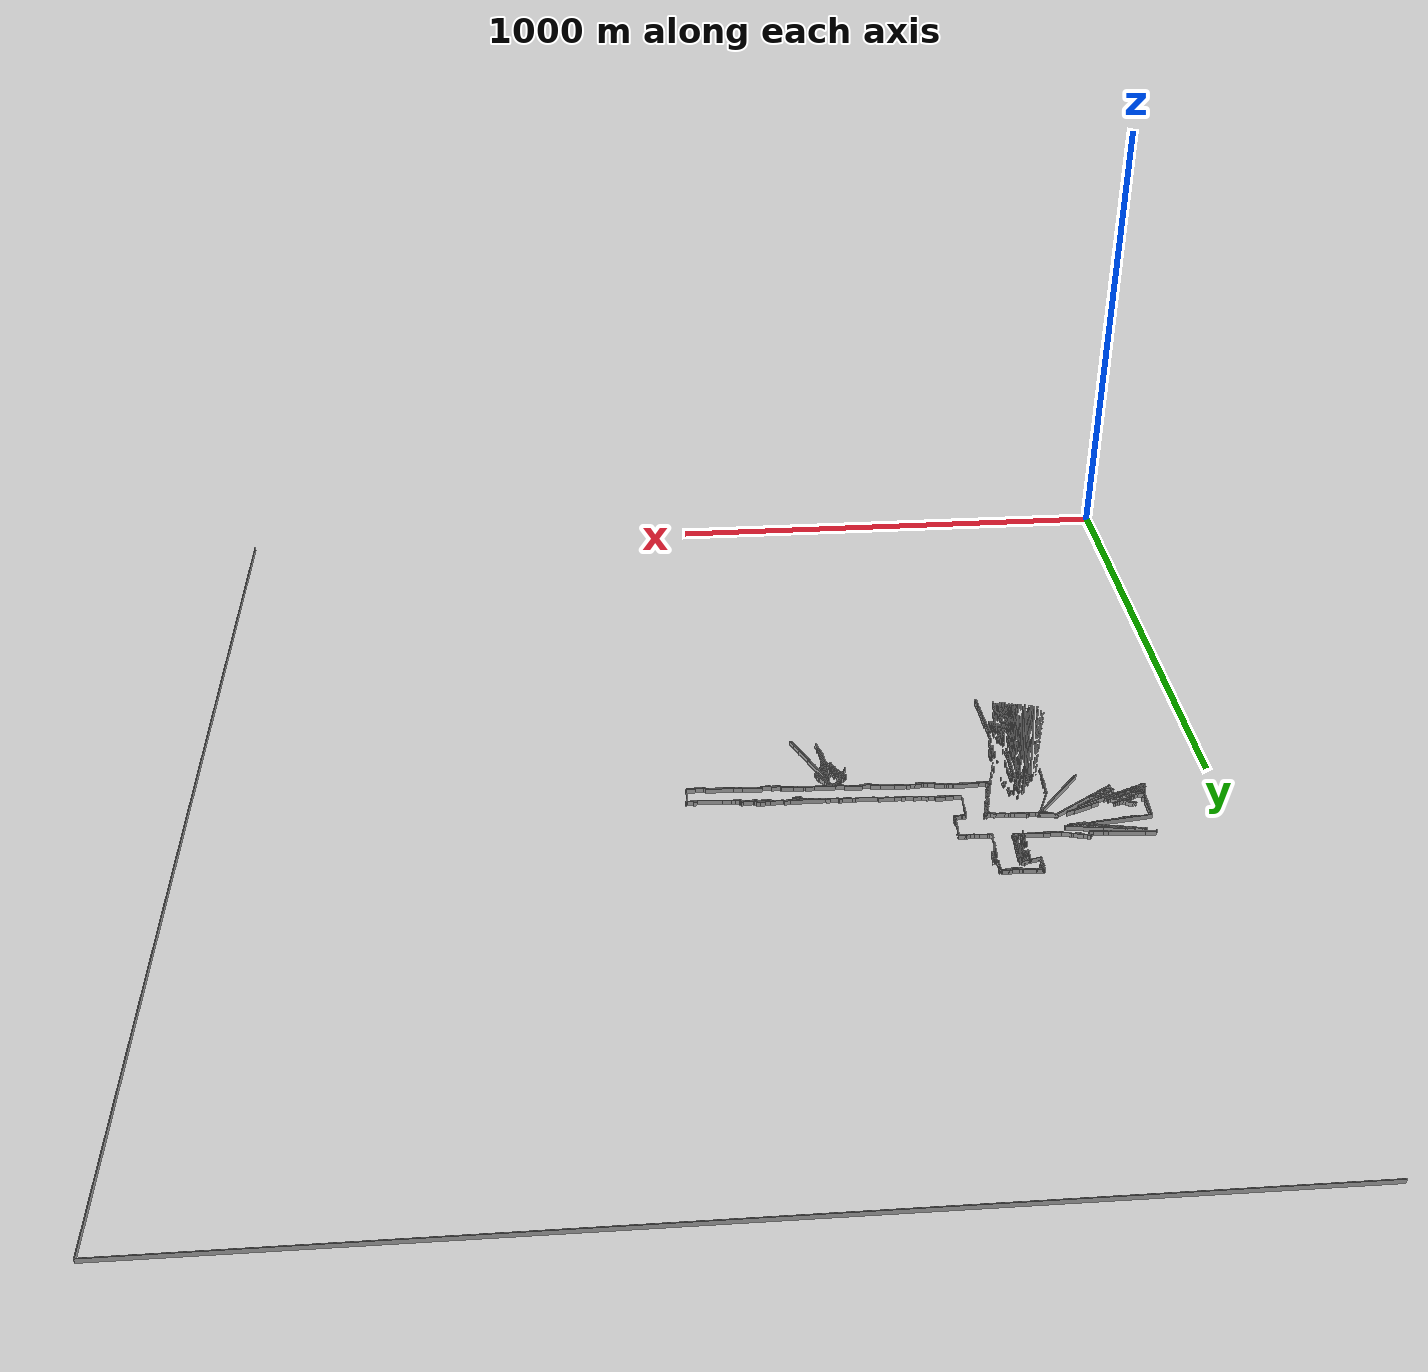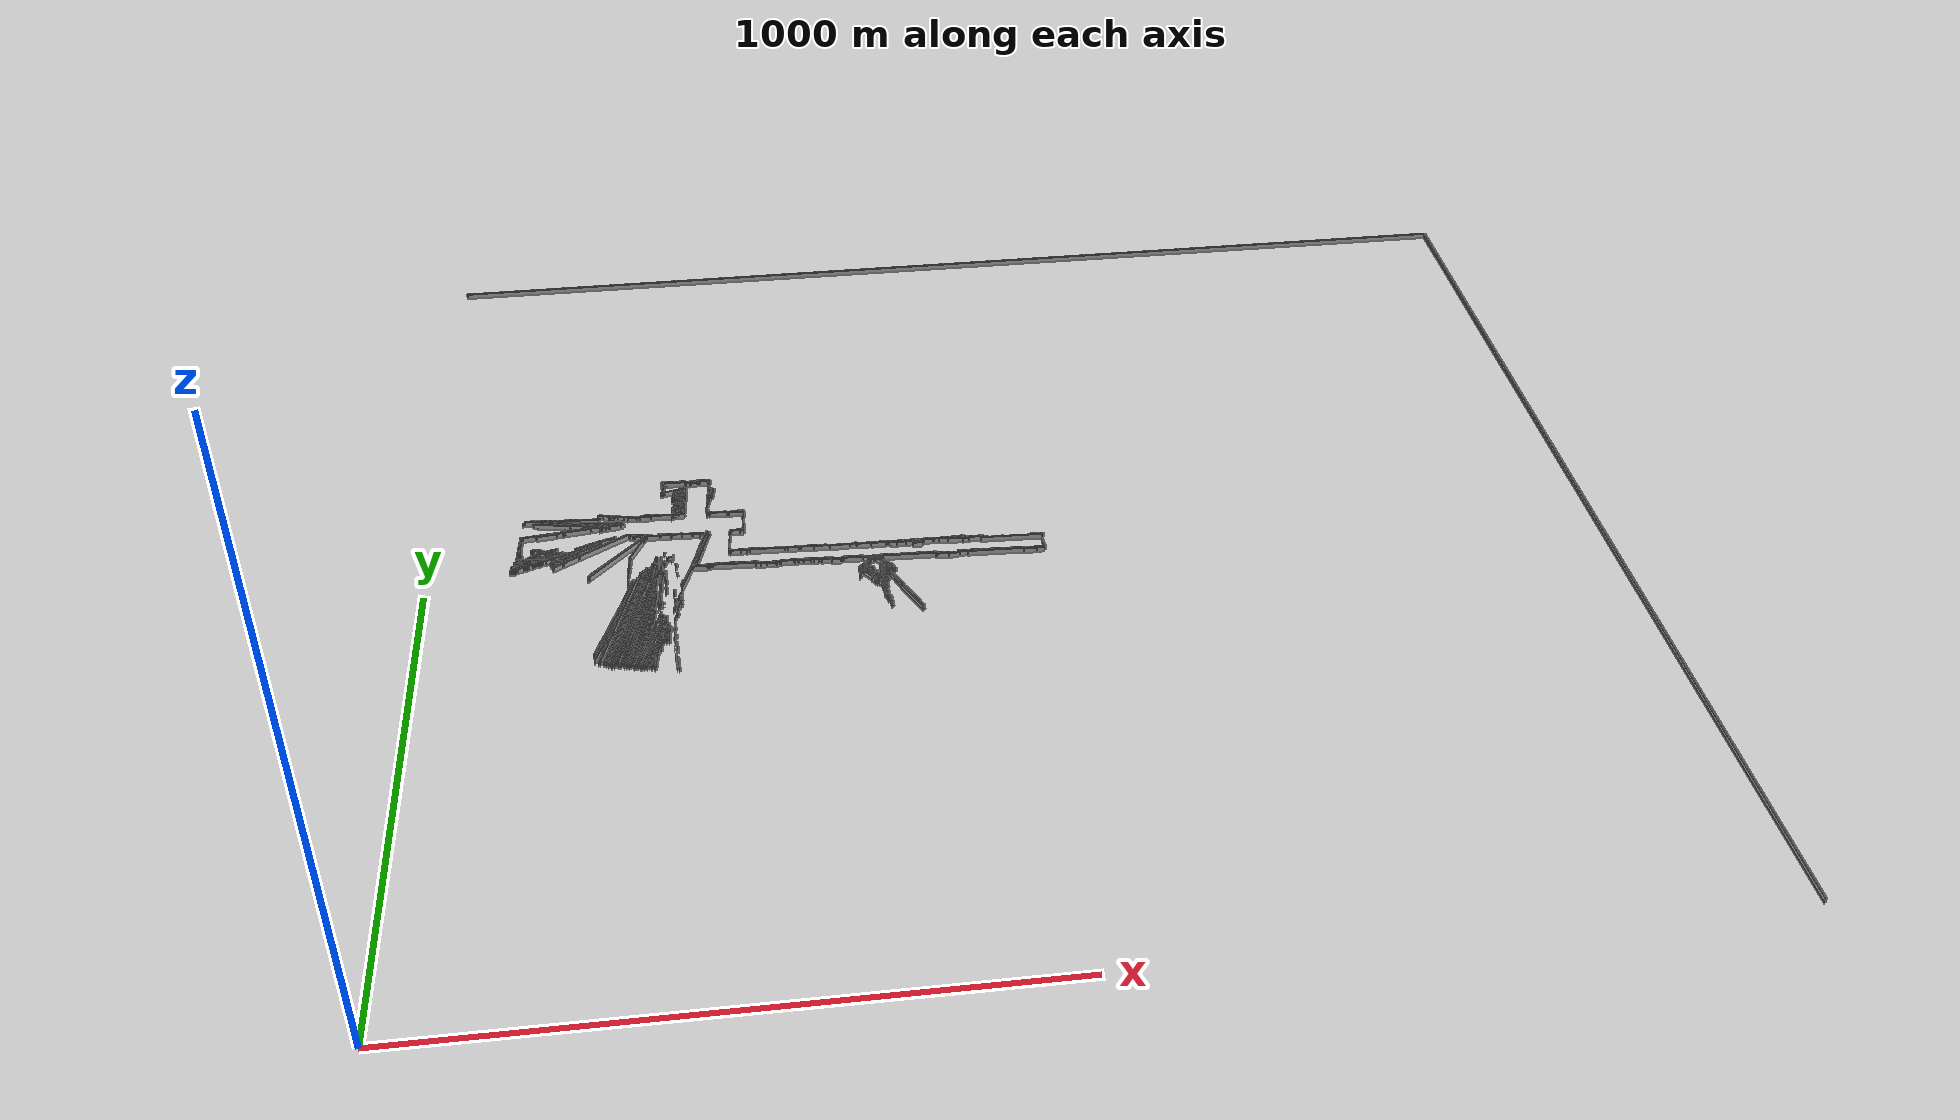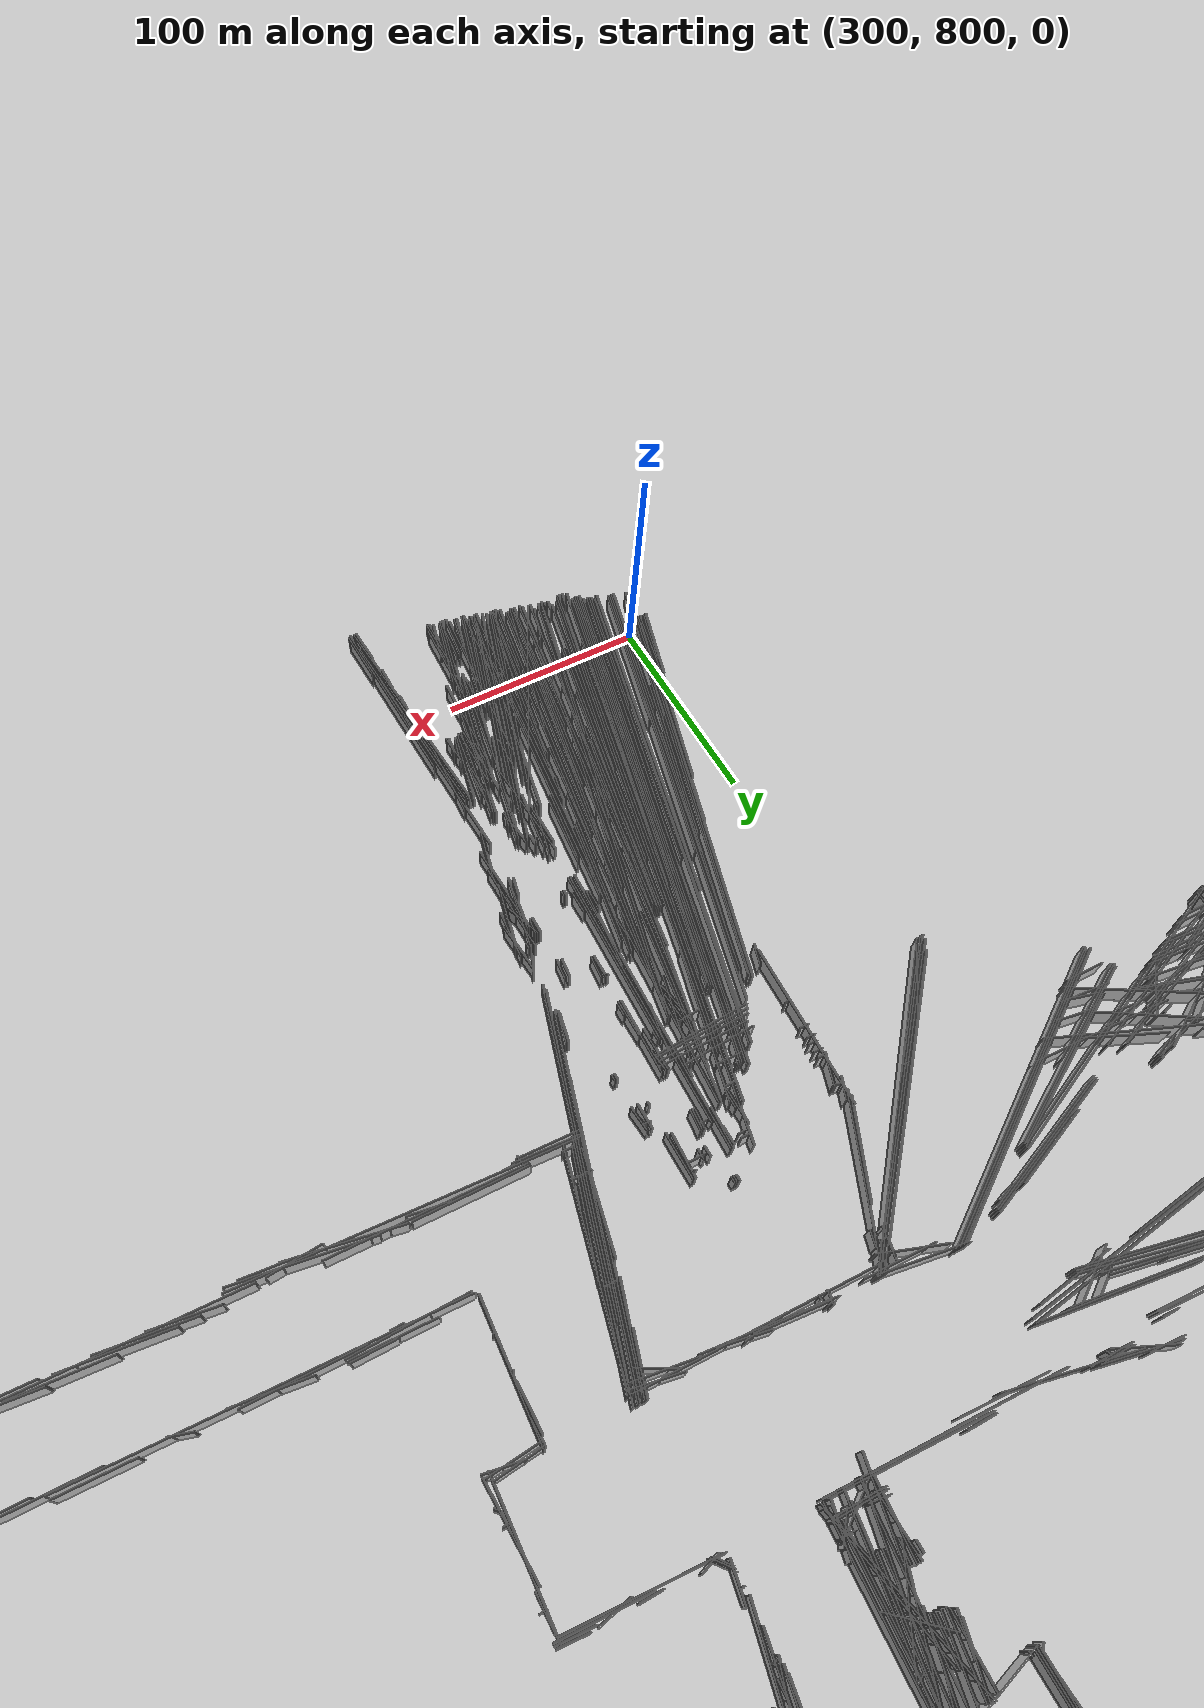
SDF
<?xml version="1.0" encoding="UTF-8" standalone="no"?>
<sdf version="1.6">
  <model name="Worldsegments">
    <static>1</static>
    <pose frame="">0 0 0 0 0 0</pose>
    <link name="Wall_0">
      <pose frame="">1023.5 2047.0 5.0 0 0 0.0</pose>
      <collision name="Wall_0_Collision">
        <geometry>
          <box>
            <size>2047.0 0.5 10.0</size>
          </box>
        </geometry>
      </collision>
      <visual name="Wall_0_Visual">
        <geometry>
          <box>
            <size>2047.0 0.5 10.0</size>
          </box>
        </geometry>
      </visual>
    </link>
    <link name="Wall_1">
      <pose frame="">2047.0 1023.0 5.0 0 0 -1.5707964</pose>
      <collision name="Wall_1_Collision">
        <geometry>
          <box>
            <size>2046.0 0.5 10.0</size>
          </box>
        </geometry>
      </collision>
      <visual name="Wall_1_Visual">
        <geometry>
          <box>
            <size>2046.0 0.5 10.0</size>
          </box>
        </geometry>
      </visual>
    </link>
    <link name="Wall_2">
      <pose frame="">2046.0 1023.0 5.0 0 0 -1.5707964</pose>
      <collision name="Wall_2_Collision">
        <geometry>
          <box>
            <size>2046.0 0.5 10.0</size>
          </box>
        </geometry>
      </collision>
      <visual name="Wall_2_Visual">
        <geometry>
          <box>
            <size>2046.0 0.5 10.0</size>
          </box>
        </geometry>
      </visual>
    </link>
    <link name="Wall_3">
      <pose frame="">1022.5 2046.0 5.0 0 0 0.0</pose>
      <collision name="Wall_3_Collision">
        <geometry>
          <box>
            <size>2045.0 0.5 10.0</size>
          </box>
        </geometry>
      </collision>
      <visual name="Wall_3_Visual">
        <geometry>
          <box>
            <size>2045.0 0.5 10.0</size>
          </box>
        </geometry>
      </visual>
    </link>
    <link name="Wall_4">
      <pose frame="">930.5 1008.5 5.0 0 0 -0.025635408</pose>
      <collision name="Wall_4_Collision">
        <geometry>
          <box>
            <size>39.012817 0.5 10.0</size>
          </box>
        </geometry>
      </collision>
      <visual name="Wall_4_Visual">
        <geometry>
          <box>
            <size>39.012817 0.5 10.0</size>
          </box>
        </geometry>
      </visual>
    </link>
    <link name="Wall_5">
      <pose frame="">641.5 1017.5 5.0 0 0 -0.029117981</pose>
      <collision name="Wall_5_Collision">
        <geometry>
          <box>
            <size>103.04368 0.5 10.0</size>
          </box>
        </geometry>
      </collision>
      <visual name="Wall_5_Visual">
        <geometry>
          <box>
            <size>103.04368 0.5 10.0</size>
          </box>
        </geometry>
      </visual>
    </link>
    <link name="Wall_6">
      <pose frame="">337.5 898.0 5.0 0 0 1.3277315</pose>
      <collision name="Wall_6_Collision">
        <geometry>
          <box>
            <size>253.4502 0.5 10.0</size>
          </box>
        </geometry>
      </collision>
      <visual name="Wall_6_Visual">
        <geometry>
          <box>
            <size>253.4502 0.5 10.0</size>
          </box>
        </geometry>
      </visual>
    </link>
    <link name="Wall_7">
      <pose frame="">601.0 1058.0 5.0 0 0 -0.035699114</pose>
      <collision name="Wall_7_Collision">
        <geometry>
          <box>
            <size>168.1071 0.5 10.0</size>
          </box>
        </geometry>
      </collision>
      <visual name="Wall_7_Visual">
        <geometry>
          <box>
            <size>168.1071 0.5 10.0</size>
          </box>
        </geometry>
      </visual>
    </link>
    <link name="Wall_8">
      <pose frame="">437.5 1221.5 5.0 0 0 1.4035424</pose>
      <collision name="Wall_8_Collision">
        <geometry>
          <box>
            <size>78.08969 0.5 10.0</size>
          </box>
        </geometry>
      </collision>
      <visual name="Wall_8_Visual">
        <geometry>
          <box>
            <size>78.08969 0.5 10.0</size>
          </box>
        </geometry>
      </visual>
    </link>
    <link name="Wall_9">
      <pose frame="">784.0 1011.0 5.0 0 0 -0.036680788</pose>
      <collision name="Wall_9_Collision">
        <geometry>
          <box>
            <size>218.14674 0.5 10.0</size>
          </box>
        </geometry>
      </collision>
      <visual name="Wall_9_Visual">
        <geometry>
          <box>
            <size>218.14674 0.5 10.0</size>
          </box>
        </geometry>
      </visual>
    </link>
    <link name="Wall_10">
      <pose frame="">819.0 1012.0 5.0 0 0 -0.05352027</pose>
      <collision name="Wall_10_Collision">
        <geometry>
          <box>
            <size>112.1606 0.5 10.0</size>
          </box>
        </geometry>
      </collision>
      <visual name="Wall_10_Visual">
        <geometry>
          <box>
            <size>112.1606 0.5 10.0</size>
          </box>
        </geometry>
      </visual>
    </link>
    <link name="Wall_11">
      <pose frame="">487.0 1237.5 5.0 0 0 1.2417467</pose>
      <collision name="Wall_11_Collision">
        <geometry>
          <box>
            <size>43.32436 0.5 10.0</size>
          </box>
        </geometry>
      </collision>
      <visual name="Wall_11_Visual">
        <geometry>
          <box>
            <size>43.32436 0.5 10.0</size>
          </box>
        </geometry>
      </visual>
    </link>
    <link name="Wall_12">
      <pose frame="">437.5 1237.5 5.0 0 0 1.3979357</pose>
      <collision name="Wall_12_Collision">
        <geometry>
          <box>
            <size>63.953106 0.5 10.0</size>
          </box>
        </geometry>
      </collision>
      <visual name="Wall_12_Visual">
        <geometry>
          <box>
            <size>63.953106 0.5 10.0</size>
          </box>
        </geometry>
      </visual>
    </link>
    <link name="Wall_13">
      <pose frame="">345.5 900.5 5.0 0 0 1.3267479</pose>
      <collision name="Wall_13_Collision">
        <geometry>
          <box>
            <size>260.72592 0.5 10.0</size>
          </box>
        </geometry>
      </collision>
      <visual name="Wall_13_Visual">
        <geometry>
          <box>
            <size>260.72592 0.5 10.0</size>
          </box>
        </geometry>
      </visual>
    </link>
    <link name="Wall_14">
      <pose frame="">357.0 913.0 5.0 0 0 1.3435007</pose>
      <collision name="Wall_14_Collision">
        <geometry>
          <box>
            <size>301.7615 0.5 10.0</size>
          </box>
        </geometry>
      </collision>
      <visual name="Wall_14_Visual">
        <geometry>
          <box>
            <size>301.7615 0.5 10.0</size>
          </box>
        </geometry>
      </visual>
    </link>
    <link name="Wall_15">
      <pose frame="">667.5 1057.5 5.0 0 0 -0.03029376</pose>
      <collision name="Wall_15_Collision">
        <geometry>
          <box>
            <size>33.01515 0.5 10.0</size>
          </box>
        </geometry>
      </collision>
      <visual name="Wall_15_Visual">
        <geometry>
          <box>
            <size>33.01515 0.5 10.0</size>
          </box>
        </geometry>
      </visual>
    </link>
    <link name="Wall_16">
      <pose frame="">1011.0 1041.0 5.0 0 0 -0.035699114</pose>
      <collision name="Wall_16_Collision">
        <geometry>
          <box>
            <size>112.0714 0.5 10.0</size>
          </box>
        </geometry>
      </collision>
      <visual name="Wall_16_Visual">
        <geometry>
          <box>
            <size>112.0714 0.5 10.0</size>
          </box>
        </geometry>
      </visual>
    </link>
    <link name="Wall_17">
      <pose frame="">382.5 805.0 5.0 0 0 1.2522407</pose>
      <collision name="Wall_17_Collision">
        <geometry>
          <box>
            <size>98.9798 0.5 10.0</size>
          </box>
        </geometry>
      </collision>
      <visual name="Wall_17_Visual">
        <geometry>
          <box>
            <size>98.9798 0.5 10.0</size>
          </box>
        </geometry>
      </visual>
    </link>
    <link name="Wall_18">
      <pose frame="">398.0 811.5 5.0 0 0 1.3319651</pose>
      <collision name="Wall_18_Collision">
        <geometry>
          <box>
            <size>118.35962 0.5 10.0</size>
          </box>
        </geometry>
      </collision>
      <visual name="Wall_18_Visual">
        <geometry>
          <box>
            <size>118.35962 0.5 10.0</size>
          </box>
        </geometry>
      </visual>
    </link>
    <link name="Wall_19">
      <pose frame="">399.0 998.5 5.0 0 0 1.4121411</pose>
      <collision name="Wall_19_Collision">
        <geometry>
          <box>
            <size>25.317978 0.5 10.0</size>
          </box>
        </geometry>
      </collision>
      <visual name="Wall_19_Visual">
        <geometry>
          <box>
            <size>25.317978 0.5 10.0</size>
          </box>
        </geometry>
      </visual>
    </link>
    <link name="Wall_20">
      <pose frame="">342.5 881.0 5.0 0 0 1.3258177</pose>
      <collision name="Wall_20_Collision">
        <geometry>
          <box>
            <size>226.77081 0.5 10.0</size>
          </box>
        </geometry>
      </collision>
      <visual name="Wall_20_Visual">
        <geometry>
          <box>
            <size>226.77081 0.5 10.0</size>
          </box>
        </geometry>
      </visual>
    </link>
    <link name="Wall_21">
      <pose frame="">353.0 801.5 5.0 0 0 1.4161958</pose>
      <collision name="Wall_21_Collision">
        <geometry>
          <box>
            <size>77.92946 0.5 10.0</size>
          </box>
        </geometry>
      </collision>
      <visual name="Wall_21_Visual">
        <geometry>
          <box>
            <size>77.92946 0.5 10.0</size>
          </box>
        </geometry>
      </visual>
    </link>
    <link name="Wall_22">
      <pose frame="">370.5 846.5 5.0 0 0 1.4118433</pose>
      <collision name="Wall_22_Collision">
        <geometry>
          <box>
            <size>132.67253 0.5 10.0</size>
          </box>
        </geometry>
      </collision>
      <visual name="Wall_22_Visual">
        <geometry>
          <box>
            <size>132.67253 0.5 10.0</size>
          </box>
        </geometry>
      </visual>
    </link>
    <link name="Wall_23">
      <pose frame="">373.0 817.5 5.0 0 0 1.4536875</pose>
      <collision name="Wall_23_Collision">
        <geometry>
          <box>
            <size>119.8207 0.5 10.0</size>
          </box>
        </geometry>
      </collision>
      <visual name="Wall_23_Visual">
        <geometry>
          <box>
            <size>119.8207 0.5 10.0</size>
          </box>
        </geometry>
      </visual>
    </link>
    <link name="Wall_24">
      <pose frame="">713.0 1054.0 5.0 0 0 -0.019997334</pose>
      <collision name="Wall_24_Collision">
        <geometry>
          <box>
            <size>100.02 0.5 10.0</size>
          </box>
        </geometry>
      </collision>
      <visual name="Wall_24_Visual">
        <geometry>
          <box>
            <size>100.02 0.5 10.0</size>
          </box>
        </geometry>
      </visual>
    </link>
    <link name="Wall_25">
      <pose frame="">372.5 879.5 5.0 0 0 1.3951365</pose>
      <collision name="Wall_25_Collision">
        <geometry>
          <box>
            <size>234.61032 0.5 10.0</size>
          </box>
        </geometry>
      </collision>
      <visual name="Wall_25_Visual">
        <geometry>
          <box>
            <size>234.61032 0.5 10.0</size>
          </box>
        </geometry>
      </visual>
    </link>
    <link name="Wall_26">
      <pose frame="">338.5 821.5 5.0 0 0 1.3370532</pose>
      <collision name="Wall_26_Collision">
        <geometry>
          <box>
            <size>107.935165 0.5 10.0</size>
          </box>
        </geometry>
      </collision>
      <visual name="Wall_26_Visual">
        <geometry>
          <box>
            <size>107.935165 0.5 10.0</size>
          </box>
        </geometry>
      </visual>
    </link>
    <link name="Wall_27">
      <pose frame="">363.5 880.5 5.0 0 0 1.3268454</pose>
      <collision name="Wall_27_Collision">
        <geometry>
          <box>
            <size>235.98729 0.5 10.0</size>
          </box>
        </geometry>
      </collision>
      <visual name="Wall_27_Visual">
        <geometry>
          <box>
            <size>235.98729 0.5 10.0</size>
          </box>
        </geometry>
      </visual>
    </link>
    <link name="Wall_28">
      <pose frame="">458.5 1041.0 5.0 0 0 1.2760662</pose>
      <collision name="Wall_28_Collision">
        <geometry>
          <box>
            <size>175.5705 0.5 10.0</size>
          </box>
        </geometry>
      </collision>
      <visual name="Wall_28_Visual">
        <geometry>
          <box>
            <size>175.5705 0.5 10.0</size>
          </box>
        </geometry>
      </visual>
    </link>
    <link name="Wall_29">
      <pose frame="">344.5 900.5 5.0 0 0 1.3267479</pose>
      <collision name="Wall_29_Collision">
        <geometry>
          <box>
            <size>260.72592 0.5 10.0</size>
          </box>
        </geometry>
      </collision>
      <visual name="Wall_29_Visual">
        <geometry>
          <box>
            <size>260.72592 0.5 10.0</size>
          </box>
        </geometry>
      </visual>
    </link>
    <link name="Wall_30">
      <pose frame="">329.0 890.5 5.0 0 0 1.3101939</pose>
      <collision name="Wall_30_Collision">
        <geometry>
          <box>
            <size>232.86263 0.5 10.0</size>
          </box>
        </geometry>
      </collision>
      <visual name="Wall_30_Visual">
        <geometry>
          <box>
            <size>232.86263 0.5 10.0</size>
          </box>
        </geometry>
      </visual>
    </link>
    <link name="Wall_31">
      <pose frame="">243.5 1156.0 5.0 0 0 0.12095365</pose>
      <collision name="Wall_31_Collision">
        <geometry>
          <box>
            <size>182.3321 0.5 10.0</size>
          </box>
        </geometry>
      </collision>
      <visual name="Wall_31_Visual">
        <geometry>
          <box>
            <size>182.3321 0.5 10.0</size>
          </box>
        </geometry>
      </visual>
    </link>
    <link name="Wall_32">
      <pose frame="">382.0 904.5 5.0 0 0 1.4029005</pose>
      <collision name="Wall_32_Collision">
        <geometry>
          <box>
            <size>59.841457 0.5 10.0</size>
          </box>
        </geometry>
      </collision>
      <visual name="Wall_32_Visual">
        <geometry>
          <box>
            <size>59.841457 0.5 10.0</size>
          </box>
        </geometry>
      </visual>
    </link>
    <link name="Wall_33">
      <pose frame="">346.0 929.0 5.0 0 0 1.3258177</pose>
      <collision name="Wall_33_Collision">
        <geometry>
          <box>
            <size>189.66286 0.5 10.0</size>
          </box>
        </geometry>
      </collision>
      <visual name="Wall_33_Visual">
        <geometry>
          <box>
            <size>189.66286 0.5 10.0</size>
          </box>
        </geometry>
      </visual>
    </link>
    <link name="Wall_34">
      <pose frame="">364.0 988.5 5.0 0 0 1.3287246</pose>
      <collision name="Wall_34_Collision">
        <geometry>
          <box>
            <size>83.43261 0.5 10.0</size>
          </box>
        </geometry>
      </collision>
      <visual name="Wall_34_Visual">
        <geometry>
          <box>
            <size>83.43261 0.5 10.0</size>
          </box>
        </geometry>
      </visual>
    </link>
    <link name="Wall_35">
      <pose frame="">219.5 1080.5 5.0 0 0 0.4000217</pose>
      <collision name="Wall_35_Collision">
        <geometry>
          <box>
            <size>161.77144 0.5 10.0</size>
          </box>
        </geometry>
      </collision>
      <visual name="Wall_35_Visual">
        <geometry>
          <box>
            <size>161.77144 0.5 10.0</size>
          </box>
        </geometry>
      </visual>
    </link>
    <link name="Wall_36">
      <pose frame="">187.5 1080.0 5.0 0 0 0.3328202</pose>
      <collision name="Wall_36_Collision">
        <geometry>
          <box>
            <size>85.70297 0.5 10.0</size>
          </box>
        </geometry>
      </collision>
      <visual name="Wall_36_Visual">
        <geometry>
          <box>
            <size>85.70297 0.5 10.0</size>
          </box>
        </geometry>
      </visual>
    </link>
    <link name="Wall_37">
      <pose frame="">404.0 1068.5 5.0 0 0 1.5707964</pose>
      <collision name="Wall_37_Collision">
        <geometry>
          <box>
            <size>3.0 0.5 10.0</size>
          </box>
        </geometry>
      </collision>
      <visual name="Wall_37_Visual">
        <geometry>
          <box>
            <size>3.0 0.5 10.0</size>
          </box>
        </geometry>
      </visual>
    </link>
    <link name="Wall_38">
      <pose frame="">322.5 896.0 5.0 0 0 1.2904967</pose>
      <collision name="Wall_38_Collision">
        <geometry>
          <box>
            <size>206.04126 0.5 10.0</size>
          </box>
        </geometry>
      </collision>
      <visual name="Wall_38_Visual">
        <geometry>
          <box>
            <size>206.04126 0.5 10.0</size>
          </box>
        </geometry>
      </visual>
    </link>
    <link name="Wall_39">
      <pose frame="">386.5 1185.0 5.0 0 0 -0.03736578</pose>
      <collision name="Wall_39_Collision">
        <geometry>
          <box>
            <size>107.07474 0.5 10.0</size>
          </box>
        </geometry>
      </collision>
      <visual name="Wall_39_Visual">
        <geometry>
          <box>
            <size>107.07474 0.5 10.0</size>
          </box>
        </geometry>
      </visual>
    </link>
    <link name="Wall_40">
      <pose frame="">369.5 930.5 5.0 0 0 1.357707</pose>
      <collision name="Wall_40_Collision">
        <geometry>
          <box>
            <size>174.95714 0.5 10.0</size>
          </box>
        </geometry>
      </collision>
      <visual name="Wall_40_Visual">
        <geometry>
          <box>
            <size>174.95714 0.5 10.0</size>
          </box>
        </geometry>
      </visual>
    </link>
    <link name="Wall_41">
      <pose frame="">422.0 799.0 5.0 0 0 -1.5007358</pose>
      <collision name="Wall_41_Collision">
        <geometry>
          <box>
            <size>114.28036 0.5 10.0</size>
          </box>
        </geometry>
      </collision>
      <visual name="Wall_41_Visual">
        <geometry>
          <box>
            <size>114.28036 0.5 10.0</size>
          </box>
        </geometry>
      </visual>
    </link>
    <link name="Wall_42">
      <pose frame="">387.5 923.5 5.0 0 0 1.3979357</pose>
      <collision name="Wall_42_Collision">
        <geometry>
          <box>
            <size>63.953106 0.5 10.0</size>
          </box>
        </geometry>
      </collision>
      <visual name="Wall_42_Visual">
        <geometry>
          <box>
            <size>63.953106 0.5 10.0</size>
          </box>
        </geometry>
      </visual>
    </link>
    <link name="Wall_43">
      <pose frame="">388.0 892.5 5.0 0 0 1.4570043</pose>
      <collision name="Wall_43_Collision">
        <geometry>
          <box>
            <size>35.22783 0.5 10.0</size>
          </box>
        </geometry>
      </collision>
      <visual name="Wall_43_Visual">
        <geometry>
          <box>
            <size>35.22783 0.5 10.0</size>
          </box>
        </geometry>
      </visual>
    </link>
    <link name="Wall_44">
      <pose frame="">490.5 1236.5 5.0 0 0 1.3439975</pose>
      <collision name="Wall_44_Collision">
        <geometry>
          <box>
            <size>13.341664 0.5 10.0</size>
          </box>
        </geometry>
      </collision>
      <visual name="Wall_44_Visual">
        <geometry>
          <box>
            <size>13.341664 0.5 10.0</size>
          </box>
        </geometry>
      </visual>
    </link>
    <link name="Wall_45">
      <pose frame="">339.0 855.0 5.0 0 0 1.3258177</pose>
      <collision name="Wall_45_Collision">
        <geometry>
          <box>
            <size>173.17044 0.5 10.0</size>
          </box>
        </geometry>
      </collision>
      <visual name="Wall_45_Visual">
        <geometry>
          <box>
            <size>173.17044 0.5 10.0</size>
          </box>
        </geometry>
      </visual>
    </link>
    <link name="Wall_46">
      <pose frame="">285.0 1113.5 5.0 0 0 0.36813077</pose>
      <collision name="Wall_46_Collision">
        <geometry>
          <box>
            <size>75.026665 0.5 10.0</size>
          </box>
        </geometry>
      </collision>
      <visual name="Wall_46_Visual">
        <geometry>
          <box>
            <size>75.026665 0.5 10.0</size>
          </box>
        </geometry>
      </visual>
    </link>
    <link name="Wall_47">
      <pose frame="">330.5 770.0 5.0 0 0 1.4056476</pose>
      <collision name="Wall_47_Collision">
        <geometry>
          <box>
            <size>6.0827627 0.5 10.0</size>
          </box>
        </geometry>
      </collision>
      <visual name="Wall_47_Visual">
        <geometry>
          <box>
            <size>6.0827627 0.5 10.0</size>
          </box>
        </geometry>
      </visual>
    </link>
    <link name="Wall_48">
      <pose frame="">408.0 875.0 5.0 0 0 1.3258177</pose>
      <collision name="Wall_48_Collision">
        <geometry>
          <box>
            <size>8.246211 0.5 10.0</size>
          </box>
        </geometry>
      </collision>
      <visual name="Wall_48_Visual">
        <geometry>
          <box>
            <size>8.246211 0.5 10.0</size>
          </box>
        </geometry>
      </visual>
    </link>
    <link name="Wall_49">
      <pose frame="">343.0 901.5 5.0 0 0 1.3248951</pose>
      <collision name="Wall_49_Collision">
        <geometry>
          <box>
            <size>262.90872 0.5 10.0</size>
          </box>
        </geometry>
      </collision>
      <visual name="Wall_49_Visual">
        <geometry>
          <box>
            <size>262.90872 0.5 10.0</size>
          </box>
        </geometry>
      </visual>
    </link>
    <link name="Wall_50">
      <pose frame="">458.0 1047.5 5.0 0 0 1.2704849</pose>
      <collision name="Wall_50_Collision">
        <geometry>
          <box>
            <size>162.26213 0.5 10.0</size>
          </box>
        </geometry>
      </collision>
      <visual name="Wall_50_Visual">
        <geometry>
          <box>
            <size>162.26213 0.5 10.0</size>
          </box>
        </geometry>
      </visual>
    </link>
    <link name="Wall_51">
      <pose frame="">353.5 892.5 5.0 0 0 1.3416893</pose>
      <collision name="Wall_51_Collision">
        <geometry>
          <box>
            <size>259.78836 0.5 10.0</size>
          </box>
        </geometry>
      </collision>
      <visual name="Wall_51_Visual">
        <geometry>
          <box>
            <size>259.78836 0.5 10.0</size>
          </box>
        </geometry>
      </visual>
    </link>
    <link name="Wall_52">
      <pose frame="">285.0 1114.5 5.0 0 0 0.36813077</pose>
      <collision name="Wall_52_Collision">
        <geometry>
          <box>
            <size>75.026665 0.5 10.0</size>
          </box>
        </geometry>
      </collision>
      <visual name="Wall_52_Visual">
        <geometry>
          <box>
            <size>75.026665 0.5 10.0</size>
          </box>
        </geometry>
      </visual>
    </link>
    <link name="Wall_53">
      <pose frame="">551.5 1062.5 5.0 0 0 -0.027020449</pose>
      <collision name="Wall_53_Collision">
        <geometry>
          <box>
            <size>37.01351 0.5 10.0</size>
          </box>
        </geometry>
      </collision>
      <visual name="Wall_53_Visual">
        <geometry>
          <box>
            <size>37.01351 0.5 10.0</size>
          </box>
        </geometry>
      </visual>
    </link>
    <link name="Wall_54">
      <pose frame="">254.0 1173.5 5.0 0 0 -0.22747499</pose>
      <collision name="Wall_54_Collision">
        <geometry>
          <box>
            <size>110.85576 0.5 10.0</size>
          </box>
        </geometry>
      </collision>
      <visual name="Wall_54_Visual">
        <geometry>
          <box>
            <size>110.85576 0.5 10.0</size>
          </box>
        </geometry>
      </visual>
    </link>
    <link name="Wall_55">
      <pose frame="">400.0 928.5 5.0 0 0 1.5707964</pose>
      <collision name="Wall_55_Collision">
        <geometry>
          <box>
            <size>11.0 0.5 10.0</size>
          </box>
        </geometry>
      </collision>
      <visual name="Wall_55_Visual">
        <geometry>
          <box>
            <size>11.0 0.5 10.0</size>
          </box>
        </geometry>
      </visual>
    </link>
    <link name="Wall_56">
      <pose frame="">779.0 932.5 5.0 0 0 -1.4825307</pose>
      <collision name="Wall_56_Collision">
        <geometry>
          <box>
            <size>113.44161 0.5 10.0</size>
          </box>
        </geometry>
      </collision>
      <visual name="Wall_56_Visual">
        <geometry>
          <box>
            <size>113.44161 0.5 10.0</size>
          </box>
        </geometry>
      </visual>
    </link>
    <link name="Wall_57">
      <pose frame="">390.0 773.5 5.0 0 0 1.3068326</pose>
      <collision name="Wall_57_Collision">
        <geometry>
          <box>
            <size>38.327538 0.5 10.0</size>
          </box>
        </geometry>
      </collision>
      <visual name="Wall_57_Visual">
        <geometry>
          <box>
            <size>38.327538 0.5 10.0</size>
          </box>
        </geometry>
      </visual>
    </link>
    <link name="Wall_58">
      <pose frame="">343.0 880.0 5.0 0 0 1.3279775</pose>
      <collision name="Wall_58_Collision">
        <geometry>
          <box>
            <size>224.58852 0.5 10.0</size>
          </box>
        </geometry>
      </collision>
      <visual name="Wall_58_Visual">
        <geometry>
          <box>
            <size>224.58852 0.5 10.0</size>
          </box>
        </geometry>
      </visual>
    </link>
    <link name="Wall_59">
      <pose frame="">386.5 890.0 5.0 0 0 1.4327903</pose>
      <collision name="Wall_59_Collision">
        <geometry>
          <box>
            <size>36.345562 0.5 10.0</size>
          </box>
        </geometry>
      </collision>
      <visual name="Wall_59_Visual">
        <geometry>
          <box>
            <size>36.345562 0.5 10.0</size>
          </box>
        </geometry>
      </visual>
    </link>
    <link name="Wall_60">
      <pose frame="">429.0 1228.5 5.0 0 0 1.458906</pose>
      <collision name="Wall_60_Collision">
        <geometry>
          <box>
            <size>89.560036 0.5 10.0</size>
          </box>
        </geometry>
      </collision>
      <visual name="Wall_60_Visual">
        <geometry>
          <box>
            <size>89.560036 0.5 10.0</size>
          </box>
        </geometry>
      </visual>
    </link>
    <link name="Wall_61">
      <pose frame="">322.0 887.0 5.0 0 0 1.2949904</pose>
      <collision name="Wall_61_Collision">
        <geometry>
          <box>
            <size>220.32703 0.5 10.0</size>
          </box>
        </geometry>
      </collision>
      <visual name="Wall_61_Visual">
        <geometry>
          <box>
            <size>220.32703 0.5 10.0</size>
          </box>
        </geometry>
      </visual>
    </link>
    <link name="Wall_62">
      <pose frame="">708.0 1053.0 5.0 0 0 0.0</pose>
      <collision name="Wall_62_Collision">
        <geometry>
          <box>
            <size>36.0 0.5 10.0</size>
          </box>
        </geometry>
      </collision>
      <visual name="Wall_62_Visual">
        <geometry>
          <box>
            <size>36.0 0.5 10.0</size>
          </box>
        </geometry>
      </visual>
    </link>
    <link name="Wall_63">
      <pose frame="">244.0 1172.5 5.0 0 0 -0.20788993</pose>
      <collision name="Wall_63_Collision">
        <geometry>
          <box>
            <size>130.81667 0.5 10.0</size>
          </box>
        </geometry>
      </collision>
      <visual name="Wall_63_Visual">
        <geometry>
          <box>
            <size>130.81667 0.5 10.0</size>
          </box>
        </geometry>
      </visual>
    </link>
    <link name="Wall_64">
      <pose frame="">458.5 1039.0 5.0 0 0 0.0</pose>
      <collision name="Wall_64_Collision">
        <geometry>
          <box>
            <size>9.0 0.5 10.0</size>
          </box>
        </geometry>
      </collision>
      <visual name="Wall_64_Visual">
        <geometry>
          <box>
            <size>9.0 0.5 10.0</size>
          </box>
        </geometry>
      </visual>
    </link>
    <link name="Wall_65">
      <pose frame="">469.0 1072.0 5.0 0 0 1.2737321</pose>
      <collision name="Wall_65_Collision">
        <geometry>
          <box>
            <size>102.48902 0.5 10.0</size>
          </box>
        </geometry>
      </collision>
      <visual name="Wall_65_Visual">
        <geometry>
          <box>
            <size>102.48902 0.5 10.0</size>
          </box>
        </geometry>
      </visual>
    </link>
    <link name="Wall_66">
      <pose frame="">327.5 861.5 5.0 0 0 1.3271782</pose>
      <collision name="Wall_66_Collision">
        <geometry>
          <box>
            <size>178.26385 0.5 10.0</size>
          </box>
        </geometry>
      </collision>
      <visual name="Wall_66_Visual">
        <geometry>
          <box>
            <size>178.26385 0.5 10.0</size>
          </box>
        </geometry>
      </visual>
    </link>
    <link name="Wall_67">
      <pose frame="">384.0 798.5 5.0 0 0 1.476955</pose>
      <collision name="Wall_67_Collision">
        <geometry>
          <box>
            <size>85.37564 0.5 10.0</size>
          </box>
        </geometry>
      </collision>
      <visual name="Wall_67_Visual">
        <geometry>
          <box>
            <size>85.37564 0.5 10.0</size>
          </box>
        </geometry>
      </visual>
    </link>
    <link name="Wall_68">
      <pose frame="">418.0 1211.5 5.0 0 0 1.5707964</pose>
      <collision name="Wall_68_Collision">
        <geometry>
          <box>
            <size>5.0 0.5 10.0</size>
          </box>
        </geometry>
      </collision>
      <visual name="Wall_68_Visual">
        <geometry>
          <box>
            <size>5.0 0.5 10.0</size>
          </box>
        </geometry>
      </visual>
    </link>
    <link name="Wall_69">
      <pose frame="">434.5 1237.0 5.0 0 0 1.426642</pose>
      <collision name="Wall_69_Collision">
        <geometry>
          <box>
            <size>62.649822 0.5 10.0</size>
          </box>
        </geometry>
      </collision>
      <visual name="Wall_69_Visual">
        <geometry>
          <box>
            <size>62.649822 0.5 10.0</size>
          </box>
        </geometry>
      </visual>
    </link>
    <link name="Wall_70">
      <pose frame="">357.0 886.0 5.0 0 0 1.3765553</pose>
      <collision name="Wall_70_Collision">
        <geometry>
          <box>
            <size>124.33825 0.5 10.0</size>
          </box>
        </geometry>
      </collision>
      <visual name="Wall_70_Visual">
        <geometry>
          <box>
            <size>124.33825 0.5 10.0</size>
          </box>
        </geometry>
      </visual>
    </link>
    <link name="Wall_71">
      <pose frame="">526.5 1021.0 5.0 0 0 -0.052240007</pose>
      <collision name="Wall_71_Collision">
        <geometry>
          <box>
            <size>153.20901 0.5 10.0</size>
          </box>
        </geometry>
      </collision>
      <visual name="Wall_71_Visual">
        <geometry>
          <box>
            <size>153.20901 0.5 10.0</size>
          </box>
        </geometry>
      </visual>
    </link>
    <link name="Wall_72">
      <pose frame="">406.5 1040.0 5.0 0 0 1.4711276</pose>
      <collision name="Wall_72_Collision">
        <geometry>
          <box>
            <size>10.049875 0.5 10.0</size>
          </box>
        </geometry>
      </collision>
      <visual name="Wall_72_Visual">
        <geometry>
          <box>
            <size>10.049875 0.5 10.0</size>
          </box>
        </geometry>
      </visual>
    </link>
    <link name="Wall_73">
      <pose frame="">400.0 822.0 5.0 0 0 1.5182133</pose>
      <collision name="Wall_73_Collision">
        <geometry>
          <box>
            <size>38.052597 0.5 10.0</size>
          </box>
        </geometry>
      </collision>
      <visual name="Wall_73_Visual">
        <geometry>
          <box>
            <size>38.052597 0.5 10.0</size>
          </box>
        </geometry>
      </visual>
    </link>
    <link name="Wall_74">
      <pose frame="">426.5 787.5 5.0 0 0 -1.5378412</pose>
      <collision name="Wall_74_Collision">
        <geometry>
          <box>
            <size>91.04944 0.5 10.0</size>
          </box>
        </geometry>
      </collision>
      <visual name="Wall_74_Visual">
        <geometry>
          <box>
            <size>91.04944 0.5 10.0</size>
          </box>
        </geometry>
      </visual>
    </link>
    <link name="Wall_75">
      <pose frame="">439.5 1194.5 5.0 0 0 1.3370532</pose>
      <collision name="Wall_75_Collision">
        <geometry>
          <box>
            <size>21.587032 0.5 10.0</size>
          </box>
        </geometry>
      </collision>
      <visual name="Wall_75_Visual">
        <geometry>
          <box>
            <size>21.587032 0.5 10.0</size>
          </box>
        </geometry>
      </visual>
    </link>
    <link name="Wall_76">
      <pose frame="">379.0 817.0 5.0 0 0 1.3667784</pose>
      <collision name="Wall_76_Collision">
        <geometry>
          <box>
            <size>118.45674 0.5 10.0</size>
          </box>
        </geometry>
      </collision>
      <visual name="Wall_76_Visual">
        <geometry>
          <box>
            <size>118.45674 0.5 10.0</size>
          </box>
        </geometry>
      </visual>
    </link>
    <link name="Wall_77">
      <pose frame="">793.0 1051.0 5.0 0 0 -0.21109334</pose>
      <collision name="Wall_77_Collision">
        <geometry>
          <box>
            <size>28.635643 0.5 10.0</size>
          </box>
        </geometry>
      </collision>
      <visual name="Wall_77_Visual">
        <geometry>
          <box>
            <size>28.635643 0.5 10.0</size>
          </box>
        </geometry>
      </visual>
    </link>
    <link name="Wall_78">
      <pose frame="">365.5 1125.5 5.0 0 0 -0.03029376</pose>
      <collision name="Wall_78_Collision">
        <geometry>
          <box>
            <size>33.01515 0.5 10.0</size>
          </box>
        </geometry>
      </collision>
      <visual name="Wall_78_Visual">
        <geometry>
          <box>
            <size>33.01515 0.5 10.0</size>
          </box>
        </geometry>
      </visual>
    </link>
    <link name="Wall_79">
      <pose frame="">972.0 1005.0 5.0 0 0 -0.05258306</pose>
      <collision name="Wall_79_Collision">
        <geometry>
          <box>
            <size>114.15778 0.5 10.0</size>
          </box>
        </geometry>
      </collision>
      <visual name="Wall_79_Visual">
        <geometry>
          <box>
            <size>114.15778 0.5 10.0</size>
          </box>
        </geometry>
      </visual>
    </link>
    <link name="Wall_80">
      <pose frame="">385.5 991.5 5.0 0 0 1.4108832</pose>
      <collision name="Wall_80_Collision">
        <geometry>
          <box>
            <size>94.20191 0.5 10.0</size>
          </box>
        </geometry>
      </collision>
      <visual name="Wall_80_Visual">
        <geometry>
          <box>
            <size>94.20191 0.5 10.0</size>
          </box>
        </geometry>
      </visual>
    </link>
    <link name="Wall_81">
      <pose frame="">352.5 872.5 5.0 0 0 1.365669</pose>
      <collision name="Wall_81_Collision">
        <geometry>
          <box>
            <size>152.19067 0.5 10.0</size>
          </box>
        </geometry>
      </collision>
      <visual name="Wall_81_Visual">
        <geometry>
          <box>
            <size>152.19067 0.5 10.0</size>
          </box>
        </geometry>
      </visual>
    </link>
    <link name="Wall_82">
      <pose frame="">804.0 931.5 5.0 0 0 -1.1036766</pose>
      <collision name="Wall_82_Collision">
        <geometry>
          <box>
            <size>128.7983 0.5 10.0</size>
          </box>
        </geometry>
      </collision>
      <visual name="Wall_82_Visual">
        <geometry>
          <box>
            <size>128.7983 0.5 10.0</size>
          </box>
        </geometry>
      </visual>
    </link>
    <link name="Wall_83">
      <pose frame="">404.5 1040.5 5.0 0 0 1.4601392</pose>
      <collision name="Wall_83_Collision">
        <geometry>
          <box>
            <size>9.055386 0.5 10.0</size>
          </box>
        </geometry>
      </collision>
      <visual name="Wall_83_Visual">
        <geometry>
          <box>
            <size>9.055386 0.5 10.0</size>
          </box>
        </geometry>
      </visual>
    </link>
    <link name="Wall_84">
      <pose frame="">915.5 1046.5 5.0 0 0 -0.027020449</pose>
      <collision name="Wall_84_Collision">
        <geometry>
          <box>
            <size>37.01351 0.5 10.0</size>
          </box>
        </geometry>
      </collision>
      <visual name="Wall_84_Visual">
        <geometry>
          <box>
            <size>37.01351 0.5 10.0</size>
          </box>
        </geometry>
      </visual>
    </link>
    <link name="Wall_85">
      <pose frame="">278.5 1091.0 5.0 0 0 0.57332474</pose>
      <collision name="Wall_85_Collision">
        <geometry>
          <box>
            <size>151.17209 0.5 10.0</size>
          </box>
        </geometry>
      </collision>
      <visual name="Wall_85_Visual">
        <geometry>
          <box>
            <size>151.17209 0.5 10.0</size>
          </box>
        </geometry>
      </visual>
    </link>
    <link name="Wall_86">
      <pose frame="">253.0 1188.0 5.0 0 0 -0.0540015</pose>
      <collision name="Wall_86_Collision">
        <geometry>
          <box>
            <size>74.10803 0.5 10.0</size>
          </box>
        </geometry>
      </collision>
      <visual name="Wall_86_Visual">
        <geometry>
          <box>
            <size>74.10803 0.5 10.0</size>
          </box>
        </geometry>
      </visual>
    </link>
    <link name="Wall_87">
      <pose frame="">509.0 1182.0 5.0 0 0 0.0</pose>
      <collision name="Wall_87_Collision">
        <geometry>
          <box>
            <size>10.0 0.5 10.0</size>
          </box>
        </geometry>
      </collision>
      <visual name="Wall_87_Visual">
        <geometry>
          <box>
            <size>10.0 0.5 10.0</size>
          </box>
        </geometry>
      </visual>
    </link>
    <link name="Wall_88">
      <pose frame="">370.0 817.5 5.0 0 0 1.3996477</pose>
      <collision name="Wall_88_Collision">
        <geometry>
          <box>
            <size>82.20097 0.5 10.0</size>
          </box>
        </geometry>
      </collision>
      <visual name="Wall_88_Visual">
        <geometry>
          <box>
            <size>82.20097 0.5 10.0</size>
          </box>
        </geometry>
      </visual>
    </link>
    <link name="Wall_89">
      <pose frame="">234.0 1084.5 5.0 0 0 -0.044089057</pose>
      <collision name="Wall_89_Collision">
        <geometry>
          <box>
            <size>68.06615 0.5 10.0</size>
          </box>
        </geometry>
      </collision>
      <visual name="Wall_89_Visual">
        <geometry>
          <box>
            <size>68.06615 0.5 10.0</size>
          </box>
        </geometry>
      </visual>
    </link>
    <link name="Wall_90">
      <pose frame="">369.0 905.0 5.0 0 0 1.3946742</pose>
      <collision name="Wall_90_Collision">
        <geometry>
          <box>
            <size>239.70816 0.5 10.0</size>
          </box>
        </geometry>
      </collision>
      <visual name="Wall_90_Visual">
        <geometry>
          <box>
            <size>239.70816 0.5 10.0</size>
          </box>
        </geometry>
      </visual>
    </link>
    <link name="Wall_91">
      <pose frame="">298.5 820.0 5.0 0 0 1.3360738</pose>
      <collision name="Wall_91_Collision">
        <geometry>
          <box>
            <size>47.296936 0.5 10.0</size>
          </box>
        </geometry>
      </collision>
      <visual name="Wall_91_Visual">
        <geometry>
          <box>
            <size>47.296936 0.5 10.0</size>
          </box>
        </geometry>
      </visual>
    </link>
    <link name="Wall_92">
      <pose frame="">360.0 1184.0 5.0 0 0 -0.049958397</pose>
      <collision name="Wall_92_Collision">
        <geometry>
          <box>
            <size>40.04997 0.5 10.0</size>
          </box>
        </geometry>
      </collision>
      <visual name="Wall_92_Visual">
        <geometry>
          <box>
            <size>40.04997 0.5 10.0</size>
          </box>
        </geometry>
      </visual>
    </link>
    <link name="Wall_93">
      <pose frame="">423.5 1123.0 5.0 0 0 -0.1013465</pose>
      <collision name="Wall_93_Collision">
        <geometry>
          <box>
            <size>59.3043 0.5 10.0</size>
          </box>
        </geometry>
      </collision>
      <visual name="Wall_93_Visual">
        <geometry>
          <box>
            <size>59.3043 0.5 10.0</size>
          </box>
        </geometry>
      </visual>
    </link>
    <link name="Wall_94">
      <pose frame="">380.0 784.5 5.0 0 0 1.297137</pose>
      <collision name="Wall_94_Collision">
        <geometry>
          <box>
            <size>59.20304 0.5 10.0</size>
          </box>
        </geometry>
      </collision>
      <visual name="Wall_94_Visual">
        <geometry>
          <box>
            <size>59.20304 0.5 10.0</size>
          </box>
        </geometry>
      </visual>
    </link>
    <link name="Wall_95">
      <pose frame="">350.5 897.0 5.0 0 0 1.3393854</pose>
      <collision name="Wall_95_Collision">
        <geometry>
          <box>
            <size>178.76521 0.5 10.0</size>
          </box>
        </geometry>
      </collision>
      <visual name="Wall_95_Visual">
        <geometry>
          <box>
            <size>178.76521 0.5 10.0</size>
          </box>
        </geometry>
      </visual>
    </link>
    <link name="Wall_96">
      <pose frame="">1036.5 999.5 5.0 0 0 -0.043450896</pose>
      <collision name="Wall_96_Collision">
        <geometry>
          <box>
            <size>23.021729 0.5 10.0</size>
          </box>
        </geometry>
      </collision>
      <visual name="Wall_96_Visual">
        <geometry>
          <box>
            <size>23.021729 0.5 10.0</size>
          </box>
        </geometry>
      </visual>
    </link>
    <link name="Wall_97">
      <pose frame="">327.0 1069.5 5.0 0 0 0.8550527</pose>
      <collision name="Wall_97_Collision">
        <geometry>
          <box>
            <size>152.3975 0.5 10.0</size>
          </box>
        </geometry>
      </collision>
      <visual name="Wall_97_Visual">
        <geometry>
          <box>
            <size>152.3975 0.5 10.0</size>
          </box>
        </geometry>
      </visual>
    </link>
    <link name="Wall_98">
      <pose frame="">420.5 1200.5 5.0 0 0 1.4743226</pose>
      <collision name="Wall_98_Collision">
        <geometry>
          <box>
            <size>31.144823 0.5 10.0</size>
          </box>
        </geometry>
      </collision>
      <visual name="Wall_98_Visual">
        <geometry>
          <box>
            <size>31.144823 0.5 10.0</size>
          </box>
        </geometry>
      </visual>
    </link>
    <link name="Wall_99">
      <pose frame="">325.0 1070.5 5.0 0 0 0.8365164</pose>
      <collision name="Wall_99_Collision">
        <geometry>
          <box>
            <size>152.2268 0.5 10.0</size>
          </box>
        </geometry>
      </collision>
      <visual name="Wall_99_Visual">
        <geometry>
          <box>
            <size>152.2268 0.5 10.0</size>
          </box>
        </geometry>
      </visual>
    </link>
    <link name="Wall_100">
      <pose frame="">395.0 884.0 5.0 0 0 1.5707964</pose>
      <collision name="Wall_100_Collision">
        <geometry>
          <box>
            <size>22.0 0.5 10.0</size>
          </box>
        </geometry>
      </collision>
      <visual name="Wall_100_Visual">
        <geometry>
          <box>
            <size>22.0 0.5 10.0</size>
          </box>
        </geometry>
      </visual>
    </link>
    <link name="Wall_101">
      <pose frame="">401.0 1273.0 5.0 0 0 -1.5707964</pose>
      <collision name="Wall_101_Collision">
        <geometry>
          <box>
            <size>36.0 0.5 10.0</size>
          </box>
        </geometry>
      </collision>
      <visual name="Wall_101_Visual">
        <geometry>
          <box>
            <size>36.0 0.5 10.0</size>
          </box>
        </geometry>
      </visual>
    </link>
    <link name="Wall_102">
      <pose frame="">817.5 901.5 5.0 0 0 -1.102454</pose>
      <collision name="Wall_102_Collision">
        <geometry>
          <box>
            <size>95.257545 0.5 10.0</size>
          </box>
        </geometry>
      </collision>
      <visual name="Wall_102_Visual">
        <geometry>
          <box>
            <size>95.257545 0.5 10.0</size>
          </box>
        </geometry>
      </visual>
    </link>
    <link name="Wall_103">
      <pose frame="">364.0 797.0 5.0 0 0 1.3838171</pose>
      <collision name="Wall_103_Collision">
        <geometry>
          <box>
            <size>75.31268 0.5 10.0</size>
          </box>
        </geometry>
      </collision>
      <visual name="Wall_103_Visual">
        <geometry>
          <box>
            <size>75.31268 0.5 10.0</size>
          </box>
        </geometry>
      </visual>
    </link>
    <link name="Wall_104">
      <pose frame="">424.5 887.0 5.0 0 0 1.3258177</pose>
      <collision name="Wall_104_Collision">
        <geometry>
          <box>
            <size>28.86174 0.5 10.0</size>
          </box>
        </geometry>
      </collision>
      <visual name="Wall_104_Visual">
        <geometry>
          <box>
            <size>28.86174 0.5 10.0</size>
          </box>
        </geometry>
      </visual>
    </link>
    <link name="Wall_105">
      <pose frame="">432.5 1245.5 5.0 0 0 1.332187</pose>
      <collision name="Wall_105_Collision">
        <geometry>
          <box>
            <size>38.078865 0.5 10.0</size>
          </box>
        </geometry>
      </collision>
      <visual name="Wall_105_Visual">
        <geometry>
          <box>
            <size>38.078865 0.5 10.0</size>
          </box>
        </geometry>
      </visual>
    </link>
    <link name="Wall_106">
      <pose frame="">410.0 839.5 5.0 0 0 1.4100336</pose>
      <collision name="Wall_106_Collision">
        <geometry>
          <box>
            <size>37.48333 0.5 10.0</size>
          </box>
        </geometry>
      </collision>
      <visual name="Wall_106_Visual">
        <geometry>
          <box>
            <size>37.48333 0.5 10.0</size>
          </box>
        </geometry>
      </visual>
    </link>
    <link name="Wall_107">
      <pose frame="">817.5 1051.0 5.0 0 0 0.0</pose>
      <collision name="Wall_107_Collision">
        <geometry>
          <box>
            <size>109.0 0.5 10.0</size>
          </box>
        </geometry>
      </collision>
      <visual name="Wall_107_Visual">
        <geometry>
          <box>
            <size>109.0 0.5 10.0</size>
          </box>
        </geometry>
      </visual>
    </link>
    <link name="Wall_108">
      <pose frame="">397.5 986.0 5.0 0 0 1.5355996</pose>
      <collision name="Wall_108_Collision">
        <geometry>
          <box>
            <size>142.088 0.5 10.0</size>
          </box>
        </geometry>
      </collision>
      <visual name="Wall_108_Visual">
        <geometry>
          <box>
            <size>142.088 0.5 10.0</size>
          </box>
        </geometry>
      </visual>
    </link>
    <link name="Wall_109">
      <pose frame="">804.0 1052.0 5.0 0 0 0.0</pose>
      <collision name="Wall_109_Collision">
        <geometry>
          <box>
            <size>134.0 0.5 10.0</size>
          </box>
        </geometry>
      </collision>
      <visual name="Wall_109_Visual">
        <geometry>
          <box>
            <size>134.0 0.5 10.0</size>
          </box>
        </geometry>
      </visual>
    </link>
    <link name="Wall_110">
      <pose frame="">402.5 1185.5 5.0 0 0 -0.0422284</pose>
      <collision name="Wall_110_Collision">
        <geometry>
          <box>
            <size>71.063354 0.5 10.0</size>
          </box>
        </geometry>
      </collision>
      <visual name="Wall_110_Visual">
        <geometry>
          <box>
            <size>71.063354 0.5 10.0</size>
          </box>
        </geometry>
      </visual>
    </link>
    <link name="Wall_111">
      <pose frame="">728.0 1016.5 5.0 0 0 -0.027770637</pose>
      <collision name="Wall_111_Collision">
        <geometry>
          <box>
            <size>36.013885 0.5 10.0</size>
          </box>
        </geometry>
      </collision>
      <visual name="Wall_111_Visual">
        <geometry>
          <box>
            <size>36.013885 0.5 10.0</size>
          </box>
        </geometry>
      </visual>
    </link>
    <link name="Wall_112">
      <pose frame="">243.5 1157.5 5.0 0 0 0.12639442</pose>
      <collision name="Wall_112_Collision">
        <geometry>
          <box>
            <size>182.45547 0.5 10.0</size>
          </box>
        </geometry>
      </collision>
      <visual name="Wall_112_Visual">
        <geometry>
          <box>
            <size>182.45547 0.5 10.0</size>
          </box>
        </geometry>
      </visual>
    </link>
    <link name="Wall_113">
      <pose frame="">426.0 1008.5 5.0 0 0 -1.5707964</pose>
      <collision name="Wall_113_Collision">
        <geometry>
          <box>
            <size>3.0 0.5 10.0</size>
          </box>
        </geometry>
      </collision>
      <visual name="Wall_113_Visual">
        <geometry>
          <box>
            <size>3.0 0.5 10.0</size>
          </box>
        </geometry>
      </visual>
    </link>
    <link name="Wall_114">
      <pose frame="">320.0 853.5 5.0 0 0 1.3118434</pose>
      <collision name="Wall_114_Collision">
        <geometry>
          <box>
            <size>156.20819 0.5 10.0</size>
          </box>
        </geometry>
      </collision>
      <visual name="Wall_114_Visual">
        <geometry>
          <box>
            <size>156.20819 0.5 10.0</size>
          </box>
        </geometry>
      </visual>
    </link>
    <link name="Wall_115">
      <pose frame="">146.5 1050.5 5.0 0 0 -0.09065989</pose>
      <collision name="Wall_115_Collision">
        <geometry>
          <box>
            <size>11.045361 0.5 10.0</size>
          </box>
        </geometry>
      </collision>
      <visual name="Wall_115_Visual">
        <geometry>
          <box>
            <size>11.045361 0.5 10.0</size>
          </box>
        </geometry>
      </visual>
    </link>
    <link name="Wall_116">
      <pose frame="">380.0 1023.0 5.0 0 0 0.0</pose>
      <collision name="Wall_116_Collision">
        <geometry>
          <box>
            <size>12.0 0.5 10.0</size>
          </box>
        </geometry>
      </collision>
      <visual name="Wall_116_Visual">
        <geometry>
          <box>
            <size>12.0 0.5 10.0</size>
          </box>
        </geometry>
      </visual>
    </link>
    <link name="Wall_117">
      <pose frame="">384.5 815.5 5.0 0 0 1.2662854</pose>
      <collision name="Wall_117_Collision">
        <geometry>
          <box>
            <size>110.06362 0.5 10.0</size>
          </box>
        </geometry>
      </collision>
      <visual name="Wall_117_Visual">
        <geometry>
          <box>
            <size>110.06362 0.5 10.0</size>
          </box>
        </geometry>
      </visual>
    </link>
    <link name="Wall_118">
      <pose frame="">464.5 1052.5 5.0 0 0 1.2604089</pose>
      <collision name="Wall_118_Collision">
        <geometry>
          <box>
            <size>55.65968 0.5 10.0</size>
          </box>
        </geometry>
      </collision>
      <visual name="Wall_118_Visual">
        <geometry>
          <box>
            <size>55.65968 0.5 10.0</size>
          </box>
        </geometry>
      </visual>
    </link>
    <link name="Wall_119">
      <pose frame="">903.5 1003.0 5.0 0 0 0.0</pose>
      <collision name="Wall_119_Collision">
        <geometry>
          <box>
            <size>19.0 0.5 10.0</size>
          </box>
        </geometry>
      </collision>
      <visual name="Wall_119_Visual">
        <geometry>
          <box>
            <size>19.0 0.5 10.0</size>
          </box>
        </geometry>
      </visual>
    </link>
    <link name="Wall_120">
      <pose frame="">318.0 867.0 5.0 0 0 1.2877005</pose>
      <collision name="Wall_120_Collision">
        <geometry>
          <box>
            <size>114.56003 0.5 10.0</size>
          </box>
        </geometry>
      </collision>
      <visual name="Wall_120_Visual">
        <geometry>
          <box>
            <size>114.56003 0.5 10.0</size>
          </box>
        </geometry>
      </visual>
    </link>
    <link name="Wall_121">
      <pose frame="">427.5 917.0 5.0 0 0 -1.5480729</pose>
      <collision name="Wall_121_Collision">
        <geometry>
          <box>
            <size>44.011364 0.5 10.0</size>
          </box>
        </geometry>
      </collision>
      <visual name="Wall_121_Visual">
        <geometry>
          <box>
            <size>44.011364 0.5 10.0</size>
          </box>
        </geometry>
      </visual>
    </link>
    <link name="Wall_122">
      <pose frame="">402.0 835.5 5.0 0 0 1.5707964</pose>
      <collision name="Wall_122_Collision">
        <geometry>
          <box>
            <size>11.0 0.5 10.0</size>
          </box>
        </geometry>
      </collision>
      <visual name="Wall_122_Visual">
        <geometry>
          <box>
            <size>11.0 0.5 10.0</size>
          </box>
        </geometry>
      </visual>
    </link>
    <link name="Wall_123">
      <pose frame="">453.5 1028.0 5.0 0 0 1.2779909</pose>
      <collision name="Wall_123_Collision">
        <geometry>
          <box>
            <size>142.04576 0.5 10.0</size>
          </box>
        </geometry>
      </collision>
      <visual name="Wall_123_Visual">
        <geometry>
          <box>
            <size>142.04576 0.5 10.0</size>
          </box>
        </geometry>
      </visual>
    </link>
    <link name="Wall_124">
      <pose frame="">544.5 1169.0 5.0 0 0 0.0</pose>
      <collision name="Wall_124_Collision">
        <geometry>
          <box>
            <size>3.0 0.5 10.0</size>
          </box>
        </geometry>
      </collision>
      <visual name="Wall_124_Visual">
        <geometry>
          <box>
            <size>3.0 0.5 10.0</size>
          </box>
        </geometry>
      </visual>
    </link>
    <link name="Wall_125">
      <pose frame="">780.0 971.5 5.0 0 0 -1.5226408</pose>
      <collision name="Wall_125_Collision">
        <geometry>
          <box>
            <size>83.09633 0.5 10.0</size>
          </box>
        </geometry>
      </collision>
      <visual name="Wall_125_Visual">
        <geometry>
          <box>
            <size>83.09633 0.5 10.0</size>
          </box>
        </geometry>
      </visual>
    </link>
    <link name="Wall_126">
      <pose frame="">370.0 879.0 5.0 0 0 1.3785114</pose>
      <collision name="Wall_126_Collision">
        <geometry>
          <box>
            <size>230.24335 0.5 10.0</size>
          </box>
        </geometry>
      </collision>
      <visual name="Wall_126_Visual">
        <geometry>
          <box>
            <size>230.24335 0.5 10.0</size>
          </box>
        </geometry>
      </visual>
    </link>
    <link name="Wall_127">
      <pose frame="">759.5 970.0 5.0 0 0 -1.2998495</pose>
      <collision name="Wall_127_Collision">
        <geometry>
          <box>
            <size>56.044624 0.5 10.0</size>
          </box>
        </geometry>
      </collision>
      <visual name="Wall_127_Visual">
        <geometry>
          <box>
            <size>56.044624 0.5 10.0</size>
          </box>
        </geometry>
      </visual>
    </link>
    <link name="Wall_128">
      <pose frame="">366.5 806.5 5.0 0 0 1.3820585</pose>
      <collision name="Wall_128_Collision">
        <geometry>
          <box>
            <size>90.60905 0.5 10.0</size>
          </box>
        </geometry>
      </collision>
      <visual name="Wall_128_Visual">
        <geometry>
          <box>
            <size>90.60905 0.5 10.0</size>
          </box>
        </geometry>
      </visual>
    </link>
    <link name="Wall_129">
      <pose frame="">344.0 1025.0 5.0 0 0 0.0</pose>
      <collision name="Wall_129_Collision">
        <geometry>
          <box>
            <size>4.0 0.5 10.0</size>
          </box>
        </geometry>
      </collision>
      <visual name="Wall_129_Visual">
        <geometry>
          <box>
            <size>4.0 0.5 10.0</size>
          </box>
        </geometry>
      </visual>
    </link>
    <link name="Wall_130">
      <pose frame="">326.0 884.0 5.0 0 0 1.3125441</pose>
      <collision name="Wall_130_Collision">
        <geometry>
          <box>
            <size>219.27151 0.5 10.0</size>
          </box>
        </geometry>
      </collision>
      <visual name="Wall_130_Visual">
        <geometry>
          <box>
            <size>219.27151 0.5 10.0</size>
          </box>
        </geometry>
      </visual>
    </link>
    <link name="Wall_131">
      <pose frame="">341.5 881.0 5.0 0 0 1.3258177</pose>
      <collision name="Wall_131_Collision">
        <geometry>
          <box>
            <size>226.77081 0.5 10.0</size>
          </box>
        </geometry>
      </collision>
      <visual name="Wall_131_Visual">
        <geometry>
          <box>
            <size>226.77081 0.5 10.0</size>
          </box>
        </geometry>
      </visual>
    </link>
    <link name="Wall_132">
      <pose frame="">399.5 958.5 5.0 0 0 1.5363272</pose>
      <collision name="Wall_132_Collision">
        <geometry>
          <box>
            <size>87.05171 0.5 10.0</size>
          </box>
        </geometry>
      </collision>
      <visual name="Wall_132_Visual">
        <geometry>
          <box>
            <size>87.05171 0.5 10.0</size>
          </box>
        </geometry>
      </visual>
    </link>
    <link name="Wall_133">
      <pose frame="">279.5 1090.5 5.0 0 0 0.5717292</pose>
      <collision name="Wall_133_Collision">
        <geometry>
          <box>
            <size>153.39491 0.5 10.0</size>
          </box>
        </geometry>
      </collision>
      <visual name="Wall_133_Visual">
        <geometry>
          <box>
            <size>153.39491 0.5 10.0</size>
          </box>
        </geometry>
      </visual>
    </link>
    <link name="Wall_134">
      <pose frame="">405.0 871.5 5.0 0 0 1.3796118</pose>
      <collision name="Wall_134_Collision">
        <geometry>
          <box>
            <size>31.575306 0.5 10.0</size>
          </box>
        </geometry>
      </collision>
      <visual name="Wall_134_Visual">
        <geometry>
          <box>
            <size>31.575306 0.5 10.0</size>
          </box>
        </geometry>
      </visual>
    </link>
    <link name="Wall_135">
      <pose frame="">268.5 1177.0 5.0 0 0 -0.13773619</pose>
      <collision name="Wall_135_Collision">
        <geometry>
          <box>
            <size>101.96568 0.5 10.0</size>
          </box>
        </geometry>
      </collision>
      <visual name="Wall_135_Visual">
        <geometry>
          <box>
            <size>101.96568 0.5 10.0</size>
          </box>
        </geometry>
      </visual>
    </link>
    <link name="Wall_136">
      <pose frame="">780.0 942.0 5.0 0 0 -1.5004898</pose>
      <collision name="Wall_136_Collision">
        <geometry>
          <box>
            <size>142.35168 0.5 10.0</size>
          </box>
        </geometry>
      </collision>
      <visual name="Wall_136_Visual">
        <geometry>
          <box>
            <size>142.35168 0.5 10.0</size>
          </box>
        </geometry>
      </visual>
    </link>
    <link name="Wall_137">
      <pose frame="">894.0 1004.0 5.0 0 0 0.0</pose>
      <collision name="Wall_137_Collision">
        <geometry>
          <box>
            <size>40.0 0.5 10.0</size>
          </box>
        </geometry>
      </collision>
      <visual name="Wall_137_Visual">
        <geometry>
          <box>
            <size>40.0 0.5 10.0</size>
          </box>
        </geometry>
      </visual>
    </link>
    <link name="Wall_138">
      <pose frame="">420.5 1246.5 5.0 0 0 1.5363272</pose>
      <collision name="Wall_138_Collision">
        <geometry>
          <box>
            <size>29.017237 0.5 10.0</size>
          </box>
        </geometry>
      </collision>
      <visual name="Wall_138_Visual">
        <geometry>
          <box>
            <size>29.017237 0.5 10.0</size>
          </box>
        </geometry>
      </visual>
    </link>
    <link name="Wall_139">
      <pose frame="">246.5 1173.0 5.0 0 0 -0.20831557</pose>
      <collision name="Wall_139_Collision">
        <geometry>
          <box>
            <size>125.71794 0.5 10.0</size>
          </box>
        </geometry>
      </collision>
      <visual name="Wall_139_Visual">
        <geometry>
          <box>
            <size>125.71794 0.5 10.0</size>
          </box>
        </geometry>
      </visual>
    </link>
    <link name="Wall_140">
      <pose frame="">224.5 1191.5 5.0 0 0 -0.0685945</pose>
      <collision name="Wall_140_Collision">
        <geometry>
          <box>
            <size>131.30879 0.5 10.0</size>
          </box>
        </geometry>
      </collision>
      <visual name="Wall_140_Visual">
        <geometry>
          <box>
            <size>131.30879 0.5 10.0</size>
          </box>
        </geometry>
      </visual>
    </link>
    <link name="Wall_141">
      <pose frame="">397.5 1125.0 5.0 0 0 1.4056476</pose>
      <collision name="Wall_141_Collision">
        <geometry>
          <box>
            <size>6.0827627 0.5 10.0</size>
          </box>
        </geometry>
      </collision>
      <visual name="Wall_141_Visual">
        <geometry>
          <box>
            <size>6.0827627 0.5 10.0</size>
          </box>
        </geometry>
      </visual>
    </link>
    <link name="Wall_142">
      <pose frame="">385.5 1033.0 5.0 0 0 0.0</pose>
      <collision name="Wall_142_Collision">
        <geometry>
          <box>
            <size>5.0 0.5 10.0</size>
          </box>
        </geometry>
      </collision>
      <visual name="Wall_142_Visual">
        <geometry>
          <box>
            <size>5.0 0.5 10.0</size>
          </box>
        </geometry>
      </visual>
    </link>
    <link name="Wall_143">
      <pose frame="">309.5 1161.5 5.0 0 0 0.13432144</pose>
      <collision name="Wall_143_Collision">
        <geometry>
          <box>
            <size>37.336308 0.5 10.0</size>
          </box>
        </geometry>
      </collision>
      <visual name="Wall_143_Visual">
        <geometry>
          <box>
            <size>37.336308 0.5 10.0</size>
          </box>
        </geometry>
      </visual>
    </link>
    <link name="Wall_144">
      <pose frame="">285.0 1112.5 5.0 0 0 0.36813077</pose>
      <collision name="Wall_144_Collision">
        <geometry>
          <box>
            <size>75.026665 0.5 10.0</size>
          </box>
        </geometry>
      </collision>
      <visual name="Wall_144_Visual">
        <geometry>
          <box>
            <size>75.026665 0.5 10.0</size>
          </box>
        </geometry>
      </visual>
    </link>
    <link name="Wall_145">
      <pose frame="">375.0 803.0 5.0 0 0 1.2560387</pose>
      <collision name="Wall_145_Collision">
        <geometry>
          <box>
            <size>90.44335 0.5 10.0</size>
          </box>
        </geometry>
      </collision>
      <visual name="Wall_145_Visual">
        <geometry>
          <box>
            <size>90.44335 0.5 10.0</size>
          </box>
        </geometry>
      </visual>
    </link>
    <link name="Wall_146">
      <pose frame="">325.5 1073.0 5.0 0 0 0.8390053</pose>
      <collision name="Wall_146_Collision">
        <geometry>
          <box>
            <size>145.16542 0.5 10.0</size>
          </box>
        </geometry>
      </collision>
      <visual name="Wall_146_Visual">
        <geometry>
          <box>
            <size>145.16542 0.5 10.0</size>
          </box>
        </geometry>
      </visual>
    </link>
    <link name="Wall_147">
      <pose frame="">405.5 839.5 5.0 0 0 1.3864719</pose>
      <collision name="Wall_147_Collision">
        <geometry>
          <box>
            <size>60.016663 0.5 10.0</size>
          </box>
        </geometry>
      </collision>
      <visual name="Wall_147_Visual">
        <geometry>
          <box>
            <size>60.016663 0.5 10.0</size>
          </box>
        </geometry>
      </visual>
    </link>
    <link name="Wall_148">
      <pose frame="">329.0 852.5 5.0 0 0 1.3303769</pose>
      <collision name="Wall_148_Collision">
        <geometry>
          <box>
            <size>159.5901 0.5 10.0</size>
          </box>
        </geometry>
      </collision>
      <visual name="Wall_148_Visual">
        <geometry>
          <box>
            <size>159.5901 0.5 10.0</size>
          </box>
        </geometry>
      </visual>
    </link>
    <link name="Wall_149">
      <pose frame="">311.0 831.5 5.0 0 0 1.3197936</pose>
      <collision name="Wall_149_Collision">
        <geometry>
          <box>
            <size>40.261642 0.5 10.0</size>
          </box>
        </geometry>
      </collision>
      <visual name="Wall_149_Visual">
        <geometry>
          <box>
            <size>40.261642 0.5 10.0</size>
          </box>
        </geometry>
      </visual>
    </link>
    <link name="Wall_150">
      <pose frame="">394.5 803.5 5.0 0 0 1.3425225</pose>
      <collision name="Wall_150_Collision">
        <geometry>
          <box>
            <size>101.636604 0.5 10.0</size>
          </box>
        </geometry>
      </collision>
      <visual name="Wall_150_Visual">
        <geometry>
          <box>
            <size>101.636604 0.5 10.0</size>
          </box>
        </geometry>
      </visual>
    </link>
    <link name="Wall_151">
      <pose frame="">384.0 824.5 5.0 0 0 1.2605395</pose>
      <collision name="Wall_151_Collision">
        <geometry>
          <box>
            <size>137.56816 0.5 10.0</size>
          </box>
        </geometry>
      </collision>
      <visual name="Wall_151_Visual">
        <geometry>
          <box>
            <size>137.56816 0.5 10.0</size>
          </box>
        </geometry>
      </visual>
    </link>
    <link name="Wall_152">
      <pose frame="">443.5 1285.5 5.0 0 0 -0.03369511</pose>
      <collision name="Wall_152_Collision">
        <geometry>
          <box>
            <size>89.050545 0.5 10.0</size>
          </box>
        </geometry>
      </collision>
      <visual name="Wall_152_Visual">
        <geometry>
          <box>
            <size>89.050545 0.5 10.0</size>
          </box>
        </geometry>
      </visual>
    </link>
    <link name="Wall_153">
      <pose frame="">151.5 1097.5 5.0 0 0 1.4987563</pose>
      <collision name="Wall_153_Collision">
        <geometry>
          <box>
            <size>97.25225 0.5 10.0</size>
          </box>
        </geometry>
      </collision>
      <visual name="Wall_153_Visual">
        <geometry>
          <box>
            <size>97.25225 0.5 10.0</size>
          </box>
        </geometry>
      </visual>
    </link>
    <link name="Wall_154">
      <pose frame="">899.0 1051.0 5.0 0 0 0.07393904</pose>
      <collision name="Wall_154_Collision">
        <geometry>
          <box>
            <size>54.147945 0.5 10.0</size>
          </box>
        </geometry>
      </collision>
      <visual name="Wall_154_Visual">
        <geometry>
          <box>
            <size>54.147945 0.5 10.0</size>
          </box>
        </geometry>
      </visual>
    </link>
    <link name="Wall_155">
      <pose frame="">421.0 908.5 5.0 0 0 1.3521274</pose>
      <collision name="Wall_155_Collision">
        <geometry>
          <box>
            <size>9.219544 0.5 10.0</size>
          </box>
        </geometry>
      </collision>
      <visual name="Wall_155_Visual">
        <geometry>
          <box>
            <size>9.219544 0.5 10.0</size>
          </box>
        </geometry>
      </visual>
    </link>
    <link name="Wall_156">
      <pose frame="">893.0 1005.5 5.0 0 0 -0.023805026</pose>
      <collision name="Wall_156_Collision">
        <geometry>
          <box>
            <size>42.0119 0.5 10.0</size>
          </box>
        </geometry>
      </collision>
      <visual name="Wall_156_Visual">
        <geometry>
          <box>
            <size>42.0119 0.5 10.0</size>
          </box>
        </geometry>
      </visual>
    </link>
    <link name="Wall_157">
      <pose frame="">519.5 1024.0 5.0 0 0 -0.02246813</pose>
      <collision name="Wall_157_Collision">
        <geometry>
          <box>
            <size>89.02247 0.5 10.0</size>
          </box>
        </geometry>
      </collision>
      <visual name="Wall_157_Visual">
        <geometry>
          <box>
            <size>89.02247 0.5 10.0</size>
          </box>
        </geometry>
      </visual>
    </link>
    <link name="Wall_158">
      <pose frame="">423.0 775.0 5.0 0 0 -1.5707964</pose>
      <collision name="Wall_158_Collision">
        <geometry>
          <box>
            <size>12.0 0.5 10.0</size>
          </box>
        </geometry>
      </collision>
      <visual name="Wall_158_Visual">
        <geometry>
          <box>
            <size>12.0 0.5 10.0</size>
          </box>
        </geometry>
      </visual>
    </link>
    <link name="Wall_159">
      <pose frame="">771.5 943.5 5.0 0 0 -1.4141945</pose>
      <collision name="Wall_159_Collision">
        <geometry>
          <box>
            <size>57.706154 0.5 10.0</size>
          </box>
        </geometry>
      </collision>
      <visual name="Wall_159_Visual">
        <geometry>
          <box>
            <size>57.706154 0.5 10.0</size>
          </box>
        </geometry>
      </visual>
    </link>
    <link name="Wall_160">
      <pose frame="">489.5 1256.0 5.0 0 0 1.4464413</pose>
      <collision name="Wall_160_Collision">
        <geometry>
          <box>
            <size>8.062258 0.5 10.0</size>
          </box>
        </geometry>
      </collision>
      <visual name="Wall_160_Visual">
        <geometry>
          <box>
            <size>8.062258 0.5 10.0</size>
          </box>
        </geometry>
      </visual>
    </link>
    <link name="Wall_161">
      <pose frame="">349.5 831.0 5.0 0 0 1.322201</pose>
      <collision name="Wall_161_Collision">
        <geometry>
          <box>
            <size>134.12308 0.5 10.0</size>
          </box>
        </geometry>
      </collision>
      <visual name="Wall_161_Visual">
        <geometry>
          <box>
            <size>134.12308 0.5 10.0</size>
          </box>
        </geometry>
      </visual>
    </link>
    <link name="Wall_162">
      <pose frame="">169.0 1067.5 5.0 0 0 -0.02272336</pose>
      <collision name="Wall_162_Collision">
        <geometry>
          <box>
            <size>44.011364 0.5 10.0</size>
          </box>
        </geometry>
      </collision>
      <visual name="Wall_162_Visual">
        <geometry>
          <box>
            <size>44.011364 0.5 10.0</size>
          </box>
        </geometry>
      </visual>
    </link>
    <link name="Wall_163">
      <pose frame="">511.5 1180.0 5.0 0 0 -0.061460957</pose>
      <collision name="Wall_163_Collision">
        <geometry>
          <box>
            <size>65.12296 0.5 10.0</size>
          </box>
        </geometry>
      </collision>
      <visual name="Wall_163_Visual">
        <geometry>
          <box>
            <size>65.12296 0.5 10.0</size>
          </box>
        </geometry>
      </visual>
    </link>
    <link name="Wall_164">
      <pose frame="">995.5 1002.5 5.0 0 0 -0.037020117</pose>
      <collision name="Wall_164_Collision">
        <geometry>
          <box>
            <size>135.09256 0.5 10.0</size>
          </box>
        </geometry>
      </collision>
      <visual name="Wall_164_Visual">
        <geometry>
          <box>
            <size>135.09256 0.5 10.0</size>
          </box>
        </geometry>
      </visual>
    </link>
    <link name="Wall_165">
      <pose frame="">431.0 1191.5 5.0 0 0 0.57637525</pose>
      <collision name="Wall_165_Collision">
        <geometry>
          <box>
            <size>23.853722 0.5 10.0</size>
          </box>
        </geometry>
      </collision>
      <visual name="Wall_165_Visual">
        <geometry>
          <box>
            <size>23.853722 0.5 10.0</size>
          </box>
        </geometry>
      </visual>
    </link>
    <link name="Wall_166">
      <pose frame="">845.0 1046.0 5.0 0 0 0.0</pose>
      <collision name="Wall_166_Collision">
        <geometry>
          <box>
            <size>20.0 0.5 10.0</size>
          </box>
        </geometry>
      </collision>
      <visual name="Wall_166_Visual">
        <geometry>
          <box>
            <size>20.0 0.5 10.0</size>
          </box>
        </geometry>
      </visual>
    </link>
    <link name="Wall_167">
      <pose frame="">366.0 830.5 5.0 0 0 1.3998202</pose>
      <collision name="Wall_167_Collision">
        <geometry>
          <box>
            <size>141.05673 0.5 10.0</size>
          </box>
        </geometry>
      </collision>
      <visual name="Wall_167_Visual">
        <geometry>
          <box>
            <size>141.05673 0.5 10.0</size>
          </box>
        </geometry>
      </visual>
    </link>
    <link name="Wall_168">
      <pose frame="">251.5 1086.5 5.0 0 0 0.5050985</pose>
      <collision name="Wall_168_Collision">
        <geometry>
          <box>
            <size>97.128784 0.5 10.0</size>
          </box>
        </geometry>
      </collision>
      <visual name="Wall_168_Visual">
        <geometry>
          <box>
            <size>97.128784 0.5 10.0</size>
          </box>
        </geometry>
      </visual>
    </link>
    <link name="Wall_169">
      <pose frame="">322.0 770.0 5.0 0 0 1.3258177</pose>
      <collision name="Wall_169_Collision">
        <geometry>
          <box>
            <size>8.246211 0.5 10.0</size>
          </box>
        </geometry>
      </collision>
      <visual name="Wall_169_Visual">
        <geometry>
          <box>
            <size>8.246211 0.5 10.0</size>
          </box>
        </geometry>
      </visual>
    </link>
    <link name="Wall_170">
      <pose frame="">401.0 1123.0 5.0 0 0 -1.5707964</pose>
      <collision name="Wall_170_Collision">
        <geometry>
          <box>
            <size>2.0 0.5 10.0</size>
          </box>
        </geometry>
      </collision>
      <visual name="Wall_170_Visual">
        <geometry>
          <box>
            <size>2.0 0.5 10.0</size>
          </box>
        </geometry>
      </visual>
    </link>
    <link name="Wall_171">
      <pose frame="">374.5 807.5 5.0 0 0 1.2553748</pose>
      <collision name="Wall_171_Collision">
        <geometry>
          <box>
            <size>99.92998 0.5 10.0</size>
          </box>
        </geometry>
      </collision>
      <visual name="Wall_171_Visual">
        <geometry>
          <box>
            <size>99.92998 0.5 10.0</size>
          </box>
        </geometry>
      </visual>
    </link>
    <link name="Wall_172">
      <pose frame="">423.5 930.0 5.0 0 0 1.4464413</pose>
      <collision name="Wall_172_Collision">
        <geometry>
          <box>
            <size>8.062258 0.5 10.0</size>
          </box>
        </geometry>
      </collision>
      <visual name="Wall_172_Visual">
        <geometry>
          <box>
            <size>8.062258 0.5 10.0</size>
          </box>
        </geometry>
      </visual>
    </link>
    <link name="Wall_173">
      <pose frame="">714.0 1015.0 5.0 0 0 -0.32175055</pose>
      <collision name="Wall_173_Collision">
        <geometry>
          <box>
            <size>6.3245554 0.5 10.0</size>
          </box>
        </geometry>
      </collision>
      <visual name="Wall_173_Visual">
        <geometry>
          <box>
            <size>6.3245554 0.5 10.0</size>
          </box>
        </geometry>
      </visual>
    </link>
    <link name="Wall_174">
      <pose frame="">420.0 1241.0 5.0 0 0 1.3258177</pose>
      <collision name="Wall_174_Collision">
        <geometry>
          <box>
            <size>16.492422 0.5 10.0</size>
          </box>
        </geometry>
      </collision>
      <visual name="Wall_174_Visual">
        <geometry>
          <box>
            <size>16.492422 0.5 10.0</size>
          </box>
        </geometry>
      </visual>
    </link>
    <link name="Wall_175">
      <pose frame="">961.0 1045.0 5.0 0 0 0.0</pose>
      <collision name="Wall_175_Collision">
        <geometry>
          <box>
            <size>12.0 0.5 10.0</size>
          </box>
        </geometry>
      </collision>
      <visual name="Wall_175_Visual">
        <geometry>
          <box>
            <size>12.0 0.5 10.0</size>
          </box>
        </geometry>
      </visual>
    </link>
    <link name="Wall_176">
      <pose frame="">776.0 942.0 5.0 0 0 -1.507053</pose>
      <collision name="Wall_176_Collision">
        <geometry>
          <box>
            <size>94.19129 0.5 10.0</size>
          </box>
        </geometry>
      </collision>
      <visual name="Wall_176_Visual">
        <geometry>
          <box>
            <size>94.19129 0.5 10.0</size>
          </box>
        </geometry>
      </visual>
    </link>
    <link name="Wall_177">
      <pose frame="">386.0 1012.5 5.0 0 0 0.02272336</pose>
      <collision name="Wall_177_Collision">
        <geometry>
          <box>
            <size>44.011364 0.5 10.0</size>
          </box>
        </geometry>
      </collision>
      <visual name="Wall_177_Visual">
        <geometry>
          <box>
            <size>44.011364 0.5 10.0</size>
          </box>
        </geometry>
      </visual>
    </link>
    <link name="Wall_178">
      <pose frame="">406.0 1068.5 5.0 0 0 1.5707964</pose>
      <collision name="Wall_178_Collision">
        <geometry>
          <box>
            <size>3.0 0.5 10.0</size>
          </box>
        </geometry>
      </collision>
      <visual name="Wall_178_Visual">
        <geometry>
          <box>
            <size>3.0 0.5 10.0</size>
          </box>
        </geometry>
      </visual>
    </link>
    <link name="Wall_179">
      <pose frame="">407.0 960.5 5.0 0 0 -1.5707964</pose>
      <collision name="Wall_179_Collision">
        <geometry>
          <box>
            <size>11.0 0.5 10.0</size>
          </box>
        </geometry>
      </collision>
      <visual name="Wall_179_Visual">
        <geometry>
          <box>
            <size>11.0 0.5 10.0</size>
          </box>
        </geometry>
      </visual>
    </link>
    <link name="Wall_180">
      <pose frame="">996.5 1005.5 5.0 0 0 -0.05258306</pose>
      <collision name="Wall_180_Collision">
        <geometry>
          <box>
            <size>57.07889 0.5 10.0</size>
          </box>
        </geometry>
      </collision>
      <visual name="Wall_180_Visual">
        <geometry>
          <box>
            <size>57.07889 0.5 10.0</size>
          </box>
        </geometry>
      </visual>
    </link>
    <link name="Wall_181">
      <pose frame="">228.5 1153.0 5.0 0 0 0.12565033</pose>
      <collision name="Wall_181_Collision">
        <geometry>
          <box>
            <size>95.7549 0.5 10.0</size>
          </box>
        </geometry>
      </collision>
      <visual name="Wall_181_Visual">
        <geometry>
          <box>
            <size>95.7549 0.5 10.0</size>
          </box>
        </geometry>
      </visual>
    </link>
    <link name="Wall_182">
      <pose frame="">411.0 829.5 5.0 0 0 1.3101939</pose>
      <collision name="Wall_182_Collision">
        <geometry>
          <box>
            <size>15.524175 0.5 10.0</size>
          </box>
        </geometry>
      </collision>
      <visual name="Wall_182_Visual">
        <geometry>
          <box>
            <size>15.524175 0.5 10.0</size>
          </box>
        </geometry>
      </visual>
    </link>
    <link name="Wall_183">
      <pose frame="">465.5 1023.0 5.0 0 0 -0.06442684</pose>
      <collision name="Wall_183_Collision">
        <geometry>
          <box>
            <size>31.06445 0.5 10.0</size>
          </box>
        </geometry>
      </collision>
      <visual name="Wall_183_Visual">
        <geometry>
          <box>
            <size>31.06445 0.5 10.0</size>
          </box>
        </geometry>
      </visual>
    </link>
    <link name="Wall_184">
      <pose frame="">426.0 770.0 5.0 0 0 -1.5152978</pose>
      <collision name="Wall_184_Collision">
        <geometry>
          <box>
            <size>36.05551 0.5 10.0</size>
          </box>
        </geometry>
      </collision>
      <visual name="Wall_184_Visual">
        <geometry>
          <box>
            <size>36.05551 0.5 10.0</size>
          </box>
        </geometry>
      </visual>
    </link>
    <link name="Wall_185">
      <pose frame="">409.0 1053.5 5.0 0 0 1.5707964</pose>
      <collision name="Wall_185_Collision">
        <geometry>
          <box>
            <size>5.0 0.5 10.0</size>
          </box>
        </geometry>
      </collision>
      <visual name="Wall_185_Visual">
        <geometry>
          <box>
            <size>5.0 0.5 10.0</size>
          </box>
        </geometry>
      </visual>
    </link>
    <link name="Wall_186">
      <pose frame="">398.5 1047.5 5.0 0 0 1.5182133</pose>
      <collision name="Wall_186_Collision">
        <geometry>
          <box>
            <size>19.026299 0.5 10.0</size>
          </box>
        </geometry>
      </collision>
      <visual name="Wall_186_Visual">
        <geometry>
          <box>
            <size>19.026299 0.5 10.0</size>
          </box>
        </geometry>
      </visual>
    </link>
    <link name="Wall_187">
      <pose frame="">517.5 1078.0 5.0 0 0 0.0</pose>
      <collision name="Wall_187_Collision">
        <geometry>
          <box>
            <size>1.0 0.5 10.0</size>
          </box>
        </geometry>
      </collision>
      <visual name="Wall_187_Visual">
        <geometry>
          <box>
            <size>1.0 0.5 10.0</size>
          </box>
        </geometry>
      </visual>
    </link>
    <link name="Wall_188">
      <pose frame="">323.5 896.0 5.0 0 0 1.2904967</pose>
      <collision name="Wall_188_Collision">
        <geometry>
          <box>
            <size>206.04126 0.5 10.0</size>
          </box>
        </geometry>
      </collision>
      <visual name="Wall_188_Visual">
        <geometry>
          <box>
            <size>206.04126 0.5 10.0</size>
          </box>
        </geometry>
      </visual>
    </link>
    <link name="Wall_189">
      <pose frame="">442.0 1286.0 5.0 0 0 1.5707964</pose>
      <collision name="Wall_189_Collision">
        <geometry>
          <box>
            <size>4.0 0.5 10.0</size>
          </box>
        </geometry>
      </collision>
      <visual name="Wall_189_Visual">
        <geometry>
          <box>
            <size>4.0 0.5 10.0</size>
          </box>
        </geometry>
      </visual>
    </link>
    <link name="Wall_190">
      <pose frame="">375.0 949.5 5.0 0 0 1.3862535</pose>
      <collision name="Wall_190_Collision">
        <geometry>
          <box>
            <size>76.29548 0.5 10.0</size>
          </box>
        </geometry>
      </collision>
      <visual name="Wall_190_Visual">
        <geometry>
          <box>
            <size>76.29548 0.5 10.0</size>
          </box>
        </geometry>
      </visual>
    </link>
    <link name="Wall_191">
      <pose frame="">375.0 814.5 5.0 0 0 1.4489539</pose>
      <collision name="Wall_191_Collision">
        <geometry>
          <box>
            <size>49.365982 0.5 10.0</size>
          </box>
        </geometry>
      </collision>
      <visual name="Wall_191_Visual">
        <geometry>
          <box>
            <size>49.365982 0.5 10.0</size>
          </box>
        </geometry>
      </visual>
    </link>
    <link name="Wall_192">
      <pose frame="">481.5 1238.0 5.0 0 0 1.4056476</pose>
      <collision name="Wall_192_Collision">
        <geometry>
          <box>
            <size>6.0827627 0.5 10.0</size>
          </box>
        </geometry>
      </collision>
      <visual name="Wall_192_Visual">
        <geometry>
          <box>
            <size>6.0827627 0.5 10.0</size>
          </box>
        </geometry>
      </visual>
    </link>
    <link name="Wall_193">
      <pose frame="">409.0 983.0 5.0 0 0 1.5707964</pose>
      <collision name="Wall_193_Collision">
        <geometry>
          <box>
            <size>6.0 0.5 10.0</size>
          </box>
        </geometry>
      </collision>
      <visual name="Wall_193_Visual">
        <geometry>
          <box>
            <size>6.0 0.5 10.0</size>
          </box>
        </geometry>
      </visual>
    </link>
    <link name="Wall_194">
      <pose frame="">469.0 1082.0 5.0 0 0 0.0</pose>
      <collision name="Wall_194_Collision">
        <geometry>
          <box>
            <size>6.0 0.5 10.0</size>
          </box>
        </geometry>
      </collision>
      <visual name="Wall_194_Visual">
        <geometry>
          <box>
            <size>6.0 0.5 10.0</size>
          </box>
        </geometry>
      </visual>
    </link>
    <link name="Wall_195">
      <pose frame="">790.0 1051.5 5.0 0 0 0.98279375</pose>
      <collision name="Wall_195_Collision">
        <geometry>
          <box>
            <size>3.6055512 0.5 10.0</size>
          </box>
        </geometry>
      </collision>
      <visual name="Wall_195_Visual">
        <geometry>
          <box>
            <size>3.6055512 0.5 10.0</size>
          </box>
        </geometry>
      </visual>
    </link>
    <link name="Wall_196">
      <pose frame="">399.0 979.5 5.0 0 0 1.5397985</pose>
      <collision name="Wall_196_Collision">
        <geometry>
          <box>
            <size>129.062 0.5 10.0</size>
          </box>
        </geometry>
      </collision>
      <visual name="Wall_196_Visual">
        <geometry>
          <box>
            <size>129.062 0.5 10.0</size>
          </box>
        </geometry>
      </visual>
    </link>
    <link name="Wall_197">
      <pose frame="">396.5 837.0 5.0 0 0 1.3483491</pose>
      <collision name="Wall_197_Collision">
        <geometry>
          <box>
            <size>86.12201 0.5 10.0</size>
          </box>
        </geometry>
      </collision>
      <visual name="Wall_197_Visual">
        <geometry>
          <box>
            <size>86.12201 0.5 10.0</size>
          </box>
        </geometry>
      </visual>
    </link>
    <link name="Wall_198">
      <pose frame="">358.5 926.0 5.0 0 0 1.3462023</pose>
      <collision name="Wall_198_Collision">
        <geometry>
          <box>
            <size>237.97688 0.5 10.0</size>
          </box>
        </geometry>
      </collision>
      <visual name="Wall_198_Visual">
        <geometry>
          <box>
            <size>237.97688 0.5 10.0</size>
          </box>
        </geometry>
      </visual>
    </link>
    <link name="Wall_199">
      <pose frame="">172.0 1071.0 5.0 0 0 -0.08314123</pose>
      <collision name="Wall_199_Collision">
        <geometry>
          <box>
            <size>48.166378 0.5 10.0</size>
          </box>
        </geometry>
      </collision>
      <visual name="Wall_199_Visual">
        <geometry>
          <box>
            <size>48.166378 0.5 10.0</size>
          </box>
        </geometry>
      </visual>
    </link>
    <link name="Wall_200">
      <pose frame="">432.5 1226.0 5.0 0 0 1.0659349</pose>
      <collision name="Wall_200_Collision">
        <geometry>
          <box>
            <size>43.416588 0.5 10.0</size>
          </box>
        </geometry>
      </collision>
      <visual name="Wall_200_Visual">
        <geometry>
          <box>
            <size>43.416588 0.5 10.0</size>
          </box>
        </geometry>
      </visual>
    </link>
    <link name="Wall_201">
      <pose frame="">483.0 1223.5 5.0 0 0 1.3909428</pose>
      <collision name="Wall_201_Collision">
        <geometry>
          <box>
            <size>33.54102 0.5 10.0</size>
          </box>
        </geometry>
      </collision>
      <visual name="Wall_201_Visual">
        <geometry>
          <box>
            <size>33.54102 0.5 10.0</size>
          </box>
        </geometry>
      </visual>
    </link>
    <link name="Wall_202">
      <pose frame="">748.5 984.5 5.0 0 0 1.1300455</pose>
      <collision name="Wall_202_Collision">
        <geometry>
          <box>
            <size>58.60034 0.5 10.0</size>
          </box>
        </geometry>
      </collision>
      <visual name="Wall_202_Visual">
        <geometry>
          <box>
            <size>58.60034 0.5 10.0</size>
          </box>
        </geometry>
      </visual>
    </link>
    <link name="Wall_203">
      <pose frame="">359.5 1092.0 5.0 0 0 1.1538982</pose>
      <collision name="Wall_203_Collision">
        <geometry>
          <box>
            <size>76.55717 0.5 10.0</size>
          </box>
        </geometry>
      </collision>
      <visual name="Wall_203_Visual">
        <geometry>
          <box>
            <size>76.55717 0.5 10.0</size>
          </box>
        </geometry>
      </visual>
    </link>
    <link name="Wall_204">
      <pose frame="">295.5 815.5 5.0 0 0 1.2818209</pose>
      <collision name="Wall_204_Collision">
        <geometry>
          <box>
            <size>38.600517 0.5 10.0</size>
          </box>
        </geometry>
      </collision>
      <visual name="Wall_204_Visual">
        <geometry>
          <box>
            <size>38.600517 0.5 10.0</size>
          </box>
        </geometry>
      </visual>
    </link>
    <link name="Wall_205">
      <pose frame="">421.5 836.0 5.0 0 0 -1.4959365</pose>
      <collision name="Wall_205_Collision">
        <geometry>
          <box>
            <size>40.112343 0.5 10.0</size>
          </box>
        </geometry>
      </collision>
      <visual name="Wall_205_Visual">
        <geometry>
          <box>
            <size>40.112343 0.5 10.0</size>
          </box>
        </geometry>
      </visual>
    </link>
    <link name="Wall_206">
      <pose frame="">442.5 1286.5 5.0 0 0 -0.023251623</pose>
      <collision name="Wall_206_Collision">
        <geometry>
          <box>
            <size>43.011627 0.5 10.0</size>
          </box>
        </geometry>
      </collision>
      <visual name="Wall_206_Visual">
        <geometry>
          <box>
            <size>43.011627 0.5 10.0</size>
          </box>
        </geometry>
      </visual>
    </link>
    <link name="Wall_207">
      <pose frame="">160.5 1080.0 5.0 0 0 -0.13255154</pose>
      <collision name="Wall_207_Collision">
        <geometry>
          <box>
            <size>15.132746 0.5 10.0</size>
          </box>
        </geometry>
      </collision>
      <visual name="Wall_207_Visual">
        <geometry>
          <box>
            <size>15.132746 0.5 10.0</size>
          </box>
        </geometry>
      </visual>
    </link>
    <link name="Wall_208">
      <pose frame="">440.5 1226.0 5.0 0 0 1.5083776</pose>
      <collision name="Wall_208_Collision">
        <geometry>
          <box>
            <size>80.1561 0.5 10.0</size>
          </box>
        </geometry>
      </collision>
      <visual name="Wall_208_Visual">
        <geometry>
          <box>
            <size>80.1561 0.5 10.0</size>
          </box>
        </geometry>
      </visual>
    </link>
    <link name="Wall_209">
      <pose frame="">390.0 761.5 5.0 0 0 1.5707964</pose>
      <collision name="Wall_209_Collision">
        <geometry>
          <box>
            <size>17.0 0.5 10.0</size>
          </box>
        </geometry>
      </collision>
      <visual name="Wall_209_Visual">
        <geometry>
          <box>
            <size>17.0 0.5 10.0</size>
          </box>
        </geometry>
      </visual>
    </link>
    <link name="Wall_210">
      <pose frame="">1055.0 1041.0 5.0 0 0 -0.08314123</pose>
      <collision name="Wall_210_Collision">
        <geometry>
          <box>
            <size>24.083189 0.5 10.0</size>
          </box>
        </geometry>
      </collision>
      <visual name="Wall_210_Visual">
        <geometry>
          <box>
            <size>24.083189 0.5 10.0</size>
          </box>
        </geometry>
      </visual>
    </link>
    <link name="Wall_211">
      <pose frame="">374.0 778.0 5.0 0 0 1.4711276</pose>
      <collision name="Wall_211_Collision">
        <geometry>
          <box>
            <size>40.1995 0.5 10.0</size>
          </box>
        </geometry>
      </collision>
      <visual name="Wall_211_Visual">
        <geometry>
          <box>
            <size>40.1995 0.5 10.0</size>
          </box>
        </geometry>
      </visual>
    </link>
    <link name="Wall_212">
      <pose frame="">357.0 1129.0 5.0 0 0 -0.14888994</pose>
      <collision name="Wall_212_Collision">
        <geometry>
          <box>
            <size>40.4475 0.5 10.0</size>
          </box>
        </geometry>
      </collision>
      <visual name="Wall_212_Visual">
        <geometry>
          <box>
            <size>40.4475 0.5 10.0</size>
          </box>
        </geometry>
      </visual>
    </link>
    <link name="Wall_213">
      <pose frame="">486.5 1229.5 5.0 0 0 1.3439975</pose>
      <collision name="Wall_213_Collision">
        <geometry>
          <box>
            <size>66.70832 0.5 10.0</size>
          </box>
        </geometry>
      </collision>
      <visual name="Wall_213_Visual">
        <geometry>
          <box>
            <size>66.70832 0.5 10.0</size>
          </box>
        </geometry>
      </visual>
    </link>
    <link name="Wall_214">
      <pose frame="">154.5 1097.5 5.0 0 0 1.5385494</pose>
      <collision name="Wall_214_Collision">
        <geometry>
          <box>
            <size>93.04838 0.5 10.0</size>
          </box>
        </geometry>
      </collision>
      <visual name="Wall_214_Visual">
        <geometry>
          <box>
            <size>93.04838 0.5 10.0</size>
          </box>
        </geometry>
      </visual>
    </link>
    <link name="Wall_215">
      <pose frame="">194.0 1192.0 5.0 0 0 0.0</pose>
      <collision name="Wall_215_Collision">
        <geometry>
          <box>
            <size>30.0 0.5 10.0</size>
          </box>
        </geometry>
      </collision>
      <visual name="Wall_215_Visual">
        <geometry>
          <box>
            <size>30.0 0.5 10.0</size>
          </box>
        </geometry>
      </visual>
    </link>
    <link name="Wall_216">
      <pose frame="">405.0 1068.5 5.0 0 0 1.5707964</pose>
      <collision name="Wall_216_Collision">
        <geometry>
          <box>
            <size>3.0 0.5 10.0</size>
          </box>
        </geometry>
      </collision>
      <visual name="Wall_216_Visual">
        <geometry>
          <box>
            <size>3.0 0.5 10.0</size>
          </box>
        </geometry>
      </visual>
    </link>
    <link name="Wall_217">
      <pose frame="">409.0 844.5 5.0 0 0 1.4021994</pose>
      <collision name="Wall_217_Collision">
        <geometry>
          <box>
            <size>47.67599 0.5 10.0</size>
          </box>
        </geometry>
      </collision>
      <visual name="Wall_217_Visual">
        <geometry>
          <box>
            <size>47.67599 0.5 10.0</size>
          </box>
        </geometry>
      </visual>
    </link>
    <link name="Wall_218">
      <pose frame="">780.5 964.5 5.0 0 0 -1.091277</pose>
      <collision name="Wall_218_Collision">
        <geometry>
          <box>
            <size>28.178005 0.5 10.0</size>
          </box>
        </geometry>
      </collision>
      <visual name="Wall_218_Visual">
        <geometry>
          <box>
            <size>28.178005 0.5 10.0</size>
          </box>
        </geometry>
      </visual>
    </link>
    <link name="Wall_219">
      <pose frame="">344.0 1030.0 5.0 0 0 0.0</pose>
      <collision name="Wall_219_Collision">
        <geometry>
          <box>
            <size>4.0 0.5 10.0</size>
          </box>
        </geometry>
      </collision>
      <visual name="Wall_219_Visual">
        <geometry>
          <box>
            <size>4.0 0.5 10.0</size>
          </box>
        </geometry>
      </visual>
    </link>
    <link name="Wall_220">
      <pose frame="">752.5 1009.5 5.0 0 0 -0.36254424</pose>
      <collision name="Wall_220_Collision">
        <geometry>
          <box>
            <size>31.016125 0.5 10.0</size>
          </box>
        </geometry>
      </collision>
      <visual name="Wall_220_Visual">
        <geometry>
          <box>
            <size>31.016125 0.5 10.0</size>
          </box>
        </geometry>
      </visual>
    </link>
    <link name="Wall_221">
      <pose frame="">276.0 1091.5 5.0 0 0 0.57133746</pose>
      <collision name="Wall_221_Collision">
        <geometry>
          <box>
            <size>149.78986 0.5 10.0</size>
          </box>
        </geometry>
      </collision>
      <visual name="Wall_221_Visual">
        <geometry>
          <box>
            <size>149.78986 0.5 10.0</size>
          </box>
        </geometry>
      </visual>
    </link>
    <link name="Wall_222">
      <pose frame="">420.0 1025.0 5.0 0 0 -1.5707964</pose>
      <collision name="Wall_222_Collision">
        <geometry>
          <box>
            <size>2.0 0.5 10.0</size>
          </box>
        </geometry>
      </collision>
      <visual name="Wall_222_Visual">
        <geometry>
          <box>
            <size>2.0 0.5 10.0</size>
          </box>
        </geometry>
      </visual>
    </link>
    <link name="Wall_223">
      <pose frame="">472.0 1103.0 5.0 0 0 1.2627436</pose>
      <collision name="Wall_223_Collision">
        <geometry>
          <box>
            <size>46.173584 0.5 10.0</size>
          </box>
        </geometry>
      </collision>
      <visual name="Wall_223_Visual">
        <geometry>
          <box>
            <size>46.173584 0.5 10.0</size>
          </box>
        </geometry>
      </visual>
    </link>
    <link name="Wall_224">
      <pose frame="">360.0 818.5 5.0 0 0 1.4071357</pose>
      <collision name="Wall_224_Collision">
        <geometry>
          <box>
            <size>110.47624 0.5 10.0</size>
          </box>
        </geometry>
      </collision>
      <visual name="Wall_224_Visual">
        <geometry>
          <box>
            <size>110.47624 0.5 10.0</size>
          </box>
        </geometry>
      </visual>
    </link>
    <link name="Wall_225">
      <pose frame="">403.0 921.5 5.0 0 0 1.5707964</pose>
      <collision name="Wall_225_Collision">
        <geometry>
          <box>
            <size>3.0 0.5 10.0</size>
          </box>
        </geometry>
      </collision>
      <visual name="Wall_225_Visual">
        <geometry>
          <box>
            <size>3.0 0.5 10.0</size>
          </box>
        </geometry>
      </visual>
    </link>
    <link name="Wall_226">
      <pose frame="">434.5 979.0 5.0 0 0 1.359703</pose>
      <collision name="Wall_226_Collision">
        <geometry>
          <box>
            <size>14.3178215 0.5 10.0</size>
          </box>
        </geometry>
      </collision>
      <visual name="Wall_226_Visual">
        <geometry>
          <box>
            <size>14.3178215 0.5 10.0</size>
          </box>
        </geometry>
      </visual>
    </link>
    <link name="Wall_227">
      <pose frame="">157.5 1191.0 5.0 0 0 0.0</pose>
      <collision name="Wall_227_Collision">
        <geometry>
          <box>
            <size>3.0 0.5 10.0</size>
          </box>
        </geometry>
      </collision>
      <visual name="Wall_227_Visual">
        <geometry>
          <box>
            <size>3.0 0.5 10.0</size>
          </box>
        </geometry>
      </visual>
    </link>
    <link name="Wall_228">
      <pose frame="">159.5 1064.0 5.0 0 0 0.4012288</pose>
      <collision name="Wall_228_Collision">
        <geometry>
          <box>
            <size>35.846897 0.5 10.0</size>
          </box>
        </geometry>
      </collision>
      <visual name="Wall_228_Visual">
        <geometry>
          <box>
            <size>35.846897 0.5 10.0</size>
          </box>
        </geometry>
      </visual>
    </link>
    <link name="Wall_229">
      <pose frame="">431.5 1231.0 5.0 0 0 -0.7086263</pose>
      <collision name="Wall_229_Collision">
        <geometry>
          <box>
            <size>27.658634 0.5 10.0</size>
          </box>
        </geometry>
      </collision>
      <visual name="Wall_229_Visual">
        <geometry>
          <box>
            <size>27.658634 0.5 10.0</size>
          </box>
        </geometry>
      </visual>
    </link>
    <link name="Wall_230">
      <pose frame="">284.5 1115.5 5.0 0 0 0.36717382</pose>
      <collision name="Wall_230_Collision">
        <geometry>
          <box>
            <size>41.785164 0.5 10.0</size>
          </box>
        </geometry>
      </collision>
      <visual name="Wall_230_Visual">
        <geometry>
          <box>
            <size>41.785164 0.5 10.0</size>
          </box>
        </geometry>
      </visual>
    </link>
    <link name="Wall_231">
      <pose frame="">373.0 810.5 5.0 0 0 1.2460784</pose>
      <collision name="Wall_231_Collision">
        <geometry>
          <box>
            <size>106.56923 0.5 10.0</size>
          </box>
        </geometry>
      </collision>
      <visual name="Wall_231_Visual">
        <geometry>
          <box>
            <size>106.56923 0.5 10.0</size>
          </box>
        </geometry>
      </visual>
    </link>
    <link name="Wall_232">
      <pose frame="">517.5 1093.0 5.0 0 0 0.0</pose>
      <collision name="Wall_232_Collision">
        <geometry>
          <box>
            <size>1.0 0.5 10.0</size>
          </box>
        </geometry>
      </collision>
      <visual name="Wall_232_Visual">
        <geometry>
          <box>
            <size>1.0 0.5 10.0</size>
          </box>
        </geometry>
      </visual>
    </link>
    <link name="Wall_233">
      <pose frame="">422.0 930.0 5.0 0 0 -1.5707964</pose>
      <collision name="Wall_233_Collision">
        <geometry>
          <box>
            <size>8.0 0.5 10.0</size>
          </box>
        </geometry>
      </collision>
      <visual name="Wall_233_Visual">
        <geometry>
          <box>
            <size>8.0 0.5 10.0</size>
          </box>
        </geometry>
      </visual>
    </link>
    <link name="Wall_234">
      <pose frame="">488.5 1257.0 5.0 0 0 1.4056476</pose>
      <collision name="Wall_234_Collision">
        <geometry>
          <box>
            <size>6.0827627 0.5 10.0</size>
          </box>
        </geometry>
      </collision>
      <visual name="Wall_234_Visual">
        <geometry>
          <box>
            <size>6.0827627 0.5 10.0</size>
          </box>
        </geometry>
      </visual>
    </link>
    <link name="Wall_235">
      <pose frame="">928.0 1048.0 5.0 0 0 0.0</pose>
      <collision name="Wall_235_Collision">
        <geometry>
          <box>
            <size>62.0 0.5 10.0</size>
          </box>
        </geometry>
      </collision>
      <visual name="Wall_235_Visual">
        <geometry>
          <box>
            <size>62.0 0.5 10.0</size>
          </box>
        </geometry>
      </visual>
    </link>
    <link name="Wall_236">
      <pose frame="">302.5 1194.5 5.0 0 0 -0.41450688</pose>
      <collision name="Wall_236_Collision">
        <geometry>
          <box>
            <size>27.313 0.5 10.0</size>
          </box>
        </geometry>
      </collision>
      <visual name="Wall_236_Visual">
        <geometry>
          <box>
            <size>27.313 0.5 10.0</size>
          </box>
        </geometry>
      </visual>
    </link>
    <link name="Wall_237">
      <pose frame="">311.5 859.5 5.0 0 0 1.2913486</pose>
      <collision name="Wall_237_Collision">
        <geometry>
          <box>
            <size>119.64113 0.5 10.0</size>
          </box>
        </geometry>
      </collision>
      <visual name="Wall_237_Visual">
        <geometry>
          <box>
            <size>119.64113 0.5 10.0</size>
          </box>
        </geometry>
      </visual>
    </link>
    <link name="Wall_238">
      <pose frame="">370.5 1121.0 5.0 0 0 1.1760052</pose>
      <collision name="Wall_238_Collision">
        <geometry>
          <box>
            <size>13.0 0.5 10.0</size>
          </box>
        </geometry>
      </collision>
      <visual name="Wall_238_Visual">
        <geometry>
          <box>
            <size>13.0 0.5 10.0</size>
          </box>
        </geometry>
      </visual>
    </link>
    <link name="Wall_239">
      <pose frame="">199.5 1148.0 5.0 0 0 0.11379201</pose>
      <collision name="Wall_239_Collision">
        <geometry>
          <box>
            <size>35.22783 0.5 10.0</size>
          </box>
        </geometry>
      </collision>
      <visual name="Wall_239_Visual">
        <geometry>
          <box>
            <size>35.22783 0.5 10.0</size>
          </box>
        </geometry>
      </visual>
    </link>
    <link name="Wall_240">
      <pose frame="">800.0 940.5 5.0 0 0 -1.1031165</pose>
      <collision name="Wall_240_Collision">
        <geometry>
          <box>
            <size>110.909874 0.5 10.0</size>
          </box>
        </geometry>
      </collision>
      <visual name="Wall_240_Visual">
        <geometry>
          <box>
            <size>110.909874 0.5 10.0</size>
          </box>
        </geometry>
      </visual>
    </link>
    <link name="Wall_241">
      <pose frame="">757.5 965.5 5.0 0 0 -1.2902595</pose>
      <collision name="Wall_241_Collision">
        <geometry>
          <box>
            <size>61.400326 0.5 10.0</size>
          </box>
        </geometry>
      </collision>
      <visual name="Wall_241_Visual">
        <geometry>
          <box>
            <size>61.400326 0.5 10.0</size>
          </box>
        </geometry>
      </visual>
    </link>
    <link name="Wall_242">
      <pose frame="">404.0 1042.0 5.0 0 0 0.0</pose>
      <collision name="Wall_242_Collision">
        <geometry>
          <box>
            <size>4.0 0.5 10.0</size>
          </box>
        </geometry>
      </collision>
      <visual name="Wall_242_Visual">
        <geometry>
          <box>
            <size>4.0 0.5 10.0</size>
          </box>
        </geometry>
      </visual>
    </link>
    <link name="Wall_243">
      <pose frame="">543.5 1139.0 5.0 0 0 0.0</pose>
      <collision name="Wall_243_Collision">
        <geometry>
          <box>
            <size>3.0 0.5 10.0</size>
          </box>
        </geometry>
      </collision>
      <visual name="Wall_243_Visual">
        <geometry>
          <box>
            <size>3.0 0.5 10.0</size>
          </box>
        </geometry>
      </visual>
    </link>
    <link name="Wall_244">
      <pose frame="">438.5 1212.0 5.0 0 0 1.4959365</pose>
      <collision name="Wall_244_Collision">
        <geometry>
          <box>
            <size>40.112343 0.5 10.0</size>
          </box>
        </geometry>
      </collision>
      <visual name="Wall_244_Visual">
        <geometry>
          <box>
            <size>40.112343 0.5 10.0</size>
          </box>
        </geometry>
      </visual>
    </link>
    <link name="Wall_245">
      <pose frame="">391.0 992.5 5.0 0 0 1.5049576</pose>
      <collision name="Wall_245_Collision">
        <geometry>
          <box>
            <size>91.197586 0.5 10.0</size>
          </box>
        </geometry>
      </collision>
      <visual name="Wall_245_Visual">
        <geometry>
          <box>
            <size>91.197586 0.5 10.0</size>
          </box>
        </geometry>
      </visual>
    </link>
    <link name="Wall_246">
      <pose frame="">379.5 858.0 5.0 0 0 1.4484595</pose>
      <collision name="Wall_246_Collision">
        <geometry>
          <box>
            <size>122.91867 0.5 10.0</size>
          </box>
        </geometry>
      </collision>
      <visual name="Wall_246_Visual">
        <geometry>
          <box>
            <size>122.91867 0.5 10.0</size>
          </box>
        </geometry>
      </visual>
    </link>
    <link name="Wall_247">
      <pose frame="">518.0 1092.5 5.0 0 0 1.5053163</pose>
      <collision name="Wall_247_Collision">
        <geometry>
          <box>
            <size>61.13101 0.5 10.0</size>
          </box>
        </geometry>
      </collision>
      <visual name="Wall_247_Visual">
        <geometry>
          <box>
            <size>61.13101 0.5 10.0</size>
          </box>
        </geometry>
      </visual>
    </link>
    <link name="Wall_248">
      <pose frame="">815.5 1048.0 5.0 0 0 0.0</pose>
      <collision name="Wall_248_Collision">
        <geometry>
          <box>
            <size>15.0 0.5 10.0</size>
          </box>
        </geometry>
      </collision>
      <visual name="Wall_248_Visual">
        <geometry>
          <box>
            <size>15.0 0.5 10.0</size>
          </box>
        </geometry>
      </visual>
    </link>
    <link name="Wall_249">
      <pose frame="">361.0 899.5 5.0 0 0 1.3796118</pose>
      <collision name="Wall_249_Collision">
        <geometry>
          <box>
            <size>94.72592 0.5 10.0</size>
          </box>
        </geometry>
      </collision>
      <visual name="Wall_249_Visual">
        <geometry>
          <box>
            <size>94.72592 0.5 10.0</size>
          </box>
        </geometry>
      </visual>
    </link>
    <link name="Wall_250">
      <pose frame="">758.0 969.5 5.0 0 0 -1.2776095</pose>
      <collision name="Wall_250_Collision">
        <geometry>
          <box>
            <size>55.362442 0.5 10.0</size>
          </box>
        </geometry>
      </collision>
      <visual name="Wall_250_Visual">
        <geometry>
          <box>
            <size>55.362442 0.5 10.0</size>
          </box>
        </geometry>
      </visual>
    </link>
    <link name="Wall_251">
      <pose frame="">428.5 756.0 5.0 0 0 -1.5323538</pose>
      <collision name="Wall_251_Collision">
        <geometry>
          <box>
            <size>26.019224 0.5 10.0</size>
          </box>
        </geometry>
      </collision>
      <visual name="Wall_251_Visual">
        <geometry>
          <box>
            <size>26.019224 0.5 10.0</size>
          </box>
        </geometry>
      </visual>
    </link>
    <link name="Wall_252">
      <pose frame="">186.0 1077.0 5.0 0 0 0.37649032</pose>
      <collision name="Wall_252_Collision">
        <geometry>
          <box>
            <size>92.47703 0.5 10.0</size>
          </box>
        </geometry>
      </collision>
      <visual name="Wall_252_Visual">
        <geometry>
          <box>
            <size>92.47703 0.5 10.0</size>
          </box>
        </geometry>
      </visual>
    </link>
    <link name="Wall_253">
      <pose frame="">424.0 1029.0 5.0 0 0 -1.5707964</pose>
      <collision name="Wall_253_Collision">
        <geometry>
          <box>
            <size>12.0 0.5 10.0</size>
          </box>
        </geometry>
      </collision>
      <visual name="Wall_253_Visual">
        <geometry>
          <box>
            <size>12.0 0.5 10.0</size>
          </box>
        </geometry>
      </visual>
    </link>
    <link name="Wall_254">
      <pose frame="">353.5 1081.0 5.0 0 0 1.1459641</pose>
      <collision name="Wall_254_Collision">
        <geometry>
          <box>
            <size>46.09772 0.5 10.0</size>
          </box>
        </geometry>
      </collision>
      <visual name="Wall_254_Visual">
        <geometry>
          <box>
            <size>46.09772 0.5 10.0</size>
          </box>
        </geometry>
      </visual>
    </link>
    <link name="Wall_255">
      <pose frame="">407.5 878.5 5.0 0 0 1.3734008</pose>
      <collision name="Wall_255_Collision">
        <geometry>
          <box>
            <size>15.297058 0.5 10.0</size>
          </box>
        </geometry>
      </collision>
      <visual name="Wall_255_Visual">
        <geometry>
          <box>
            <size>15.297058 0.5 10.0</size>
          </box>
        </geometry>
      </visual>
    </link>
    <link name="Wall_256">
      <pose frame="">778.0 930.5 5.0 0 0 -1.500325</pose>
      <collision name="Wall_256_Collision">
        <geometry>
          <box>
            <size>85.2115 0.5 10.0</size>
          </box>
        </geometry>
      </collision>
      <visual name="Wall_256_Visual">
        <geometry>
          <box>
            <size>85.2115 0.5 10.0</size>
          </box>
        </geometry>
      </visual>
    </link>
    <link name="Wall_257">
      <pose frame="">430.0 937.5 5.0 0 0 -1.5707964</pose>
      <collision name="Wall_257_Collision">
        <geometry>
          <box>
            <size>3.0 0.5 10.0</size>
          </box>
        </geometry>
      </collision>
      <visual name="Wall_257_Visual">
        <geometry>
          <box>
            <size>3.0 0.5 10.0</size>
          </box>
        </geometry>
      </visual>
    </link>
    <link name="Wall_258">
      <pose frame="">382.0 782.0 5.0 0 0 1.3439975</pose>
      <collision name="Wall_258_Collision">
        <geometry>
          <box>
            <size>53.366657 0.5 10.0</size>
          </box>
        </geometry>
      </collision>
      <visual name="Wall_258_Visual">
        <geometry>
          <box>
            <size>53.366657 0.5 10.0</size>
          </box>
        </geometry>
      </visual>
    </link>
    <link name="Wall_259">
      <pose frame="">296.0 1174.0 5.0 0 0 -0.13800602</pose>
      <collision name="Wall_259_Collision">
        <geometry>
          <box>
            <size>72.691124 0.5 10.0</size>
          </box>
        </geometry>
      </collision>
      <visual name="Wall_259_Visual">
        <geometry>
          <box>
            <size>72.691124 0.5 10.0</size>
          </box>
        </geometry>
      </visual>
    </link>
    <link name="Wall_260">
      <pose frame="">824.5 1011.5 5.0 0 0 0.02040533</pose>
      <collision name="Wall_260_Collision">
        <geometry>
          <box>
            <size>49.010204 0.5 10.0</size>
          </box>
        </geometry>
      </collision>
      <visual name="Wall_260_Visual">
        <geometry>
          <box>
            <size>49.010204 0.5 10.0</size>
          </box>
        </geometry>
      </visual>
    </link>
    <link name="Wall_261">
      <pose frame="">390.5 764.0 5.0 0 0 1.3258177</pose>
      <collision name="Wall_261_Collision">
        <geometry>
          <box>
            <size>20.615528 0.5 10.0</size>
          </box>
        </geometry>
      </collision>
      <visual name="Wall_261_Visual">
        <geometry>
          <box>
            <size>20.615528 0.5 10.0</size>
          </box>
        </geometry>
      </visual>
    </link>
    <link name="Wall_262">
      <pose frame="">359.5 830.0 5.0 0 0 1.3799652</pose>
      <collision name="Wall_262_Collision">
        <geometry>
          <box>
            <size>89.62701 0.5 10.0</size>
          </box>
        </geometry>
      </collision>
      <visual name="Wall_262_Visual">
        <geometry>
          <box>
            <size>89.62701 0.5 10.0</size>
          </box>
        </geometry>
      </visual>
    </link>
    <link name="Wall_263">
      <pose frame="">954.0 1050.0 5.0 0 0 0.0</pose>
      <collision name="Wall_263_Collision">
        <geometry>
          <box>
            <size>4.0 0.5 10.0</size>
          </box>
        </geometry>
      </collision>
      <visual name="Wall_263_Visual">
        <geometry>
          <box>
            <size>4.0 0.5 10.0</size>
          </box>
        </geometry>
      </visual>
    </link>
    <link name="Wall_264">
      <pose frame="">416.0 1288.5 5.0 0 0 -1.5707964</pose>
      <collision name="Wall_264_Collision">
        <geometry>
          <box>
            <size>3.0 0.5 10.0</size>
          </box>
        </geometry>
      </collision>
      <visual name="Wall_264_Visual">
        <geometry>
          <box>
            <size>3.0 0.5 10.0</size>
          </box>
        </geometry>
      </visual>
    </link>
    <link name="Wall_265">
      <pose frame="">211.0 1150.5 5.0 0 0 -0.124354996</pose>
      <collision name="Wall_265_Collision">
        <geometry>
          <box>
            <size>8.062258 0.5 10.0</size>
          </box>
        </geometry>
      </collision>
      <visual name="Wall_265_Visual">
        <geometry>
          <box>
            <size>8.062258 0.5 10.0</size>
          </box>
        </geometry>
      </visual>
    </link>
    <link name="Wall_266">
      <pose frame="">683.0 1018.0 5.0 0 0 -0.09966865</pose>
      <collision name="Wall_266_Collision">
        <geometry>
          <box>
            <size>20.09975 0.5 10.0</size>
          </box>
        </geometry>
      </collision>
      <visual name="Wall_266_Visual">
        <geometry>
          <box>
            <size>20.09975 0.5 10.0</size>
          </box>
        </geometry>
      </visual>
    </link>
    <link name="Wall_267">
      <pose frame="">424.5 1032.0 5.0 0 0 0.0</pose>
      <collision name="Wall_267_Collision">
        <geometry>
          <box>
            <size>3.0 0.5 10.0</size>
          </box>
        </geometry>
      </collision>
      <visual name="Wall_267_Visual">
        <geometry>
          <box>
            <size>3.0 0.5 10.0</size>
          </box>
        </geometry>
      </visual>
    </link>
    <link name="Wall_268">
      <pose frame="">772.5 934.5 5.0 0 0 -1.4212366</pose>
      <collision name="Wall_268_Collision">
        <geometry>
          <box>
            <size>73.82411 0.5 10.0</size>
          </box>
        </geometry>
      </collision>
      <visual name="Wall_268_Visual">
        <geometry>
          <box>
            <size>73.82411 0.5 10.0</size>
          </box>
        </geometry>
      </visual>
    </link>
    <link name="Wall_269">
      <pose frame="">840.0 1050.0 5.0 0 0 0.0</pose>
      <collision name="Wall_269_Collision">
        <geometry>
          <box>
            <size>34.0 0.5 10.0</size>
          </box>
        </geometry>
      </collision>
      <visual name="Wall_269_Visual">
        <geometry>
          <box>
            <size>34.0 0.5 10.0</size>
          </box>
        </geometry>
      </visual>
    </link>
    <link name="Wall_270">
      <pose frame="">380.5 1016.0 5.0 0 0 0.057080783</pose>
      <collision name="Wall_270_Collision">
        <geometry>
          <box>
            <size>35.057095 0.5 10.0</size>
          </box>
        </geometry>
      </collision>
      <visual name="Wall_270_Visual">
        <geometry>
          <box>
            <size>35.057095 0.5 10.0</size>
          </box>
        </geometry>
      </visual>
    </link>
    <link name="Wall_271">
      <pose frame="">431.0 1217.5 5.0 0 0 1.3429393</pose>
      <collision name="Wall_271_Collision">
        <geometry>
          <box>
            <size>70.83079 0.5 10.0</size>
          </box>
        </geometry>
      </collision>
      <visual name="Wall_271_Visual">
        <geometry>
          <box>
            <size>70.83079 0.5 10.0</size>
          </box>
        </geometry>
      </visual>
    </link>
    <link name="Wall_272">
      <pose frame="">786.5 981.0 5.0 0 0 -0.41012734</pose>
      <collision name="Wall_272_Collision">
        <geometry>
          <box>
            <size>25.079872 0.5 10.0</size>
          </box>
        </geometry>
      </collision>
      <visual name="Wall_272_Visual">
        <geometry>
          <box>
            <size>25.079872 0.5 10.0</size>
          </box>
        </geometry>
      </visual>
    </link>
    <link name="Wall_273">
      <pose frame="">426.5 1122.0 5.0 0 0 -0.018016068</pose>
      <collision name="Wall_273_Collision">
        <geometry>
          <box>
            <size>111.01801 0.5 10.0</size>
          </box>
        </geometry>
      </collision>
      <visual name="Wall_273_Visual">
        <geometry>
          <box>
            <size>111.01801 0.5 10.0</size>
          </box>
        </geometry>
      </visual>
    </link>
    <link name="Wall_274">
      <pose frame="">479.5 1189.0 5.0 0 0 0.0</pose>
      <collision name="Wall_274_Collision">
        <geometry>
          <box>
            <size>1.0 0.5 10.0</size>
          </box>
        </geometry>
      </collision>
      <visual name="Wall_274_Visual">
        <geometry>
          <box>
            <size>1.0 0.5 10.0</size>
          </box>
        </geometry>
      </visual>
    </link>
    <link name="Wall_275">
      <pose frame="">635.0 1057.5 5.0 0 0 -0.2914568</pose>
      <collision name="Wall_275_Collision">
        <geometry>
          <box>
            <size>10.440307 0.5 10.0</size>
          </box>
        </geometry>
      </collision>
      <visual name="Wall_275_Visual">
        <geometry>
          <box>
            <size>10.440307 0.5 10.0</size>
          </box>
        </geometry>
      </visual>
    </link>
    <link name="Wall_276">
      <pose frame="">211.5 1191.0 5.0 0 0 0.0</pose>
      <collision name="Wall_276_Collision">
        <geometry>
          <box>
            <size>23.0 0.5 10.0</size>
          </box>
        </geometry>
      </collision>
      <visual name="Wall_276_Visual">
        <geometry>
          <box>
            <size>23.0 0.5 10.0</size>
          </box>
        </geometry>
      </visual>
    </link>
    <link name="Wall_277">
      <pose frame="">222.5 1059.0 5.0 0 0 0.0</pose>
      <collision name="Wall_277_Collision">
        <geometry>
          <box>
            <size>19.0 0.5 10.0</size>
          </box>
        </geometry>
      </collision>
      <visual name="Wall_277_Visual">
        <geometry>
          <box>
            <size>19.0 0.5 10.0</size>
          </box>
        </geometry>
      </visual>
    </link>
    <link name="Wall_278">
      <pose frame="">542.5 1150.5 5.0 0 0 1.5216556</pose>
      <collision name="Wall_278_Collision">
        <geometry>
          <box>
            <size>61.073727 0.5 10.0</size>
          </box>
        </geometry>
      </collision>
      <visual name="Wall_278_Visual">
        <geometry>
          <box>
            <size>61.073727 0.5 10.0</size>
          </box>
        </geometry>
      </visual>
    </link>
    <link name="Wall_279">
      <pose frame="">425.5 921.0 5.0 0 0 1.3787483</pose>
      <collision name="Wall_279_Collision">
        <geometry>
          <box>
            <size>36.67424 0.5 10.0</size>
          </box>
        </geometry>
      </collision>
      <visual name="Wall_279_Visual">
        <geometry>
          <box>
            <size>36.67424 0.5 10.0</size>
          </box>
        </geometry>
      </visual>
    </link>
    <link name="Wall_280">
      <pose frame="">793.0 957.5 5.0 0 0 -1.1011964</pose>
      <collision name="Wall_280_Collision">
        <geometry>
          <box>
            <size>75.13322 0.5 10.0</size>
          </box>
        </geometry>
      </collision>
      <visual name="Wall_280_Visual">
        <geometry>
          <box>
            <size>75.13322 0.5 10.0</size>
          </box>
        </geometry>
      </visual>
    </link>
    <link name="Wall_281">
      <pose frame="">458.0 1051.5 5.0 0 0 1.3521274</pose>
      <collision name="Wall_281_Collision">
        <geometry>
          <box>
            <size>46.09772 0.5 10.0</size>
          </box>
        </geometry>
      </collision>
      <visual name="Wall_281_Visual">
        <geometry>
          <box>
            <size>46.09772 0.5 10.0</size>
          </box>
        </geometry>
      </visual>
    </link>
    <link name="Wall_282">
      <pose frame="">360.0 864.0 5.0 0 0 1.413686</pose>
      <collision name="Wall_282_Collision">
        <geometry>
          <box>
            <size>204.51895 0.5 10.0</size>
          </box>
        </geometry>
      </collision>
      <visual name="Wall_282_Visual">
        <geometry>
          <box>
            <size>204.51895 0.5 10.0</size>
          </box>
        </geometry>
      </visual>
    </link>
    <link name="Wall_283">
      <pose frame="">407.5 997.5 5.0 0 0 1.5437759</pose>
      <collision name="Wall_283_Collision">
        <geometry>
          <box>
            <size>37.01351 0.5 10.0</size>
          </box>
        </geometry>
      </collision>
      <visual name="Wall_283_Visual">
        <geometry>
          <box>
            <size>37.01351 0.5 10.0</size>
          </box>
        </geometry>
      </visual>
    </link>
    <link name="Wall_284">
      <pose frame="">190.5 1072.5 5.0 0 0 0.3861774</pose>
      <collision name="Wall_284_Collision">
        <geometry>
          <box>
            <size>98.23441 0.5 10.0</size>
          </box>
        </geometry>
      </collision>
      <visual name="Wall_284_Visual">
        <geometry>
          <box>
            <size>98.23441 0.5 10.0</size>
          </box>
        </geometry>
      </visual>
    </link>
    <link name="Wall_285">
      <pose frame="">646.0 1018.5 5.0 0 0 -0.10379234</pose>
      <collision name="Wall_285_Collision">
        <geometry>
          <box>
            <size>48.259712 0.5 10.0</size>
          </box>
        </geometry>
      </collision>
      <visual name="Wall_285_Visual">
        <geometry>
          <box>
            <size>48.259712 0.5 10.0</size>
          </box>
        </geometry>
      </visual>
    </link>
    <link name="Wall_286">
      <pose frame="">420.0 1050.0 5.0 0 0 -1.5707964</pose>
      <collision name="Wall_286_Collision">
        <geometry>
          <box>
            <size>22.0 0.5 10.0</size>
          </box>
        </geometry>
      </collision>
      <visual name="Wall_286_Visual">
        <geometry>
          <box>
            <size>22.0 0.5 10.0</size>
          </box>
        </geometry>
      </visual>
    </link>
    <link name="Wall_287">
      <pose frame="">345.5 846.5 5.0 0 0 1.3583643</pose>
      <collision name="Wall_287_Collision">
        <geometry>
          <box>
            <size>156.51837 0.5 10.0</size>
          </box>
        </geometry>
      </collision>
      <visual name="Wall_287_Visual">
        <geometry>
          <box>
            <size>156.51837 0.5 10.0</size>
          </box>
        </geometry>
      </visual>
    </link>
    <link name="Wall_288">
      <pose frame="">782.0 987.5 5.0 0 0 -1.5707964</pose>
      <collision name="Wall_288_Collision">
        <geometry>
          <box>
            <size>21.0 0.5 10.0</size>
          </box>
        </geometry>
      </collision>
      <visual name="Wall_288_Visual">
        <geometry>
          <box>
            <size>21.0 0.5 10.0</size>
          </box>
        </geometry>
      </visual>
    </link>
    <link name="Wall_289">
      <pose frame="">420.5 1202.5 5.0 0 0 -1.5337762</pose>
      <collision name="Wall_289_Collision">
        <geometry>
          <box>
            <size>27.018513 0.5 10.0</size>
          </box>
        </geometry>
      </collision>
      <visual name="Wall_289_Visual">
        <geometry>
          <box>
            <size>27.018513 0.5 10.0</size>
          </box>
        </geometry>
      </visual>
    </link>
    <link name="Wall_290">
      <pose frame="">426.5 1029.0 5.0 0 0 -1.487655</pose>
      <collision name="Wall_290_Collision">
        <geometry>
          <box>
            <size>12.0415945 0.5 10.0</size>
          </box>
        </geometry>
      </collision>
      <visual name="Wall_290_Visual">
        <geometry>
          <box>
            <size>12.0415945 0.5 10.0</size>
          </box>
        </geometry>
      </visual>
    </link>
    <link name="Wall_291">
      <pose frame="">206.5 1179.5 5.0 0 0 -0.19739556</pose>
      <collision name="Wall_291_Collision">
        <geometry>
          <box>
            <size>66.287254 0.5 10.0</size>
          </box>
        </geometry>
      </collision>
      <visual name="Wall_291_Visual">
        <geometry>
          <box>
            <size>66.287254 0.5 10.0</size>
          </box>
        </geometry>
      </visual>
    </link>
    <link name="Wall_292">
      <pose frame="">385.0 820.5 5.0 0 0 1.2801971</pose>
      <collision name="Wall_292_Collision">
        <geometry>
          <box>
            <size>111.68259 0.5 10.0</size>
          </box>
        </geometry>
      </collision>
      <visual name="Wall_292_Visual">
        <geometry>
          <box>
            <size>111.68259 0.5 10.0</size>
          </box>
        </geometry>
      </visual>
    </link>
    <link name="Wall_293">
      <pose frame="">420.5 954.5 5.0 0 0 1.4601392</pose>
      <collision name="Wall_293_Collision">
        <geometry>
          <box>
            <size>9.055386 0.5 10.0</size>
          </box>
        </geometry>
      </collision>
      <visual name="Wall_293_Visual">
        <geometry>
          <box>
            <size>9.055386 0.5 10.0</size>
          </box>
        </geometry>
      </visual>
    </link>
    <link name="Wall_294">
      <pose frame="">781.0 970.5 5.0 0 0 -1.5237722</pose>
      <collision name="Wall_294_Collision">
        <geometry>
          <box>
            <size>85.09406 0.5 10.0</size>
          </box>
        </geometry>
      </collision>
      <visual name="Wall_294_Visual">
        <geometry>
          <box>
            <size>85.09406 0.5 10.0</size>
          </box>
        </geometry>
      </visual>
    </link>
    <link name="Wall_295">
      <pose frame="">420.5 1289.0 5.0 0 0 0.0</pose>
      <collision name="Wall_295_Collision">
        <geometry>
          <box>
            <size>41.0 0.5 10.0</size>
          </box>
        </geometry>
      </collision>
      <visual name="Wall_295_Visual">
        <geometry>
          <box>
            <size>41.0 0.5 10.0</size>
          </box>
        </geometry>
      </visual>
    </link>
    <link name="Wall_296">
      <pose frame="">230.5 1068.0 5.0 0 0 -0.26060238</pose>
      <collision name="Wall_296_Collision">
        <geometry>
          <box>
            <size>15.524175 0.5 10.0</size>
          </box>
        </geometry>
      </collision>
      <visual name="Wall_296_Visual">
        <geometry>
          <box>
            <size>15.524175 0.5 10.0</size>
          </box>
        </geometry>
      </visual>
    </link>
    <link name="Wall_297">
      <pose frame="">263.5 1173.5 5.0 0 0 -0.1916485</pose>
      <collision name="Wall_297_Collision">
        <geometry>
          <box>
            <size>68.24954 0.5 10.0</size>
          </box>
        </geometry>
      </collision>
      <visual name="Wall_297_Visual">
        <geometry>
          <box>
            <size>68.24954 0.5 10.0</size>
          </box>
        </geometry>
      </visual>
    </link>
    <link name="Wall_298">
      <pose frame="">481.5 1184.0 5.0 0 0 -0.87605804</pose>
      <collision name="Wall_298_Collision">
        <geometry>
          <box>
            <size>7.81025 0.5 10.0</size>
          </box>
        </geometry>
      </collision>
      <visual name="Wall_298_Visual">
        <geometry>
          <box>
            <size>7.81025 0.5 10.0</size>
          </box>
        </geometry>
      </visual>
    </link>
    <link name="Wall_299">
      <pose frame="">421.5 1249.0 5.0 0 0 1.3078016</pose>
      <collision name="Wall_299_Collision">
        <geometry>
          <box>
            <size>26.925823 0.5 10.0</size>
          </box>
        </geometry>
      </collision>
      <visual name="Wall_299_Visual">
        <geometry>
          <box>
            <size>26.925823 0.5 10.0</size>
          </box>
        </geometry>
      </visual>
    </link>
    <link name="Wall_300">
      <pose frame="">549.0 1059.0 5.0 0 0 0.0</pose>
      <collision name="Wall_300_Collision">
        <geometry>
          <box>
            <size>6.0 0.5 10.0</size>
          </box>
        </geometry>
      </collision>
      <visual name="Wall_300_Visual">
        <geometry>
          <box>
            <size>6.0 0.5 10.0</size>
          </box>
        </geometry>
      </visual>
    </link>
    <link name="Wall_301">
      <pose frame="">906.5 1049.0 5.0 0 0 0.0</pose>
      <collision name="Wall_301_Collision">
        <geometry>
          <box>
            <size>51.0 0.5 10.0</size>
          </box>
        </geometry>
      </collision>
      <visual name="Wall_301_Visual">
        <geometry>
          <box>
            <size>51.0 0.5 10.0</size>
          </box>
        </geometry>
      </visual>
    </link>
    <link name="Wall_302">
      <pose frame="">396.5 821.0 5.0 0 0 1.3405768</pose>
      <collision name="Wall_302_Collision">
        <geometry>
          <box>
            <size>65.734314 0.5 10.0</size>
          </box>
        </geometry>
      </collision>
      <visual name="Wall_302_Visual">
        <geometry>
          <box>
            <size>65.734314 0.5 10.0</size>
          </box>
        </geometry>
      </visual>
    </link>
    <link name="Wall_303">
      <pose frame="">482.0 1184.5 5.0 0 0 -0.86217004</pose>
      <collision name="Wall_303_Collision">
        <geometry>
          <box>
            <size>9.219544 0.5 10.0</size>
          </box>
        </geometry>
      </collision>
      <visual name="Wall_303_Visual">
        <geometry>
          <box>
            <size>9.219544 0.5 10.0</size>
          </box>
        </geometry>
      </visual>
    </link>
    <link name="Wall_304">
      <pose frame="">958.0 1005.0 5.0 0 0 0.0</pose>
      <collision name="Wall_304_Collision">
        <geometry>
          <box>
            <size>26.0 0.5 10.0</size>
          </box>
        </geometry>
      </collision>
      <visual name="Wall_304_Visual">
        <geometry>
          <box>
            <size>26.0 0.5 10.0</size>
          </box>
        </geometry>
      </visual>
    </link>
    <link name="Wall_305">
      <pose frame="">390.0 997.5 5.0 0 0 1.3315648</pose>
      <collision name="Wall_305_Collision">
        <geometry>
          <box>
            <size>42.201897 0.5 10.0</size>
          </box>
        </geometry>
      </collision>
      <visual name="Wall_305_Visual">
        <geometry>
          <box>
            <size>42.201897 0.5 10.0</size>
          </box>
        </geometry>
      </visual>
    </link>
    <link name="Wall_306">
      <pose frame="">426.5 1247.0 5.0 0 0 1.3554386</pose>
      <collision name="Wall_306_Collision">
        <geometry>
          <box>
            <size>32.75668 0.5 10.0</size>
          </box>
        </geometry>
      </collision>
      <visual name="Wall_306_Visual">
        <geometry>
          <box>
            <size>32.75668 0.5 10.0</size>
          </box>
        </geometry>
      </visual>
    </link>
    <link name="Wall_307">
      <pose frame="">634.0 1018.5 5.0 0 0 -0.11848996</pose>
      <collision name="Wall_307_Collision">
        <geometry>
          <box>
            <size>42.296574 0.5 10.0</size>
          </box>
        </geometry>
      </collision>
      <visual name="Wall_307_Visual">
        <geometry>
          <box>
            <size>42.296574 0.5 10.0</size>
          </box>
        </geometry>
      </visual>
    </link>
    <link name="Wall_308">
      <pose frame="">423.0 836.0 5.0 0 0 -1.5282688</pose>
      <collision name="Wall_308_Collision">
        <geometry>
          <box>
            <size>94.08507 0.5 10.0</size>
          </box>
        </geometry>
      </collision>
      <visual name="Wall_308_Visual">
        <geometry>
          <box>
            <size>94.08507 0.5 10.0</size>
          </box>
        </geometry>
      </visual>
    </link>
    <link name="Wall_309">
      <pose frame="">487.5 1257.0 5.0 0 0 1.4056476</pose>
      <collision name="Wall_309_Collision">
        <geometry>
          <box>
            <size>6.0827627 0.5 10.0</size>
          </box>
        </geometry>
      </collision>
      <visual name="Wall_309_Visual">
        <geometry>
          <box>
            <size>6.0827627 0.5 10.0</size>
          </box>
        </geometry>
      </visual>
    </link>
    <link name="Wall_310">
      <pose frame="">376.0 1008.5 5.0 0 0 1.5707964</pose>
      <collision name="Wall_310_Collision">
        <geometry>
          <box>
            <size>3.0 0.5 10.0</size>
          </box>
        </geometry>
      </collision>
      <visual name="Wall_310_Visual">
        <geometry>
          <box>
            <size>3.0 0.5 10.0</size>
          </box>
        </geometry>
      </visual>
    </link>
    <link name="Wall_311">
      <pose frame="">465.0 1021.5 5.0 0 0 -0.035699114</pose>
      <collision name="Wall_311_Collision">
        <geometry>
          <box>
            <size>28.01785 0.5 10.0</size>
          </box>
        </geometry>
      </collision>
      <visual name="Wall_311_Visual">
        <geometry>
          <box>
            <size>28.01785 0.5 10.0</size>
          </box>
        </geometry>
      </visual>
    </link>
    <link name="Wall_312">
      <pose frame="">424.5 751.0 5.0 0 0 -1.5152978</pose>
      <collision name="Wall_312_Collision">
        <geometry>
          <box>
            <size>18.027756 0.5 10.0</size>
          </box>
        </geometry>
      </collision>
      <visual name="Wall_312_Visual">
        <geometry>
          <box>
            <size>18.027756 0.5 10.0</size>
          </box>
        </geometry>
      </visual>
    </link>
    <link name="Wall_313">
      <pose frame="">535.5 1121.5 5.0 0 0 -0.1746722</pose>
      <collision name="Wall_313_Collision">
        <geometry>
          <box>
            <size>17.262676 0.5 10.0</size>
          </box>
        </geometry>
      </collision>
      <visual name="Wall_313_Visual">
        <geometry>
          <box>
            <size>17.262676 0.5 10.0</size>
          </box>
        </geometry>
      </visual>
    </link>
    <link name="Wall_314">
      <pose frame="">376.0 925.0 5.0 0 0 1.3370532</pose>
      <collision name="Wall_314_Collision">
        <geometry>
          <box>
            <size>86.34813 0.5 10.0</size>
          </box>
        </geometry>
      </collision>
      <visual name="Wall_314_Visual">
        <geometry>
          <box>
            <size>86.34813 0.5 10.0</size>
          </box>
        </geometry>
      </visual>
    </link>
    <link name="Wall_315">
      <pose frame="">392.0 793.0 5.0 0 0 1.5707964</pose>
      <collision name="Wall_315_Collision">
        <geometry>
          <box>
            <size>8.0 0.5 10.0</size>
          </box>
        </geometry>
      </collision>
      <visual name="Wall_315_Visual">
        <geometry>
          <box>
            <size>8.0 0.5 10.0</size>
          </box>
        </geometry>
      </visual>
    </link>
    <link name="Wall_316">
      <pose frame="">344.0 880.5 5.0 0 0 1.3290435</pose>
      <collision name="Wall_316_Collision">
        <geometry>
          <box>
            <size>225.55931 0.5 10.0</size>
          </box>
        </geometry>
      </collision>
      <visual name="Wall_316_Visual">
        <geometry>
          <box>
            <size>225.55931 0.5 10.0</size>
          </box>
        </geometry>
      </visual>
    </link>
    <link name="Wall_317">
      <pose frame="">157.5 1059.0 5.0 0 0 0.0</pose>
      <collision name="Wall_317_Collision">
        <geometry>
          <box>
            <size>29.0 0.5 10.0</size>
          </box>
        </geometry>
      </collision>
      <visual name="Wall_317_Visual">
        <geometry>
          <box>
            <size>29.0 0.5 10.0</size>
          </box>
        </geometry>
      </visual>
    </link>
    <link name="Wall_318">
      <pose frame="">225.0 1153.0 5.0 0 0 -0.16514868</pose>
      <collision name="Wall_318_Collision">
        <geometry>
          <box>
            <size>12.165525 0.5 10.0</size>
          </box>
        </geometry>
      </collision>
      <visual name="Wall_318_Visual">
        <geometry>
          <box>
            <size>12.165525 0.5 10.0</size>
          </box>
        </geometry>
      </visual>
    </link>
    <link name="Wall_319">
      <pose frame="">522.5 1180.5 5.0 0 0 0.19739556</pose>
      <collision name="Wall_319_Collision">
        <geometry>
          <box>
            <size>15.297058 0.5 10.0</size>
          </box>
        </geometry>
      </collision>
      <visual name="Wall_319_Visual">
        <geometry>
          <box>
            <size>15.297058 0.5 10.0</size>
          </box>
        </geometry>
      </visual>
    </link>
    <link name="Wall_320">
      <pose frame="">329.5 903.0 5.0 0 0 1.293513</pose>
      <collision name="Wall_320_Collision">
        <geometry>
          <box>
            <size>135.16287 0.5 10.0</size>
          </box>
        </geometry>
      </collision>
      <visual name="Wall_320_Visual">
        <geometry>
          <box>
            <size>135.16287 0.5 10.0</size>
          </box>
        </geometry>
      </visual>
    </link>
    <link name="Wall_321">
      <pose frame="">238.5 1073.5 5.0 0 0 -0.15660188</pose>
      <collision name="Wall_321_Collision">
        <geometry>
          <box>
            <size>19.235384 0.5 10.0</size>
          </box>
        </geometry>
      </collision>
      <visual name="Wall_321_Visual">
        <geometry>
          <box>
            <size>19.235384 0.5 10.0</size>
          </box>
        </geometry>
      </visual>
    </link>
    <link name="Wall_322">
      <pose frame="">571.0 1019.5 5.0 0 0 -0.14415438</pose>
      <collision name="Wall_322_Collision">
        <geometry>
          <box>
            <size>62.649822 0.5 10.0</size>
          </box>
        </geometry>
      </collision>
      <visual name="Wall_322_Visual">
        <geometry>
          <box>
            <size>62.649822 0.5 10.0</size>
          </box>
        </geometry>
      </visual>
    </link>
    <link name="Wall_323">
      <pose frame="">379.5 844.0 5.0 0 0 1.4493046</pose>
      <collision name="Wall_323_Collision">
        <geometry>
          <box>
            <size>173.27724 0.5 10.0</size>
          </box>
        </geometry>
      </collision>
      <visual name="Wall_323_Visual">
        <geometry>
          <box>
            <size>173.27724 0.5 10.0</size>
          </box>
        </geometry>
      </visual>
    </link>
    <link name="Wall_324">
      <pose frame="">346.0 1053.5 5.0 0 0 -0.24497867</pose>
      <collision name="Wall_324_Collision">
        <geometry>
          <box>
            <size>4.1231055 0.5 10.0</size>
          </box>
        </geometry>
      </collision>
      <visual name="Wall_324_Visual">
        <geometry>
          <box>
            <size>4.1231055 0.5 10.0</size>
          </box>
        </geometry>
      </visual>
    </link>
    <link name="Wall_325">
      <pose frame="">420.5 1260.5 5.0 0 0 0.26211983</pose>
      <collision name="Wall_325_Collision">
        <geometry>
          <box>
            <size>42.44997 0.5 10.0</size>
          </box>
        </geometry>
      </collision>
      <visual name="Wall_325_Visual">
        <geometry>
          <box>
            <size>42.44997 0.5 10.0</size>
          </box>
        </geometry>
      </visual>
    </link>
    <link name="Wall_326">
      <pose frame="">451.0 1284.5 5.0 0 0 1.5707964</pose>
      <collision name="Wall_326_Collision">
        <geometry>
          <box>
            <size>5.0 0.5 10.0</size>
          </box>
        </geometry>
      </collision>
      <visual name="Wall_326_Visual">
        <geometry>
          <box>
            <size>5.0 0.5 10.0</size>
          </box>
        </geometry>
      </visual>
    </link>
    <link name="Wall_327">
      <pose frame="">917.5 1050.5 5.0 0 0 -0.039978687</pose>
      <collision name="Wall_327_Collision">
        <geometry>
          <box>
            <size>25.019993 0.5 10.0</size>
          </box>
        </geometry>
      </collision>
      <visual name="Wall_327_Visual">
        <geometry>
          <box>
            <size>25.019993 0.5 10.0</size>
          </box>
        </geometry>
      </visual>
    </link>
    <link name="Wall_328">
      <pose frame="">482.0 1230.5 5.0 0 0 1.3825748</pose>
      <collision name="Wall_328_Collision">
        <geometry>
          <box>
            <size>21.377558 0.5 10.0</size>
          </box>
        </geometry>
      </collision>
      <visual name="Wall_328_Visual">
        <geometry>
          <box>
            <size>21.377558 0.5 10.0</size>
          </box>
        </geometry>
      </visual>
    </link>
    <link name="Wall_329">
      <pose frame="">399.5 1272.0 5.0 0 0 -1.5152978</pose>
      <collision name="Wall_329_Collision">
        <geometry>
          <box>
            <size>18.027756 0.5 10.0</size>
          </box>
        </geometry>
      </collision>
      <visual name="Wall_329_Visual">
        <geometry>
          <box>
            <size>18.027756 0.5 10.0</size>
          </box>
        </geometry>
      </visual>
    </link>
    <link name="Wall_330">
      <pose frame="">941.5 1046.5 5.0 0 0 0.027020449</pose>
      <collision name="Wall_330_Collision">
        <geometry>
          <box>
            <size>37.01351 0.5 10.0</size>
          </box>
        </geometry>
      </collision>
      <visual name="Wall_330_Visual">
        <geometry>
          <box>
            <size>37.01351 0.5 10.0</size>
          </box>
        </geometry>
      </visual>
    </link>
    <link name="Wall_331">
      <pose frame="">191.0 1080.5 5.0 0 0 -0.2965458</pose>
      <collision name="Wall_331_Collision">
        <geometry>
          <box>
            <size>37.64306 0.5 10.0</size>
          </box>
        </geometry>
      </collision>
      <visual name="Wall_331_Visual">
        <geometry>
          <box>
            <size>37.64306 0.5 10.0</size>
          </box>
        </geometry>
      </visual>
    </link>
    <link name="Wall_332">
      <pose frame="">320.5 1064.0 5.0 0 0 0.8411778</pose>
      <collision name="Wall_332_Collision">
        <geometry>
          <box>
            <size>139.51703 0.5 10.0</size>
          </box>
        </geometry>
      </collision>
      <visual name="Wall_332_Visual">
        <geometry>
          <box>
            <size>139.51703 0.5 10.0</size>
          </box>
        </geometry>
      </visual>
    </link>
    <link name="Wall_333">
      <pose frame="">781.5 892.5 5.0 0 0 -1.2151605</pose>
      <collision name="Wall_333_Collision">
        <geometry>
          <box>
            <size>37.336308 0.5 10.0</size>
          </box>
        </geometry>
      </collision>
      <visual name="Wall_333_Visual">
        <geometry>
          <box>
            <size>37.336308 0.5 10.0</size>
          </box>
        </geometry>
      </visual>
    </link>
    <link name="Wall_334">
      <pose frame="">156.0 1057.0 5.0 0 0 0.0</pose>
      <collision name="Wall_334_Collision">
        <geometry>
          <box>
            <size>22.0 0.5 10.0</size>
          </box>
        </geometry>
      </collision>
      <visual name="Wall_334_Visual">
        <geometry>
          <box>
            <size>22.0 0.5 10.0</size>
          </box>
        </geometry>
      </visual>
    </link>
    <link name="Wall_335">
      <pose frame="">737.0 1014.5 5.0 0 0 -1.5707964</pose>
      <collision name="Wall_335_Collision">
        <geometry>
          <box>
            <size>1.0 0.5 10.0</size>
          </box>
        </geometry>
      </collision>
      <visual name="Wall_335_Visual">
        <geometry>
          <box>
            <size>1.0 0.5 10.0</size>
          </box>
        </geometry>
      </visual>
    </link>
    <link name="Wall_336">
      <pose frame="">768.0 940.0 5.0 0 0 -0.7853982</pose>
      <collision name="Wall_336_Collision">
        <geometry>
          <box>
            <size>33.941124 0.5 10.0</size>
          </box>
        </geometry>
      </collision>
      <visual name="Wall_336_Visual">
        <geometry>
          <box>
            <size>33.941124 0.5 10.0</size>
          </box>
        </geometry>
      </visual>
    </link>
    <link name="Wall_337">
      <pose frame="">850.0 1010.5 5.0 0 0 0.021735707</pose>
      <collision name="Wall_337_Collision">
        <geometry>
          <box>
            <size>46.010868 0.5 10.0</size>
          </box>
        </geometry>
      </collision>
      <visual name="Wall_337_Visual">
        <geometry>
          <box>
            <size>46.010868 0.5 10.0</size>
          </box>
        </geometry>
      </visual>
    </link>
    <link name="Wall_338">
      <pose frame="">553.5 1020.5 5.0 0 0 -0.1746722</pose>
      <collision name="Wall_338_Collision">
        <geometry>
          <box>
            <size>51.78803 0.5 10.0</size>
          </box>
        </geometry>
      </collision>
      <visual name="Wall_338_Visual">
        <geometry>
          <box>
            <size>51.78803 0.5 10.0</size>
          </box>
        </geometry>
      </visual>
    </link>
    <link name="Wall_339">
      <pose frame="">423.5 1246.0 5.0 0 0 1.4056476</pose>
      <collision name="Wall_339_Collision">
        <geometry>
          <box>
            <size>30.413813 0.5 10.0</size>
          </box>
        </geometry>
      </collision>
      <visual name="Wall_339_Visual">
        <geometry>
          <box>
            <size>30.413813 0.5 10.0</size>
          </box>
        </geometry>
      </visual>
    </link>
    <link name="Wall_340">
      <pose frame="">820.0 891.5 5.0 0 0 -1.136552</pose>
      <collision name="Wall_340_Collision">
        <geometry>
          <box>
            <size>76.05919 0.5 10.0</size>
          </box>
        </geometry>
      </collision>
      <visual name="Wall_340_Visual">
        <geometry>
          <box>
            <size>76.05919 0.5 10.0</size>
          </box>
        </geometry>
      </visual>
    </link>
    <link name="Wall_341">
      <pose frame="">186.5 1102.0 5.0 0 0 -0.38050637</pose>
      <collision name="Wall_341_Collision">
        <geometry>
          <box>
            <size>26.925823 0.5 10.0</size>
          </box>
        </geometry>
      </collision>
      <visual name="Wall_341_Visual">
        <geometry>
          <box>
            <size>26.925823 0.5 10.0</size>
          </box>
        </geometry>
      </visual>
    </link>
    <link name="Wall_342">
      <pose frame="">403.5 1283.0 5.0 0 0 -1.5083776</pose>
      <collision name="Wall_342_Collision">
        <geometry>
          <box>
            <size>16.03122 0.5 10.0</size>
          </box>
        </geometry>
      </collision>
      <visual name="Wall_342_Visual">
        <geometry>
          <box>
            <size>16.03122 0.5 10.0</size>
          </box>
        </geometry>
      </visual>
    </link>
    <link name="Wall_343">
      <pose frame="">434.5 1123.0 5.0 0 0 -0.17219082</pose>
      <collision name="Wall_343_Collision">
        <geometry>
          <box>
            <size>23.345236 0.5 10.0</size>
          </box>
        </geometry>
      </collision>
      <visual name="Wall_343_Visual">
        <geometry>
          <box>
            <size>23.345236 0.5 10.0</size>
          </box>
        </geometry>
      </visual>
    </link>
    <link name="Wall_344">
      <pose frame="">247.0 1090.5 5.0 0 0 0.40094963</pose>
      <collision name="Wall_344_Collision">
        <geometry>
          <box>
            <size>99.92497 0.5 10.0</size>
          </box>
        </geometry>
      </collision>
      <visual name="Wall_344_Visual">
        <geometry>
          <box>
            <size>99.92497 0.5 10.0</size>
          </box>
        </geometry>
      </visual>
    </link>
    <link name="Wall_345">
      <pose frame="">207.0 1183.5 5.0 0 0 -0.16514868</pose>
      <collision name="Wall_345_Collision">
        <geometry>
          <box>
            <size>18.248287 0.5 10.0</size>
          </box>
        </geometry>
      </collision>
      <visual name="Wall_345_Visual">
        <geometry>
          <box>
            <size>18.248287 0.5 10.0</size>
          </box>
        </geometry>
      </visual>
    </link>
    <link name="Wall_346">
      <pose frame="">382.0 927.0 5.0 0 0 1.3120254</pose>
      <collision name="Wall_346_Collision">
        <geometry>
          <box>
            <size>70.34202 0.5 10.0</size>
          </box>
        </geometry>
      </collision>
      <visual name="Wall_346_Visual">
        <geometry>
          <box>
            <size>70.34202 0.5 10.0</size>
          </box>
        </geometry>
      </visual>
    </link>
    <link name="Wall_347">
      <pose frame="">422.5 954.0 5.0 0 0 1.4711276</pose>
      <collision name="Wall_347_Collision">
        <geometry>
          <box>
            <size>10.049875 0.5 10.0</size>
          </box>
        </geometry>
      </collision>
      <visual name="Wall_347_Visual">
        <geometry>
          <box>
            <size>10.049875 0.5 10.0</size>
          </box>
        </geometry>
      </visual>
    </link>
    <link name="Wall_348">
      <pose frame="">345.0 1033.0 5.0 0 0 0.0</pose>
      <collision name="Wall_348_Collision">
        <geometry>
          <box>
            <size>4.0 0.5 10.0</size>
          </box>
        </geometry>
      </collision>
      <visual name="Wall_348_Visual">
        <geometry>
          <box>
            <size>4.0 0.5 10.0</size>
          </box>
        </geometry>
      </visual>
    </link>
    <link name="Wall_349">
      <pose frame="">929.0 1045.0 5.0 0 0 0.0</pose>
      <collision name="Wall_349_Collision">
        <geometry>
          <box>
            <size>10.0 0.5 10.0</size>
          </box>
        </geometry>
      </collision>
      <visual name="Wall_349_Visual">
        <geometry>
          <box>
            <size>10.0 0.5 10.0</size>
          </box>
        </geometry>
      </visual>
    </link>
    <link name="Wall_350">
      <pose frame="">411.5 856.5 5.0 0 0 1.5120405</pose>
      <collision name="Wall_350_Collision">
        <geometry>
          <box>
            <size>17.029387 0.5 10.0</size>
          </box>
        </geometry>
      </collision>
      <visual name="Wall_350_Visual">
        <geometry>
          <box>
            <size>17.029387 0.5 10.0</size>
          </box>
        </geometry>
      </visual>
    </link>
    <link name="Wall_351">
      <pose frame="">544.5 1060.5 5.0 0 0 0.018865686</pose>
      <collision name="Wall_351_Collision">
        <geometry>
          <box>
            <size>53.009434 0.5 10.0</size>
          </box>
        </geometry>
      </collision>
      <visual name="Wall_351_Visual">
        <geometry>
          <box>
            <size>53.009434 0.5 10.0</size>
          </box>
        </geometry>
      </visual>
    </link>
    <link name="Wall_352">
      <pose frame="">403.0 890.0 5.0 0 0 1.5707964</pose>
      <collision name="Wall_352_Collision">
        <geometry>
          <box>
            <size>6.0 0.5 10.0</size>
          </box>
        </geometry>
      </collision>
      <visual name="Wall_352_Visual">
        <geometry>
          <box>
            <size>6.0 0.5 10.0</size>
          </box>
        </geometry>
      </visual>
    </link>
    <link name="Wall_353">
      <pose frame="">985.0 1043.0 5.0 0 0 0.0</pose>
      <collision name="Wall_353_Collision">
        <geometry>
          <box>
            <size>18.0 0.5 10.0</size>
          </box>
        </geometry>
      </collision>
      <visual name="Wall_353_Visual">
        <geometry>
          <box>
            <size>18.0 0.5 10.0</size>
          </box>
        </geometry>
      </visual>
    </link>
    <link name="Wall_354">
      <pose frame="">379.0 786.0 5.0 0 0 1.259798</pose>
      <collision name="Wall_354_Collision">
        <geometry>
          <box>
            <size>58.821766 0.5 10.0</size>
          </box>
        </geometry>
      </collision>
      <visual name="Wall_354_Visual">
        <geometry>
          <box>
            <size>58.821766 0.5 10.0</size>
          </box>
        </geometry>
      </visual>
    </link>
    <link name="Wall_355">
      <pose frame="">753.0 998.0 5.0 0 0 0.7853982</pose>
      <collision name="Wall_355_Collision">
        <geometry>
          <box>
            <size>45.254833 0.5 10.0</size>
          </box>
        </geometry>
      </collision>
      <visual name="Wall_355_Visual">
        <geometry>
          <box>
            <size>45.254833 0.5 10.0</size>
          </box>
        </geometry>
      </visual>
    </link>
    <link name="Wall_356">
      <pose frame="">393.0 778.5 5.0 0 0 1.5243182</pose>
      <collision name="Wall_356_Collision">
        <geometry>
          <box>
            <size>43.046486 0.5 10.0</size>
          </box>
        </geometry>
      </collision>
      <visual name="Wall_356_Visual">
        <geometry>
          <box>
            <size>43.046486 0.5 10.0</size>
          </box>
        </geometry>
      </visual>
    </link>
    <link name="Wall_357">
      <pose frame="">165.5 1065.5 5.0 0 0 -0.0809041</pose>
      <collision name="Wall_357_Collision">
        <geometry>
          <box>
            <size>37.12142 0.5 10.0</size>
          </box>
        </geometry>
      </collision>
      <visual name="Wall_357_Visual">
        <geometry>
          <box>
            <size>37.12142 0.5 10.0</size>
          </box>
        </geometry>
      </visual>
    </link>
    <link name="Wall_358">
      <pose frame="">414.5 1054.0 5.0 0 0 0.0</pose>
      <collision name="Wall_358_Collision">
        <geometry>
          <box>
            <size>9.0 0.5 10.0</size>
          </box>
        </geometry>
      </collision>
      <visual name="Wall_358_Visual">
        <geometry>
          <box>
            <size>9.0 0.5 10.0</size>
          </box>
        </geometry>
      </visual>
    </link>
    <link name="Wall_359">
      <pose frame="">1047.5 1043.0 5.0 0 0 0.0</pose>
      <collision name="Wall_359_Collision">
        <geometry>
          <box>
            <size>9.0 0.5 10.0</size>
          </box>
        </geometry>
      </collision>
      <visual name="Wall_359_Visual">
        <geometry>
          <box>
            <size>9.0 0.5 10.0</size>
          </box>
        </geometry>
      </visual>
    </link>
    <link name="Wall_360">
      <pose frame="">526.5 1180.0 5.0 0 0 -0.051237166</pose>
      <collision name="Wall_360_Collision">
        <geometry>
          <box>
            <size>39.051247 0.5 10.0</size>
          </box>
        </geometry>
      </collision>
      <visual name="Wall_360_Visual">
        <geometry>
          <box>
            <size>39.051247 0.5 10.0</size>
          </box>
        </geometry>
      </visual>
    </link>
    <link name="Wall_361">
      <pose frame="">1062.5 1021.5 5.0 0 0 1.4977558</pose>
      <collision name="Wall_361_Collision">
        <geometry>
          <box>
            <size>41.109608 0.5 10.0</size>
          </box>
        </geometry>
      </collision>
      <visual name="Wall_361_Visual">
        <geometry>
          <box>
            <size>41.109608 0.5 10.0</size>
          </box>
        </geometry>
      </visual>
    </link>
    <link name="Wall_362">
      <pose frame="">386.5 925.5 5.0 0 0 1.4127064</pose>
      <collision name="Wall_362_Collision">
        <geometry>
          <box>
            <size>69.87131 0.5 10.0</size>
          </box>
        </geometry>
      </collision>
      <visual name="Wall_362_Visual">
        <geometry>
          <box>
            <size>69.87131 0.5 10.0</size>
          </box>
        </geometry>
      </visual>
    </link>
    <link name="Wall_363">
      <pose frame="">425.0 807.5 5.0 0 0 -1.5707964</pose>
      <collision name="Wall_363_Collision">
        <geometry>
          <box>
            <size>15.0 0.5 10.0</size>
          </box>
        </geometry>
      </collision>
      <visual name="Wall_363_Visual">
        <geometry>
          <box>
            <size>15.0 0.5 10.0</size>
          </box>
        </geometry>
      </visual>
    </link>
    <link name="Wall_364">
      <pose frame="">484.5 1279.0 5.0 0 0 1.3854483</pose>
      <collision name="Wall_364_Collision">
        <geometry>
          <box>
            <size>16.27882 0.5 10.0</size>
          </box>
        </geometry>
      </collision>
      <visual name="Wall_364_Visual">
        <geometry>
          <box>
            <size>16.27882 0.5 10.0</size>
          </box>
        </geometry>
      </visual>
    </link>
    <link name="Wall_365">
      <pose frame="">214.0 1103.0 5.0 0 0 0.4636476</pose>
      <collision name="Wall_365_Collision">
        <geometry>
          <box>
            <size>13.416408 0.5 10.0</size>
          </box>
        </geometry>
      </collision>
      <visual name="Wall_365_Visual">
        <geometry>
          <box>
            <size>13.416408 0.5 10.0</size>
          </box>
        </geometry>
      </visual>
    </link>
    <link name="Wall_366">
      <pose frame="">469.5 1117.0 5.0 0 0 -0.48995733</pose>
      <collision name="Wall_366_Collision">
        <geometry>
          <box>
            <size>17.0 0.5 10.0</size>
          </box>
        </geometry>
      </collision>
      <visual name="Wall_366_Visual">
        <geometry>
          <box>
            <size>17.0 0.5 10.0</size>
          </box>
        </geometry>
      </visual>
    </link>
    <link name="Wall_367">
      <pose frame="">435.0 978.5 5.0 0 0 1.3101939</pose>
      <collision name="Wall_367_Collision">
        <geometry>
          <box>
            <size>15.524175 0.5 10.0</size>
          </box>
        </geometry>
      </collision>
      <visual name="Wall_367_Visual">
        <geometry>
          <box>
            <size>15.524175 0.5 10.0</size>
          </box>
        </geometry>
      </visual>
    </link>
    <link name="Wall_368">
      <pose frame="">790.5 979.5 5.0 0 0 -0.7853982</pose>
      <collision name="Wall_368_Collision">
        <geometry>
          <box>
            <size>26.870058 0.5 10.0</size>
          </box>
        </geometry>
      </collision>
      <visual name="Wall_368_Visual">
        <geometry>
          <box>
            <size>26.870058 0.5 10.0</size>
          </box>
        </geometry>
      </visual>
    </link>
    <link name="Wall_369">
      <pose frame="">482.0 1218.5 5.0 0 0 0.4636476</pose>
      <collision name="Wall_369_Collision">
        <geometry>
          <box>
            <size>2.236068 0.5 10.0</size>
          </box>
        </geometry>
      </collision>
      <visual name="Wall_369_Visual">
        <geometry>
          <box>
            <size>2.236068 0.5 10.0</size>
          </box>
        </geometry>
      </visual>
    </link>
    <link name="Wall_370">
      <pose frame="">844.5 1044.0 5.0 0 0 0.0</pose>
      <collision name="Wall_370_Collision">
        <geometry>
          <box>
            <size>19.0 0.5 10.0</size>
          </box>
        </geometry>
      </collision>
      <visual name="Wall_370_Visual">
        <geometry>
          <box>
            <size>19.0 0.5 10.0</size>
          </box>
        </geometry>
      </visual>
    </link>
    <link name="Wall_371">
      <pose frame="">218.0 1092.0 5.0 0 0 -0.38050637</pose>
      <collision name="Wall_371_Collision">
        <geometry>
          <box>
            <size>86.162636 0.5 10.0</size>
          </box>
        </geometry>
      </collision>
      <visual name="Wall_371_Visual">
        <geometry>
          <box>
            <size>86.162636 0.5 10.0</size>
          </box>
        </geometry>
      </visual>
    </link>
    <link name="Wall_372">
      <pose frame="">310.5 860.5 5.0 0 0 1.2864115</pose>
      <collision name="Wall_372_Collision">
        <geometry>
          <box>
            <size>67.72001 0.5 10.0</size>
          </box>
        </geometry>
      </collision>
      <visual name="Wall_372_Visual">
        <geometry>
          <box>
            <size>67.72001 0.5 10.0</size>
          </box>
        </geometry>
      </visual>
    </link>
    <link name="Wall_373">
      <pose frame="">747.0 979.0 5.0 0 0 -1.19029</pose>
      <collision name="Wall_373_Collision">
        <geometry>
          <box>
            <size>21.540659 0.5 10.0</size>
          </box>
        </geometry>
      </collision>
      <visual name="Wall_373_Visual">
        <geometry>
          <box>
            <size>21.540659 0.5 10.0</size>
          </box>
        </geometry>
      </visual>
    </link>
    <link name="Wall_374">
      <pose frame="">358.0 867.0 5.0 0 0 1.3891475</pose>
      <collision name="Wall_374_Collision">
        <geometry>
          <box>
            <size>99.63935 0.5 10.0</size>
          </box>
        </geometry>
      </collision>
      <visual name="Wall_374_Visual">
        <geometry>
          <box>
            <size>99.63935 0.5 10.0</size>
          </box>
        </geometry>
      </visual>
    </link>
    <link name="Wall_375">
      <pose frame="">477.5 1023.0 5.0 0 0 -1.4056476</pose>
      <collision name="Wall_375_Collision">
        <geometry>
          <box>
            <size>6.0827627 0.5 10.0</size>
          </box>
        </geometry>
      </collision>
      <visual name="Wall_375_Visual">
        <geometry>
          <box>
            <size>6.0827627 0.5 10.0</size>
          </box>
        </geometry>
      </visual>
    </link>
    <link name="Wall_376">
      <pose frame="">332.0 768.5 5.0 0 0 1.5707964</pose>
      <collision name="Wall_376_Collision">
        <geometry>
          <box>
            <size>3.0 0.5 10.0</size>
          </box>
        </geometry>
      </collision>
      <visual name="Wall_376_Visual">
        <geometry>
          <box>
            <size>3.0 0.5 10.0</size>
          </box>
        </geometry>
      </visual>
    </link>
    <link name="Wall_377">
      <pose frame="">797.0 1012.5 5.0 0 0 0.017855246</pose>
      <collision name="Wall_377_Collision">
        <geometry>
          <box>
            <size>56.008926 0.5 10.0</size>
          </box>
        </geometry>
      </collision>
      <visual name="Wall_377_Visual">
        <geometry>
          <box>
            <size>56.008926 0.5 10.0</size>
          </box>
        </geometry>
      </visual>
    </link>
    <link name="Wall_378">
      <pose frame="">518.5 1023.5 5.0 0 0 -0.15660188</pose>
      <collision name="Wall_378_Collision">
        <geometry>
          <box>
            <size>19.235384 0.5 10.0</size>
          </box>
        </geometry>
      </collision>
      <visual name="Wall_378_Visual">
        <geometry>
          <box>
            <size>19.235384 0.5 10.0</size>
          </box>
        </geometry>
      </visual>
    </link>
    <link name="Wall_379">
      <pose frame="">156.5 1122.5 5.0 0 0 1.549523</pose>
      <collision name="Wall_379_Collision">
        <geometry>
          <box>
            <size>47.010635 0.5 10.0</size>
          </box>
        </geometry>
      </collision>
      <visual name="Wall_379_Visual">
        <geometry>
          <box>
            <size>47.010635 0.5 10.0</size>
          </box>
        </geometry>
      </visual>
    </link>
    <link name="Wall_380">
      <pose frame="">531.0 1121.0 5.0 0 0 0.08314123</pose>
      <collision name="Wall_380_Collision">
        <geometry>
          <box>
            <size>24.083189 0.5 10.0</size>
          </box>
        </geometry>
      </collision>
      <visual name="Wall_380_Visual">
        <geometry>
          <box>
            <size>24.083189 0.5 10.0</size>
          </box>
        </geometry>
      </visual>
    </link>
    <link name="Wall_381">
      <pose frame="">251.5 1085.5 5.0 0 0 0.5050985</pose>
      <collision name="Wall_381_Collision">
        <geometry>
          <box>
            <size>97.128784 0.5 10.0</size>
          </box>
        </geometry>
      </collision>
      <visual name="Wall_381_Visual">
        <geometry>
          <box>
            <size>97.128784 0.5 10.0</size>
          </box>
        </geometry>
      </visual>
    </link>
    <link name="Wall_382">
      <pose frame="">755.5 964.5 5.0 0 0 -1.2809498</pose>
      <collision name="Wall_382_Collision">
        <geometry>
          <box>
            <size>59.48109 0.5 10.0</size>
          </box>
        </geometry>
      </collision>
      <visual name="Wall_382_Visual">
        <geometry>
          <box>
            <size>59.48109 0.5 10.0</size>
          </box>
        </geometry>
      </visual>
    </link>
    <link name="Wall_383">
      <pose frame="">424.0 917.0 5.0 0 0 1.418147</pose>
      <collision name="Wall_383_Collision">
        <geometry>
          <box>
            <size>26.305893 0.5 10.0</size>
          </box>
        </geometry>
      </collision>
      <visual name="Wall_383_Visual">
        <geometry>
          <box>
            <size>26.305893 0.5 10.0</size>
          </box>
        </geometry>
      </visual>
    </link>
    <link name="Wall_384">
      <pose frame="">717.5 1015.0 5.0 0 0 -0.38050637</pose>
      <collision name="Wall_384_Collision">
        <geometry>
          <box>
            <size>5.3851647 0.5 10.0</size>
          </box>
        </geometry>
      </collision>
      <visual name="Wall_384_Visual">
        <geometry>
          <box>
            <size>5.3851647 0.5 10.0</size>
          </box>
        </geometry>
      </visual>
    </link>
    <link name="Wall_385">
      <pose frame="">332.0 1189.0 5.0 0 0 -0.20401798</pose>
      <collision name="Wall_385_Collision">
        <geometry>
          <box>
            <size>59.22837 0.5 10.0</size>
          </box>
        </geometry>
      </collision>
      <visual name="Wall_385_Visual">
        <geometry>
          <box>
            <size>59.22837 0.5 10.0</size>
          </box>
        </geometry>
      </visual>
    </link>
    <link name="Wall_386">
      <pose frame="">432.0 1223.0 5.0 0 0 -1.3439975</pose>
      <collision name="Wall_386_Collision">
        <geometry>
          <box>
            <size>80.04999 0.5 10.0</size>
          </box>
        </geometry>
      </collision>
      <visual name="Wall_386_Visual">
        <geometry>
          <box>
            <size>80.04999 0.5 10.0</size>
          </box>
        </geometry>
      </visual>
    </link>
    <link name="Wall_387">
      <pose frame="">364.0 779.0 5.0 0 0 1.2649175</pose>
      <collision name="Wall_387_Collision">
        <geometry>
          <box>
            <size>39.849716 0.5 10.0</size>
          </box>
        </geometry>
      </collision>
      <visual name="Wall_387_Visual">
        <geometry>
          <box>
            <size>39.849716 0.5 10.0</size>
          </box>
        </geometry>
      </visual>
    </link>
    <link name="Wall_388">
      <pose frame="">392.0 774.0 5.0 0 0 1.5707964</pose>
      <collision name="Wall_388_Collision">
        <geometry>
          <box>
            <size>6.0 0.5 10.0</size>
          </box>
        </geometry>
      </collision>
      <visual name="Wall_388_Visual">
        <geometry>
          <box>
            <size>6.0 0.5 10.0</size>
          </box>
        </geometry>
      </visual>
    </link>
    <link name="Wall_389">
      <pose frame="">382.5 765.5 5.0 0 0 1.4410938</pose>
      <collision name="Wall_389_Collision">
        <geometry>
          <box>
            <size>23.194826 0.5 10.0</size>
          </box>
        </geometry>
      </collision>
      <visual name="Wall_389_Visual">
        <geometry>
          <box>
            <size>23.194826 0.5 10.0</size>
          </box>
        </geometry>
      </visual>
    </link>
    <link name="Wall_390">
      <pose frame="">277.5 1091.5 5.0 0 0 0.574968</pose>
      <collision name="Wall_390_Collision">
        <geometry>
          <box>
            <size>148.94966 0.5 10.0</size>
          </box>
        </geometry>
      </collision>
      <visual name="Wall_390_Visual">
        <geometry>
          <box>
            <size>148.94966 0.5 10.0</size>
          </box>
        </geometry>
      </visual>
    </link>
    <link name="Wall_391">
      <pose frame="">406.0 836.5 5.0 0 0 -1.5707964</pose>
      <collision name="Wall_391_Collision">
        <geometry>
          <box>
            <size>31.0 0.5 10.0</size>
          </box>
        </geometry>
      </collision>
      <visual name="Wall_391_Visual">
        <geometry>
          <box>
            <size>31.0 0.5 10.0</size>
          </box>
        </geometry>
      </visual>
    </link>
    <link name="Wall_392">
      <pose frame="">501.0 1025.5 5.0 0 0 -0.019228399</pose>
      <collision name="Wall_392_Collision">
        <geometry>
          <box>
            <size>52.009613 0.5 10.0</size>
          </box>
        </geometry>
      </collision>
      <visual name="Wall_392_Visual">
        <geometry>
          <box>
            <size>52.009613 0.5 10.0</size>
          </box>
        </geometry>
      </visual>
    </link>
    <link name="Wall_393">
      <pose frame="">152.0 1092.5 5.0 0 0 1.5019399</pose>
      <collision name="Wall_393_Collision">
        <geometry>
          <box>
            <size>87.20665 0.5 10.0</size>
          </box>
        </geometry>
      </collision>
      <visual name="Wall_393_Visual">
        <geometry>
          <box>
            <size>87.20665 0.5 10.0</size>
          </box>
        </geometry>
      </visual>
    </link>
    <link name="Wall_394">
      <pose frame="">761.5 964.5 5.0 0 0 -0.5926974</pose>
      <collision name="Wall_394_Collision">
        <geometry>
          <box>
            <size>59.07622 0.5 10.0</size>
          </box>
        </geometry>
      </collision>
      <visual name="Wall_394_Visual">
        <geometry>
          <box>
            <size>59.07622 0.5 10.0</size>
          </box>
        </geometry>
      </visual>
    </link>
    <link name="Wall_395">
      <pose frame="">427.5 1232.5 5.0 0 0 1.3734008</pose>
      <collision name="Wall_395_Collision">
        <geometry>
          <box>
            <size>5.0990195 0.5 10.0</size>
          </box>
        </geometry>
      </collision>
      <visual name="Wall_395_Visual">
        <geometry>
          <box>
            <size>5.0990195 0.5 10.0</size>
          </box>
        </geometry>
      </visual>
    </link>
    <link name="Wall_396">
      <pose frame="">931.0 1006.0 5.0 0 0 0.0</pose>
      <collision name="Wall_396_Collision">
        <geometry>
          <box>
            <size>42.0 0.5 10.0</size>
          </box>
        </geometry>
      </collision>
      <visual name="Wall_396_Visual">
        <geometry>
          <box>
            <size>42.0 0.5 10.0</size>
          </box>
        </geometry>
      </visual>
    </link>
    <link name="Wall_397">
      <pose frame="">358.5 799.5 5.0 0 0 1.3161716</pose>
      <collision name="Wall_397_Collision">
        <geometry>
          <box>
            <size>75.43209 0.5 10.0</size>
          </box>
        </geometry>
      </collision>
      <visual name="Wall_397_Visual">
        <geometry>
          <box>
            <size>75.43209 0.5 10.0</size>
          </box>
        </geometry>
      </visual>
    </link>
    <link name="Wall_398">
      <pose frame="">281.5 1020.0 5.0 0 0 0.0</pose>
      <collision name="Wall_398_Collision">
        <geometry>
          <box>
            <size>3.0 0.5 10.0</size>
          </box>
        </geometry>
      </collision>
      <visual name="Wall_398_Visual">
        <geometry>
          <box>
            <size>3.0 0.5 10.0</size>
          </box>
        </geometry>
      </visual>
    </link>
    <link name="Wall_399">
      <pose frame="">462.0 1062.5 5.0 0 0 1.2756739</pose>
      <collision name="Wall_399_Collision">
        <geometry>
          <box>
            <size>130.64838 0.5 10.0</size>
          </box>
        </geometry>
      </collision>
      <visual name="Wall_399_Visual">
        <geometry>
          <box>
            <size>130.64838 0.5 10.0</size>
          </box>
        </geometry>
      </visual>
    </link>
    <link name="Wall_400">
      <pose frame="">422.0 1194.5 5.0 0 0 1.357858</pose>
      <collision name="Wall_400_Collision">
        <geometry>
          <box>
            <size>37.85499 0.5 10.0</size>
          </box>
        </geometry>
      </collision>
      <visual name="Wall_400_Visual">
        <geometry>
          <box>
            <size>37.85499 0.5 10.0</size>
          </box>
        </geometry>
      </visual>
    </link>
    <link name="Wall_401">
      <pose frame="">345.0 1056.0 5.0 0 0 1.19029</pose>
      <collision name="Wall_401_Collision">
        <geometry>
          <box>
            <size>10.770329 0.5 10.0</size>
          </box>
        </geometry>
      </collision>
      <visual name="Wall_401_Visual">
        <geometry>
          <box>
            <size>10.770329 0.5 10.0</size>
          </box>
        </geometry>
      </visual>
    </link>
    <link name="Wall_402">
      <pose frame="">783.5 962.5 5.0 0 0 -1.5563046</pose>
      <collision name="Wall_402_Collision">
        <geometry>
          <box>
            <size>69.00725 0.5 10.0</size>
          </box>
        </geometry>
      </collision>
      <visual name="Wall_402_Visual">
        <geometry>
          <box>
            <size>69.00725 0.5 10.0</size>
          </box>
        </geometry>
      </visual>
    </link>
    <link name="Wall_403">
      <pose frame="">461.0 1287.0 5.0 0 0 0.049958397</pose>
      <collision name="Wall_403_Collision">
        <geometry>
          <box>
            <size>40.04997 0.5 10.0</size>
          </box>
        </geometry>
      </collision>
      <visual name="Wall_403_Visual">
        <geometry>
          <box>
            <size>40.04997 0.5 10.0</size>
          </box>
        </geometry>
      </visual>
    </link>
    <link name="Wall_404">
      <pose frame="">481.5 1232.0 5.0 0 0 1.4056476</pose>
      <collision name="Wall_404_Collision">
        <geometry>
          <box>
            <size>18.248287 0.5 10.0</size>
          </box>
        </geometry>
      </collision>
      <visual name="Wall_404_Visual">
        <geometry>
          <box>
            <size>18.248287 0.5 10.0</size>
          </box>
        </geometry>
      </visual>
    </link>
    <link name="Wall_405">
      <pose frame="">729.0 1014.5 5.0 0 0 0.029403288</pose>
      <collision name="Wall_405_Collision">
        <geometry>
          <box>
            <size>34.0147 0.5 10.0</size>
          </box>
        </geometry>
      </collision>
      <visual name="Wall_405_Visual">
        <geometry>
          <box>
            <size>34.0147 0.5 10.0</size>
          </box>
        </geometry>
      </visual>
    </link>
    <link name="Wall_406">
      <pose frame="">300.5 1168.5 5.0 0 0 0.5667292</pose>
      <collision name="Wall_406_Collision">
        <geometry>
          <box>
            <size>13.038404 0.5 10.0</size>
          </box>
        </geometry>
      </collision>
      <visual name="Wall_406_Visual">
        <geometry>
          <box>
            <size>13.038404 0.5 10.0</size>
          </box>
        </geometry>
      </visual>
    </link>
    <link name="Wall_407">
      <pose frame="">465.5 1284.5 5.0 0 0 0.06965458</pose>
      <collision name="Wall_407_Collision">
        <geometry>
          <box>
            <size>43.104523 0.5 10.0</size>
          </box>
        </geometry>
      </collision>
      <visual name="Wall_407_Visual">
        <geometry>
          <box>
            <size>43.104523 0.5 10.0</size>
          </box>
        </geometry>
      </visual>
    </link>
    <link name="Wall_408">
      <pose frame="">732.5 1055.0 5.0 0 0 -1.1071488</pose>
      <collision name="Wall_408_Collision">
        <geometry>
          <box>
            <size>2.236068 0.5 10.0</size>
          </box>
        </geometry>
      </collision>
      <visual name="Wall_408_Visual">
        <geometry>
          <box>
            <size>2.236068 0.5 10.0</size>
          </box>
        </geometry>
      </visual>
    </link>
    <link name="Wall_409">
      <pose frame="">406.5 1010.5 5.0 0 0 -1.4801364</pose>
      <collision name="Wall_409_Collision">
        <geometry>
          <box>
            <size>11.045361 0.5 10.0</size>
          </box>
        </geometry>
      </collision>
      <visual name="Wall_409_Visual">
        <geometry>
          <box>
            <size>11.045361 0.5 10.0</size>
          </box>
        </geometry>
      </visual>
    </link>
    <link name="Wall_410">
      <pose frame="">317.5 809.5 5.0 0 0 1.3292307</pose>
      <collision name="Wall_410_Collision">
        <geometry>
          <box>
            <size>71.063354 0.5 10.0</size>
          </box>
        </geometry>
      </collision>
      <visual name="Wall_410_Visual">
        <geometry>
          <box>
            <size>71.063354 0.5 10.0</size>
          </box>
        </geometry>
      </visual>
    </link>
    <link name="Wall_411">
      <pose frame="">201.0 1080.0 5.0 0 0 0.8960554</pose>
      <collision name="Wall_411_Collision">
        <geometry>
          <box>
            <size>25.612497 0.5 10.0</size>
          </box>
        </geometry>
      </collision>
      <visual name="Wall_411_Visual">
        <geometry>
          <box>
            <size>25.612497 0.5 10.0</size>
          </box>
        </geometry>
      </visual>
    </link>
    <link name="Wall_412">
      <pose frame="">434.0 936.0 5.0 0 0 -1.487655</pose>
      <collision name="Wall_412_Collision">
        <geometry>
          <box>
            <size>24.083189 0.5 10.0</size>
          </box>
        </geometry>
      </collision>
      <visual name="Wall_412_Visual">
        <geometry>
          <box>
            <size>24.083189 0.5 10.0</size>
          </box>
        </geometry>
      </visual>
    </link>
    <link name="Wall_413">
      <pose frame="">404.0 1256.0 5.0 0 0 1.5707964</pose>
      <collision name="Wall_413_Collision">
        <geometry>
          <box>
            <size>2.0 0.5 10.0</size>
          </box>
        </geometry>
      </collision>
      <visual name="Wall_413_Visual">
        <geometry>
          <box>
            <size>2.0 0.5 10.0</size>
          </box>
        </geometry>
      </visual>
    </link>
    <link name="Wall_414">
      <pose frame="">453.5 1282.5 5.0 0 0 -0.047583103</pose>
      <collision name="Wall_414_Collision">
        <geometry>
          <box>
            <size>21.023796 0.5 10.0</size>
          </box>
        </geometry>
      </collision>
      <visual name="Wall_414_Visual">
        <geometry>
          <box>
            <size>21.023796 0.5 10.0</size>
          </box>
        </geometry>
      </visual>
    </link>
    <link name="Wall_415">
      <pose frame="">786.0 950.0 5.0 0 0 -1.5707964</pose>
      <collision name="Wall_415_Collision">
        <geometry>
          <box>
            <size>14.0 0.5 10.0</size>
          </box>
        </geometry>
      </collision>
      <visual name="Wall_415_Visual">
        <geometry>
          <box>
            <size>14.0 0.5 10.0</size>
          </box>
        </geometry>
      </visual>
    </link>
    <link name="Wall_416">
      <pose frame="">530.0 1123.0 5.0 0 0 0.09065989</pose>
      <collision name="Wall_416_Collision">
        <geometry>
          <box>
            <size>22.090721 0.5 10.0</size>
          </box>
        </geometry>
      </collision>
      <visual name="Wall_416_Visual">
        <geometry>
          <box>
            <size>22.090721 0.5 10.0</size>
          </box>
        </geometry>
      </visual>
    </link>
    <link name="Wall_417">
      <pose frame="">159.0 1062.5 5.0 0 0 0.40890783</pose>
      <collision name="Wall_417_Collision">
        <geometry>
          <box>
            <size>32.695564 0.5 10.0</size>
          </box>
        </geometry>
      </collision>
      <visual name="Wall_417_Visual">
        <geometry>
          <box>
            <size>32.695564 0.5 10.0</size>
          </box>
        </geometry>
      </visual>
    </link>
    <link name="Wall_418">
      <pose frame="">189.0 1078.0 5.0 0 0 0.14189705</pose>
      <collision name="Wall_418_Collision">
        <geometry>
          <box>
            <size>84.85281 0.5 10.0</size>
          </box>
        </geometry>
      </collision>
      <visual name="Wall_418_Visual">
        <geometry>
          <box>
            <size>84.85281 0.5 10.0</size>
          </box>
        </geometry>
      </visual>
    </link>
    <link name="Wall_419">
      <pose frame="">431.0 920.0 5.0 0 0 1.3258177</pose>
      <collision name="Wall_419_Collision">
        <geometry>
          <box>
            <size>32.984844 0.5 10.0</size>
          </box>
        </geometry>
      </collision>
      <visual name="Wall_419_Visual">
        <geometry>
          <box>
            <size>32.984844 0.5 10.0</size>
          </box>
        </geometry>
      </visual>
    </link>
    <link name="Wall_420">
      <pose frame="">484.5 1232.0 5.0 0 0 1.5152978</pose>
      <collision name="Wall_420_Collision">
        <geometry>
          <box>
            <size>18.027756 0.5 10.0</size>
          </box>
        </geometry>
      </collision>
      <visual name="Wall_420_Visual">
        <geometry>
          <box>
            <size>18.027756 0.5 10.0</size>
          </box>
        </geometry>
      </visual>
    </link>
    <link name="Wall_421">
      <pose frame="">316.5 1190.0 5.0 0 0 -1.1071488</pose>
      <collision name="Wall_421_Collision">
        <geometry>
          <box>
            <size>2.236068 0.5 10.0</size>
          </box>
        </geometry>
      </collision>
      <visual name="Wall_421_Visual">
        <geometry>
          <box>
            <size>2.236068 0.5 10.0</size>
          </box>
        </geometry>
      </visual>
    </link>
    <link name="Wall_422">
      <pose frame="">762.5 965.5 5.0 0 0 -1.3617734</pose>
      <collision name="Wall_422_Collision">
        <geometry>
          <box>
            <size>33.734257 0.5 10.0</size>
          </box>
        </geometry>
      </collision>
      <visual name="Wall_422_Visual">
        <geometry>
          <box>
            <size>33.734257 0.5 10.0</size>
          </box>
        </geometry>
      </visual>
    </link>
    <link name="Wall_423">
      <pose frame="">354.0 872.5 5.0 0 0 1.3592447</pose>
      <collision name="Wall_423_Collision">
        <geometry>
          <box>
            <size>152.3975 0.5 10.0</size>
          </box>
        </geometry>
      </collision>
      <visual name="Wall_423_Visual">
        <geometry>
          <box>
            <size>152.3975 0.5 10.0</size>
          </box>
        </geometry>
      </visual>
    </link>
    <link name="Wall_424">
      <pose frame="">408.0 988.0 5.0 0 0 -1.5707964</pose>
      <collision name="Wall_424_Collision">
        <geometry>
          <box>
            <size>18.0 0.5 10.0</size>
          </box>
        </geometry>
      </collision>
      <visual name="Wall_424_Visual">
        <geometry>
          <box>
            <size>18.0 0.5 10.0</size>
          </box>
        </geometry>
      </visual>
    </link>
    <link name="Wall_425">
      <pose frame="">365.5 1118.0 5.0 0 0 1.359703</pose>
      <collision name="Wall_425_Collision">
        <geometry>
          <box>
            <size>14.3178215 0.5 10.0</size>
          </box>
        </geometry>
      </collision>
      <visual name="Wall_425_Visual">
        <geometry>
          <box>
            <size>14.3178215 0.5 10.0</size>
          </box>
        </geometry>
      </visual>
    </link>
    <link name="Wall_426">
      <pose frame="">458.0 1027.0 5.0 0 0 0.0</pose>
      <collision name="Wall_426_Collision">
        <geometry>
          <box>
            <size>6.0 0.5 10.0</size>
          </box>
        </geometry>
      </collision>
      <visual name="Wall_426_Visual">
        <geometry>
          <box>
            <size>6.0 0.5 10.0</size>
          </box>
        </geometry>
      </visual>
    </link>
    <link name="Wall_427">
      <pose frame="">831.5 1048.5 5.0 0 0 -0.063743316</pose>
      <collision name="Wall_427_Collision">
        <geometry>
          <box>
            <size>47.095646 0.5 10.0</size>
          </box>
        </geometry>
      </collision>
      <visual name="Wall_427_Visual">
        <geometry>
          <box>
            <size>47.095646 0.5 10.0</size>
          </box>
        </geometry>
      </visual>
    </link>
    <link name="Wall_428">
      <pose frame="">431.0 944.0 5.0 0 0 1.1071488</pose>
      <collision name="Wall_428_Collision">
        <geometry>
          <box>
            <size>13.416408 0.5 10.0</size>
          </box>
        </geometry>
      </collision>
      <visual name="Wall_428_Visual">
        <geometry>
          <box>
            <size>13.416408 0.5 10.0</size>
          </box>
        </geometry>
      </visual>
    </link>
    <link name="Wall_429">
      <pose frame="">427.0 914.5 5.0 0 0 1.5707964</pose>
      <collision name="Wall_429_Collision">
        <geometry>
          <box>
            <size>5.0 0.5 10.0</size>
          </box>
        </geometry>
      </collision>
      <visual name="Wall_429_Visual">
        <geometry>
          <box>
            <size>5.0 0.5 10.0</size>
          </box>
        </geometry>
      </visual>
    </link>
    <link name="Wall_430">
      <pose frame="">405.0 1283.0 5.0 0 0 1.5707964</pose>
      <collision name="Wall_430_Collision">
        <geometry>
          <box>
            <size>16.0 0.5 10.0</size>
          </box>
        </geometry>
      </collision>
      <visual name="Wall_430_Visual">
        <geometry>
          <box>
            <size>16.0 0.5 10.0</size>
          </box>
        </geometry>
      </visual>
    </link>
    <link name="Wall_431">
      <pose frame="">208.0 1076.5 5.0 0 0 -0.52113813</pose>
      <collision name="Wall_431_Collision">
        <geometry>
          <box>
            <size>62.26556 0.5 10.0</size>
          </box>
        </geometry>
      </collision>
      <visual name="Wall_431_Visual">
        <geometry>
          <box>
            <size>62.26556 0.5 10.0</size>
          </box>
        </geometry>
      </visual>
    </link>
    <link name="Wall_432">
      <pose frame="">388.0 922.0 5.0 0 0 1.4288993</pose>
      <collision name="Wall_432_Collision">
        <geometry>
          <box>
            <size>14.142136 0.5 10.0</size>
          </box>
        </geometry>
      </collision>
      <visual name="Wall_432_Visual">
        <geometry>
          <box>
            <size>14.142136 0.5 10.0</size>
          </box>
        </geometry>
      </visual>
    </link>
    <link name="Wall_433">
      <pose frame="">179.0 1076.5 5.0 0 0 -0.13381098</pose>
      <collision name="Wall_433_Collision">
        <geometry>
          <box>
            <size>52.46904 0.5 10.0</size>
          </box>
        </geometry>
      </collision>
      <visual name="Wall_433_Visual">
        <geometry>
          <box>
            <size>52.46904 0.5 10.0</size>
          </box>
        </geometry>
      </visual>
    </link>
    <link name="Wall_434">
      <pose frame="">393.5 815.0 5.0 0 0 1.3927034</pose>
      <collision name="Wall_434_Collision">
        <geometry>
          <box>
            <size>50.803543 0.5 10.0</size>
          </box>
        </geometry>
      </collision>
      <visual name="Wall_434_Visual">
        <geometry>
          <box>
            <size>50.803543 0.5 10.0</size>
          </box>
        </geometry>
      </visual>
    </link>
    <link name="Wall_435">
      <pose frame="">407.0 880.5 5.0 0 0 -1.4659194</pose>
      <collision name="Wall_435_Collision">
        <geometry>
          <box>
            <size>19.104973 0.5 10.0</size>
          </box>
        </geometry>
      </collision>
      <visual name="Wall_435_Visual">
        <geometry>
          <box>
            <size>19.104973 0.5 10.0</size>
          </box>
        </geometry>
      </visual>
    </link>
    <link name="Wall_436">
      <pose frame="">719.0 1015.5 5.0 0 0 -0.24497867</pose>
      <collision name="Wall_436_Collision">
        <geometry>
          <box>
            <size>4.1231055 0.5 10.0</size>
          </box>
        </geometry>
      </collision>
      <visual name="Wall_436_Visual">
        <geometry>
          <box>
            <size>4.1231055 0.5 10.0</size>
          </box>
        </geometry>
      </visual>
    </link>
    <link name="Wall_437">
      <pose frame="">758.0 965.5 5.0 0 0 -1.297137</pose>
      <collision name="Wall_437_Collision">
        <geometry>
          <box>
            <size>59.20304 0.5 10.0</size>
          </box>
        </geometry>
      </collision>
      <visual name="Wall_437_Visual">
        <geometry>
          <box>
            <size>59.20304 0.5 10.0</size>
          </box>
        </geometry>
      </visual>
    </link>
    <link name="Wall_438">
      <pose frame="">844.5 1043.0 5.0 0 0 0.0</pose>
      <collision name="Wall_438_Collision">
        <geometry>
          <box>
            <size>19.0 0.5 10.0</size>
          </box>
        </geometry>
      </collision>
      <visual name="Wall_438_Visual">
        <geometry>
          <box>
            <size>19.0 0.5 10.0</size>
          </box>
        </geometry>
      </visual>
    </link>
    <link name="Wall_439">
      <pose frame="">843.5 1042.0 5.0 0 0 0.0</pose>
      <collision name="Wall_439_Collision">
        <geometry>
          <box>
            <size>17.0 0.5 10.0</size>
          </box>
        </geometry>
      </collision>
      <visual name="Wall_439_Visual">
        <geometry>
          <box>
            <size>17.0 0.5 10.0</size>
          </box>
        </geometry>
      </visual>
    </link>
    <link name="Wall_440">
      <pose frame="">368.5 820.5 5.0 0 0 1.0963964</pose>
      <collision name="Wall_440_Collision">
        <geometry>
          <box>
            <size>124.77981 0.5 10.0</size>
          </box>
        </geometry>
      </collision>
      <visual name="Wall_440_Visual">
        <geometry>
          <box>
            <size>124.77981 0.5 10.0</size>
          </box>
        </geometry>
      </visual>
    </link>
    <link name="Wall_441">
      <pose frame="">345.0 1037.0 5.0 0 0 0.0</pose>
      <collision name="Wall_441_Collision">
        <geometry>
          <box>
            <size>4.0 0.5 10.0</size>
          </box>
        </geometry>
      </collision>
      <visual name="Wall_441_Visual">
        <geometry>
          <box>
            <size>4.0 0.5 10.0</size>
          </box>
        </geometry>
      </visual>
    </link>
    <link name="Wall_442">
      <pose frame="">152.5 1122.5 5.0 0 0 1.507053</pose>
      <collision name="Wall_442_Collision">
        <geometry>
          <box>
            <size>47.095646 0.5 10.0</size>
          </box>
        </geometry>
      </collision>
      <visual name="Wall_442_Visual">
        <geometry>
          <box>
            <size>47.095646 0.5 10.0</size>
          </box>
        </geometry>
      </visual>
    </link>
    <link name="Wall_443">
      <pose frame="">154.0 1085.0 5.0 0 0 0.0</pose>
      <collision name="Wall_443_Collision">
        <geometry>
          <box>
            <size>2.0 0.5 10.0</size>
          </box>
        </geometry>
      </collision>
      <visual name="Wall_443_Visual">
        <geometry>
          <box>
            <size>2.0 0.5 10.0</size>
          </box>
        </geometry>
      </visual>
    </link>
    <link name="Wall_444">
      <pose frame="">1066.0 1042.0 5.0 0 0 0.0</pose>
      <collision name="Wall_444_Collision">
        <geometry>
          <box>
            <size>2.0 0.5 10.0</size>
          </box>
        </geometry>
      </collision>
      <visual name="Wall_444_Visual">
        <geometry>
          <box>
            <size>2.0 0.5 10.0</size>
          </box>
        </geometry>
      </visual>
    </link>
    <link name="Wall_445">
      <pose frame="">367.5 883.5 5.0 0 0 1.3332617</pose>
      <collision name="Wall_445_Collision">
        <geometry>
          <box>
            <size>97.74457 0.5 10.0</size>
          </box>
        </geometry>
      </collision>
      <visual name="Wall_445_Visual">
        <geometry>
          <box>
            <size>97.74457 0.5 10.0</size>
          </box>
        </geometry>
      </visual>
    </link>
    <link name="Wall_446">
      <pose frame="">384.0 1008.0 5.0 0 0 0.043450896</pose>
      <collision name="Wall_446_Collision">
        <geometry>
          <box>
            <size>46.043457 0.5 10.0</size>
          </box>
        </geometry>
      </collision>
      <visual name="Wall_446_Visual">
        <geometry>
          <box>
            <size>46.043457 0.5 10.0</size>
          </box>
        </geometry>
      </visual>
    </link>
    <link name="Wall_447">
      <pose frame="">1063.0 1015.5 5.0 0 0 -1.5019399</pose>
      <collision name="Wall_447_Collision">
        <geometry>
          <box>
            <size>29.068884 0.5 10.0</size>
          </box>
        </geometry>
      </collision>
      <visual name="Wall_447_Visual">
        <geometry>
          <box>
            <size>29.068884 0.5 10.0</size>
          </box>
        </geometry>
      </visual>
    </link>
    <link name="Wall_448">
      <pose frame="">358.5 1124.0 5.0 0 0 -0.33205947</pose>
      <collision name="Wall_448_Collision">
        <geometry>
          <box>
            <size>30.675724 0.5 10.0</size>
          </box>
        </geometry>
      </collision>
      <visual name="Wall_448_Visual">
        <geometry>
          <box>
            <size>30.675724 0.5 10.0</size>
          </box>
        </geometry>
      </visual>
    </link>
    <link name="Wall_449">
      <pose frame="">917.5 1052.5 5.0 0 0 -0.05258306</pose>
      <collision name="Wall_449_Collision">
        <geometry>
          <box>
            <size>19.026299 0.5 10.0</size>
          </box>
        </geometry>
      </collision>
      <visual name="Wall_449_Visual">
        <geometry>
          <box>
            <size>19.026299 0.5 10.0</size>
          </box>
        </geometry>
      </visual>
    </link>
    <link name="Wall_450">
      <pose frame="">402.0 1273.5 5.0 0 0 -1.5707964</pose>
      <collision name="Wall_450_Collision">
        <geometry>
          <box>
            <size>35.0 0.5 10.0</size>
          </box>
        </geometry>
      </collision>
      <visual name="Wall_450_Visual">
        <geometry>
          <box>
            <size>35.0 0.5 10.0</size>
          </box>
        </geometry>
      </visual>
    </link>
    <link name="Wall_451">
      <pose frame="">425.0 1030.5 5.0 0 0 1.5707964</pose>
      <collision name="Wall_451_Collision">
        <geometry>
          <box>
            <size>1.0 0.5 10.0</size>
          </box>
        </geometry>
      </collision>
      <visual name="Wall_451_Visual">
        <geometry>
          <box>
            <size>1.0 0.5 10.0</size>
          </box>
        </geometry>
      </visual>
    </link>
    <link name="Wall_452">
      <pose frame="">427.0 1240.0 5.0 0 0 1.4601392</pose>
      <collision name="Wall_452_Collision">
        <geometry>
          <box>
            <size>18.110771 0.5 10.0</size>
          </box>
        </geometry>
      </collision>
      <visual name="Wall_452_Visual">
        <geometry>
          <box>
            <size>18.110771 0.5 10.0</size>
          </box>
        </geometry>
      </visual>
    </link>
    <link name="Wall_453">
      <pose frame="">778.0 961.5 5.0 0 0 -1.484058</pose>
      <collision name="Wall_453_Collision">
        <geometry>
          <box>
            <size>23.086792 0.5 10.0</size>
          </box>
        </geometry>
      </collision>
      <visual name="Wall_453_Visual">
        <geometry>
          <box>
            <size>23.086792 0.5 10.0</size>
          </box>
        </geometry>
      </visual>
    </link>
    <link name="Wall_454">
      <pose frame="">392.5 1053.0 5.0 0 0 0.0</pose>
      <collision name="Wall_454_Collision">
        <geometry>
          <box>
            <size>3.0 0.5 10.0</size>
          </box>
        </geometry>
      </collision>
      <visual name="Wall_454_Visual">
        <geometry>
          <box>
            <size>3.0 0.5 10.0</size>
          </box>
        </geometry>
      </visual>
    </link>
    <link name="Wall_455">
      <pose frame="">486.5 1260.5 5.0 0 0 -1.4025896</pose>
      <collision name="Wall_455_Collision">
        <geometry>
          <box>
            <size>53.75872 0.5 10.0</size>
          </box>
        </geometry>
      </collision>
      <visual name="Wall_455_Visual">
        <geometry>
          <box>
            <size>53.75872 0.5 10.0</size>
          </box>
        </geometry>
      </visual>
    </link>
    <link name="Wall_456">
      <pose frame="">700.0 1011.0 5.0 0 0 0.0</pose>
      <collision name="Wall_456_Collision">
        <geometry>
          <box>
            <size>16.0 0.5 10.0</size>
          </box>
        </geometry>
      </collision>
      <visual name="Wall_456_Visual">
        <geometry>
          <box>
            <size>16.0 0.5 10.0</size>
          </box>
        </geometry>
      </visual>
    </link>
    <link name="Wall_457">
      <pose frame="">384.5 998.5 5.0 0 0 0.09065989</pose>
      <collision name="Wall_457_Collision">
        <geometry>
          <box>
            <size>11.045361 0.5 10.0</size>
          </box>
        </geometry>
      </collision>
      <visual name="Wall_457_Visual">
        <geometry>
          <box>
            <size>11.045361 0.5 10.0</size>
          </box>
        </geometry>
      </visual>
    </link>
    <link name="Wall_458">
      <pose frame="">422.0 791.0 5.0 0 0 -1.5707964</pose>
      <collision name="Wall_458_Collision">
        <geometry>
          <box>
            <size>8.0 0.5 10.0</size>
          </box>
        </geometry>
      </collision>
      <visual name="Wall_458_Visual">
        <geometry>
          <box>
            <size>8.0 0.5 10.0</size>
          </box>
        </geometry>
      </visual>
    </link>
    <link name="Wall_459">
      <pose frame="">358.5 780.0 5.0 0 0 1.388628</pose>
      <collision name="Wall_459_Collision">
        <geometry>
          <box>
            <size>38.63936 0.5 10.0</size>
          </box>
        </geometry>
      </collision>
      <visual name="Wall_459_Visual">
        <geometry>
          <box>
            <size>38.63936 0.5 10.0</size>
          </box>
        </geometry>
      </visual>
    </link>
    <link name="Wall_460">
      <pose frame="">544.0 1169.5 5.0 0 0 1.5707964</pose>
      <collision name="Wall_460_Collision">
        <geometry>
          <box>
            <size>15.0 0.5 10.0</size>
          </box>
        </geometry>
      </collision>
      <visual name="Wall_460_Visual">
        <geometry>
          <box>
            <size>15.0 0.5 10.0</size>
          </box>
        </geometry>
      </visual>
    </link>
    <link name="Wall_461">
      <pose frame="">385.0 767.0 5.0 0 0 1.4711276</pose>
      <collision name="Wall_461_Collision">
        <geometry>
          <box>
            <size>20.09975 0.5 10.0</size>
          </box>
        </geometry>
      </collision>
      <visual name="Wall_461_Visual">
        <geometry>
          <box>
            <size>20.09975 0.5 10.0</size>
          </box>
        </geometry>
      </visual>
    </link>
    <link name="Wall_462">
      <pose frame="">188.5 1105.5 5.0 0 0 -0.36717382</pose>
      <collision name="Wall_462_Collision">
        <geometry>
          <box>
            <size>13.928389 0.5 10.0</size>
          </box>
        </geometry>
      </collision>
      <visual name="Wall_462_Visual">
        <geometry>
          <box>
            <size>13.928389 0.5 10.0</size>
          </box>
        </geometry>
      </visual>
    </link>
    <link name="Wall_463">
      <pose frame="">383.5 1006.5 5.0 0 0 0.063743316</pose>
      <collision name="Wall_463_Collision">
        <geometry>
          <box>
            <size>47.095646 0.5 10.0</size>
          </box>
        </geometry>
      </collision>
      <visual name="Wall_463_Visual">
        <geometry>
          <box>
            <size>47.095646 0.5 10.0</size>
          </box>
        </geometry>
      </visual>
    </link>
    <link name="Wall_464">
      <pose frame="">789.0 984.0 5.0 0 0 0.0</pose>
      <collision name="Wall_464_Collision">
        <geometry>
          <box>
            <size>10.0 0.5 10.0</size>
          </box>
        </geometry>
      </collision>
      <visual name="Wall_464_Visual">
        <geometry>
          <box>
            <size>10.0 0.5 10.0</size>
          </box>
        </geometry>
      </visual>
    </link>
    <link name="Wall_465">
      <pose frame="">391.0 766.5 5.0 0 0 1.5707964</pose>
      <collision name="Wall_465_Collision">
        <geometry>
          <box>
            <size>27.0 0.5 10.0</size>
          </box>
        </geometry>
      </collision>
      <visual name="Wall_465_Visual">
        <geometry>
          <box>
            <size>27.0 0.5 10.0</size>
          </box>
        </geometry>
      </visual>
    </link>
    <link name="Wall_466">
      <pose frame="">217.0 1080.5 5.0 0 0 -0.124354996</pose>
      <collision name="Wall_466_Collision">
        <geometry>
          <box>
            <size>8.062258 0.5 10.0</size>
          </box>
        </geometry>
      </collision>
      <visual name="Wall_466_Visual">
        <geometry>
          <box>
            <size>8.062258 0.5 10.0</size>
          </box>
        </geometry>
      </visual>
    </link>
    <link name="Wall_467">
      <pose frame="">355.0 855.0 5.0 0 0 1.3948567</pose>
      <collision name="Wall_467_Collision">
        <geometry>
          <box>
            <size>182.82231 0.5 10.0</size>
          </box>
        </geometry>
      </collision>
      <visual name="Wall_467_Visual">
        <geometry>
          <box>
            <size>182.82231 0.5 10.0</size>
          </box>
        </geometry>
      </visual>
    </link>
    <link name="Wall_468">
      <pose frame="">345.5 1046.5 5.0 0 0 1.2490457</pose>
      <collision name="Wall_468_Collision">
        <geometry>
          <box>
            <size>15.811388 0.5 10.0</size>
          </box>
        </geometry>
      </collision>
      <visual name="Wall_468_Visual">
        <geometry>
          <box>
            <size>15.811388 0.5 10.0</size>
          </box>
        </geometry>
      </visual>
    </link>
    <link name="Wall_469">
      <pose frame="">479.5 1194.0 5.0 0 0 0.0</pose>
      <collision name="Wall_469_Collision">
        <geometry>
          <box>
            <size>1.0 0.5 10.0</size>
          </box>
        </geometry>
      </collision>
      <visual name="Wall_469_Visual">
        <geometry>
          <box>
            <size>1.0 0.5 10.0</size>
          </box>
        </geometry>
      </visual>
    </link>
    <link name="Wall_470">
      <pose frame="">388.0 1042.5 5.0 0 0 -1.5707964</pose>
      <collision name="Wall_470_Collision">
        <geometry>
          <box>
            <size>17.0 0.5 10.0</size>
          </box>
        </geometry>
      </collision>
      <visual name="Wall_470_Visual">
        <geometry>
          <box>
            <size>17.0 0.5 10.0</size>
          </box>
        </geometry>
      </visual>
    </link>
    <link name="Wall_471">
      <pose frame="">600.0 1059.0 5.0 0 0 -0.11710875</pose>
      <collision name="Wall_471_Collision">
        <geometry>
          <box>
            <size>34.234486 0.5 10.0</size>
          </box>
        </geometry>
      </collision>
      <visual name="Wall_471_Visual">
        <geometry>
          <box>
            <size>34.234486 0.5 10.0</size>
          </box>
        </geometry>
      </visual>
    </link>
    <link name="Wall_472">
      <pose frame="">392.0 873.5 5.0 0 0 1.5707964</pose>
      <collision name="Wall_472_Collision">
        <geometry>
          <box>
            <size>3.0 0.5 10.0</size>
          </box>
        </geometry>
      </collision>
      <visual name="Wall_472_Visual">
        <geometry>
          <box>
            <size>3.0 0.5 10.0</size>
          </box>
        </geometry>
      </visual>
    </link>
    <link name="Wall_473">
      <pose frame="">302.5 1164.0 5.0 0 0 0.5467888</pose>
      <collision name="Wall_473_Collision">
        <geometry>
          <box>
            <size>26.925823 0.5 10.0</size>
          </box>
        </geometry>
      </collision>
      <visual name="Wall_473_Visual">
        <geometry>
          <box>
            <size>26.925823 0.5 10.0</size>
          </box>
        </geometry>
      </visual>
    </link>
    <link name="Wall_474">
      <pose frame="">429.0 1191.0 5.0 0 0 0.0</pose>
      <collision name="Wall_474_Collision">
        <geometry>
          <box>
            <size>24.0 0.5 10.0</size>
          </box>
        </geometry>
      </collision>
      <visual name="Wall_474_Visual">
        <geometry>
          <box>
            <size>24.0 0.5 10.0</size>
          </box>
        </geometry>
      </visual>
    </link>
    <link name="Wall_475">
      <pose frame="">781.5 996.5 5.0 0 0 -0.84593016</pose>
      <collision name="Wall_475_Collision">
        <geometry>
          <box>
            <size>46.75468 0.5 10.0</size>
          </box>
        </geometry>
      </collision>
      <visual name="Wall_475_Visual">
        <geometry>
          <box>
            <size>46.75468 0.5 10.0</size>
          </box>
        </geometry>
      </visual>
    </link>
    <link name="Wall_476">
      <pose frame="">438.0 1197.0 5.0 0 0 0.0</pose>
      <collision name="Wall_476_Collision">
        <geometry>
          <box>
            <size>6.0 0.5 10.0</size>
          </box>
        </geometry>
      </collision>
      <visual name="Wall_476_Visual">
        <geometry>
          <box>
            <size>6.0 0.5 10.0</size>
          </box>
        </geometry>
      </visual>
    </link>
    <link name="Wall_477">
      <pose frame="">190.5 1081.5 5.0 0 0 -0.3045109</pose>
      <collision name="Wall_477_Collision">
        <geometry>
          <box>
            <size>36.687874 0.5 10.0</size>
          </box>
        </geometry>
      </collision>
      <visual name="Wall_477_Visual">
        <geometry>
          <box>
            <size>36.687874 0.5 10.0</size>
          </box>
        </geometry>
      </visual>
    </link>
    <link name="Wall_478">
      <pose frame="">243.0 1178.0 5.0 0 0 -0.19739556</pose>
      <collision name="Wall_478_Collision">
        <geometry>
          <box>
            <size>61.188232 0.5 10.0</size>
          </box>
        </geometry>
      </collision>
      <visual name="Wall_478_Visual">
        <geometry>
          <box>
            <size>61.188232 0.5 10.0</size>
          </box>
        </geometry>
      </visual>
    </link>
    <link name="Wall_479">
      <pose frame="">758.5 1055.0 5.0 0 0 0.0</pose>
      <collision name="Wall_479_Collision">
        <geometry>
          <box>
            <size>7.0 0.5 10.0</size>
          </box>
        </geometry>
      </collision>
      <visual name="Wall_479_Visual">
        <geometry>
          <box>
            <size>7.0 0.5 10.0</size>
          </box>
        </geometry>
      </visual>
    </link>
    <link name="Wall_480">
      <pose frame="">316.0 1191.0 5.0 0 0 0.0</pose>
      <collision name="Wall_480_Collision">
        <geometry>
          <box>
            <size>20.0 0.5 10.0</size>
          </box>
        </geometry>
      </collision>
      <visual name="Wall_480_Visual">
        <geometry>
          <box>
            <size>20.0 0.5 10.0</size>
          </box>
        </geometry>
      </visual>
    </link>
    <link name="Wall_481">
      <pose frame="">425.0 1123.0 5.0 0 0 0.09966865</pose>
      <collision name="Wall_481_Collision">
        <geometry>
          <box>
            <size>20.09975 0.5 10.0</size>
          </box>
        </geometry>
      </collision>
      <visual name="Wall_481_Visual">
        <geometry>
          <box>
            <size>20.09975 0.5 10.0</size>
          </box>
        </geometry>
      </visual>
    </link>
    <link name="Wall_482">
      <pose frame="">919.5 1051.0 5.0 0 0 0.0</pose>
      <collision name="Wall_482_Collision">
        <geometry>
          <box>
            <size>15.0 0.5 10.0</size>
          </box>
        </geometry>
      </collision>
      <visual name="Wall_482_Visual">
        <geometry>
          <box>
            <size>15.0 0.5 10.0</size>
          </box>
        </geometry>
      </visual>
    </link>
    <link name="Wall_483">
      <pose frame="">186.5 1193.0 5.0 0 0 0.0</pose>
      <collision name="Wall_483_Collision">
        <geometry>
          <box>
            <size>17.0 0.5 10.0</size>
          </box>
        </geometry>
      </collision>
      <visual name="Wall_483_Visual">
        <geometry>
          <box>
            <size>17.0 0.5 10.0</size>
          </box>
        </geometry>
      </visual>
    </link>
    <link name="Wall_484">
      <pose frame="">379.0 777.0 5.0 0 0 1.2924967</pose>
      <collision name="Wall_484_Collision">
        <geometry>
          <box>
            <size>43.68066 0.5 10.0</size>
          </box>
        </geometry>
      </collision>
      <visual name="Wall_484_Visual">
        <geometry>
          <box>
            <size>43.68066 0.5 10.0</size>
          </box>
        </geometry>
      </visual>
    </link>
    <link name="Wall_485">
      <pose frame="">388.0 998.0 5.0 0 0 -1.4940244</pose>
      <collision name="Wall_485_Collision">
        <geometry>
          <box>
            <size>26.076809 0.5 10.0</size>
          </box>
        </geometry>
      </collision>
      <visual name="Wall_485_Visual">
        <geometry>
          <box>
            <size>26.076809 0.5 10.0</size>
          </box>
        </geometry>
      </visual>
    </link>
    <link name="Wall_486">
      <pose frame="">311.0 816.5 5.0 0 0 1.3166716</pose>
      <collision name="Wall_486_Collision">
        <geometry>
          <box>
            <size>79.555016 0.5 10.0</size>
          </box>
        </geometry>
      </collision>
      <visual name="Wall_486_Visual">
        <geometry>
          <box>
            <size>79.555016 0.5 10.0</size>
          </box>
        </geometry>
      </visual>
    </link>
    <link name="Wall_487">
      <pose frame="">750.5 963.5 5.0 0 0 -0.8850668</pose>
      <collision name="Wall_487_Collision">
        <geometry>
          <box>
            <size>42.638012 0.5 10.0</size>
          </box>
        </geometry>
      </collision>
      <visual name="Wall_487_Visual">
        <geometry>
          <box>
            <size>42.638012 0.5 10.0</size>
          </box>
        </geometry>
      </visual>
    </link>
    <link name="Wall_488">
      <pose frame="">539.5 1181.5 5.0 0 0 -0.07677189</pose>
      <collision name="Wall_488_Collision">
        <geometry>
          <box>
            <size>13.038404 0.5 10.0</size>
          </box>
        </geometry>
      </collision>
      <visual name="Wall_488_Visual">
        <geometry>
          <box>
            <size>13.038404 0.5 10.0</size>
          </box>
        </geometry>
      </visual>
    </link>
    <link name="Wall_489">
      <pose frame="">573.5 1018.0 5.0 0 0 0.07982998</pose>
      <collision name="Wall_489_Collision">
        <geometry>
          <box>
            <size>25.079872 0.5 10.0</size>
          </box>
        </geometry>
      </collision>
      <visual name="Wall_489_Visual">
        <geometry>
          <box>
            <size>25.079872 0.5 10.0</size>
          </box>
        </geometry>
      </visual>
    </link>
    <link name="Wall_490">
      <pose frame="">398.0 881.0 5.0 0 0 1.4382448</pose>
      <collision name="Wall_490_Collision">
        <geometry>
          <box>
            <size>30.265491 0.5 10.0</size>
          </box>
        </geometry>
      </collision>
      <visual name="Wall_490_Visual">
        <geometry>
          <box>
            <size>30.265491 0.5 10.0</size>
          </box>
        </geometry>
      </visual>
    </link>
    <link name="Wall_491">
      <pose frame="">744.5 978.0 5.0 0 0 -1.199905</pose>
      <collision name="Wall_491_Collision">
        <geometry>
          <box>
            <size>19.313208 0.5 10.0</size>
          </box>
        </geometry>
      </collision>
      <visual name="Wall_491_Visual">
        <geometry>
          <box>
            <size>19.313208 0.5 10.0</size>
          </box>
        </geometry>
      </visual>
    </link>
    <link name="Wall_492">
      <pose frame="">288.5 1028.5 5.0 0 0 0.957589</pose>
      <collision name="Wall_492_Collision">
        <geometry>
          <box>
            <size>33.01515 0.5 10.0</size>
          </box>
        </geometry>
      </collision>
      <visual name="Wall_492_Visual">
        <geometry>
          <box>
            <size>33.01515 0.5 10.0</size>
          </box>
        </geometry>
      </visual>
    </link>
    <link name="Wall_493">
      <pose frame="">485.5 1182.5 5.0 0 0 0.32175055</pose>
      <collision name="Wall_493_Collision">
        <geometry>
          <box>
            <size>9.486833 0.5 10.0</size>
          </box>
        </geometry>
      </collision>
      <visual name="Wall_493_Visual">
        <geometry>
          <box>
            <size>9.486833 0.5 10.0</size>
          </box>
        </geometry>
      </visual>
    </link>
    <link name="Wall_494">
      <pose frame="">233.5 1074.0 5.0 0 0 0.5052902</pose>
      <collision name="Wall_494_Collision">
        <geometry>
          <box>
            <size>53.712196 0.5 10.0</size>
          </box>
        </geometry>
      </collision>
      <visual name="Wall_494_Visual">
        <geometry>
          <box>
            <size>53.712196 0.5 10.0</size>
          </box>
        </geometry>
      </visual>
    </link>
    <link name="Wall_495">
      <pose frame="">435.0 1217.0 5.0 0 0 -1.3796118</pose>
      <collision name="Wall_495_Collision">
        <geometry>
          <box>
            <size>63.15061 0.5 10.0</size>
          </box>
        </geometry>
      </collision>
      <visual name="Wall_495_Visual">
        <geometry>
          <box>
            <size>63.15061 0.5 10.0</size>
          </box>
        </geometry>
      </visual>
    </link>
    <link name="Wall_496">
      <pose frame="">345.5 1040.0 5.0 0 0 0.0</pose>
      <collision name="Wall_496_Collision">
        <geometry>
          <box>
            <size>3.0 0.5 10.0</size>
          </box>
        </geometry>
      </collision>
      <visual name="Wall_496_Visual">
        <geometry>
          <box>
            <size>3.0 0.5 10.0</size>
          </box>
        </geometry>
      </visual>
    </link>
    <link name="Wall_497">
      <pose frame="">790.0 982.5 5.0 0 0 -0.86217004</pose>
      <collision name="Wall_497_Collision">
        <geometry>
          <box>
            <size>27.658634 0.5 10.0</size>
          </box>
        </geometry>
      </collision>
      <visual name="Wall_497_Visual">
        <geometry>
          <box>
            <size>27.658634 0.5 10.0</size>
          </box>
        </geometry>
      </visual>
    </link>
    <link name="Wall_498">
      <pose frame="">170.5 1196.0 5.0 0 0 -0.094951704</pose>
      <collision name="Wall_498_Collision">
        <geometry>
          <box>
            <size>21.095022 0.5 10.0</size>
          </box>
        </geometry>
      </collision>
      <visual name="Wall_498_Visual">
        <geometry>
          <box>
            <size>21.095022 0.5 10.0</size>
          </box>
        </geometry>
      </visual>
    </link>
    <link name="Wall_499">
      <pose frame="">403.5 840.0 5.0 0 0 1.5444866</pose>
      <collision name="Wall_499_Collision">
        <geometry>
          <box>
            <size>38.013157 0.5 10.0</size>
          </box>
        </geometry>
      </collision>
      <visual name="Wall_499_Visual">
        <geometry>
          <box>
            <size>38.013157 0.5 10.0</size>
          </box>
        </geometry>
      </visual>
    </link>
    <link name="Wall_500">
      <pose frame="">154.0 1061.0 5.0 0 0 0.7853982</pose>
      <collision name="Wall_500_Collision">
        <geometry>
          <box>
            <size>36.769554 0.5 10.0</size>
          </box>
        </geometry>
      </collision>
      <visual name="Wall_500_Visual">
        <geometry>
          <box>
            <size>36.769554 0.5 10.0</size>
          </box>
        </geometry>
      </visual>
    </link>
    <link name="Wall_501">
      <pose frame="">205.0 1091.5 5.0 0 0 -0.5375866</pose>
      <collision name="Wall_501_Collision">
        <geometry>
          <box>
            <size>60.53924 0.5 10.0</size>
          </box>
        </geometry>
      </collision>
      <visual name="Wall_501_Visual">
        <geometry>
          <box>
            <size>60.53924 0.5 10.0</size>
          </box>
        </geometry>
      </visual>
    </link>
    <link name="Wall_502">
      <pose frame="">755.5 1003.5 5.0 0 0 -1.3734008</pose>
      <collision name="Wall_502_Collision">
        <geometry>
          <box>
            <size>15.297058 0.5 10.0</size>
          </box>
        </geometry>
      </collision>
      <visual name="Wall_502_Visual">
        <geometry>
          <box>
            <size>15.297058 0.5 10.0</size>
          </box>
        </geometry>
      </visual>
    </link>
    <link name="Wall_503">
      <pose frame="">362.0 833.5 5.0 0 0 1.374765</pose>
      <collision name="Wall_503_Collision">
        <geometry>
          <box>
            <size>143.75327 0.5 10.0</size>
          </box>
        </geometry>
      </collision>
      <visual name="Wall_503_Visual">
        <geometry>
          <box>
            <size>143.75327 0.5 10.0</size>
          </box>
        </geometry>
      </visual>
    </link>
    <link name="Wall_504">
      <pose frame="">412.0 1053.5 5.0 0 0 1.5707964</pose>
      <collision name="Wall_504_Collision">
        <geometry>
          <box>
            <size>5.0 0.5 10.0</size>
          </box>
        </geometry>
      </collision>
      <visual name="Wall_504_Visual">
        <geometry>
          <box>
            <size>5.0 0.5 10.0</size>
          </box>
        </geometry>
      </visual>
    </link>
    <link name="Wall_505">
      <pose frame="">172.0 1084.5 5.0 0 0 0.57344055</pose>
      <collision name="Wall_505_Collision">
        <geometry>
          <box>
            <size>57.14018 0.5 10.0</size>
          </box>
        </geometry>
      </collision>
      <visual name="Wall_505_Visual">
        <geometry>
          <box>
            <size>57.14018 0.5 10.0</size>
          </box>
        </geometry>
      </visual>
    </link>
    <link name="Wall_506">
      <pose frame="">471.0 1072.0 5.0 0 0 1.3258177</pose>
      <collision name="Wall_506_Collision">
        <geometry>
          <box>
            <size>98.95454 0.5 10.0</size>
          </box>
        </geometry>
      </collision>
      <visual name="Wall_506_Visual">
        <geometry>
          <box>
            <size>98.95454 0.5 10.0</size>
          </box>
        </geometry>
      </visual>
    </link>
    <link name="Wall_507">
      <pose frame="">286.0 1189.0 5.0 0 0 0.0</pose>
      <collision name="Wall_507_Collision">
        <geometry>
          <box>
            <size>8.0 0.5 10.0</size>
          </box>
        </geometry>
      </collision>
      <visual name="Wall_507_Visual">
        <geometry>
          <box>
            <size>8.0 0.5 10.0</size>
          </box>
        </geometry>
      </visual>
    </link>
    <link name="Wall_508">
      <pose frame="">370.0 1113.5 5.0 0 0 1.2924967</pose>
      <collision name="Wall_508_Collision">
        <geometry>
          <box>
            <size>7.28011 0.5 10.0</size>
          </box>
        </geometry>
      </collision>
      <visual name="Wall_508_Visual">
        <geometry>
          <box>
            <size>7.28011 0.5 10.0</size>
          </box>
        </geometry>
      </visual>
    </link>
    <link name="Wall_509">
      <pose frame="">766.5 961.0 5.0 0 0 -1.4711276</pose>
      <collision name="Wall_509_Collision">
        <geometry>
          <box>
            <size>10.049875 0.5 10.0</size>
          </box>
        </geometry>
      </collision>
      <visual name="Wall_509_Visual">
        <geometry>
          <box>
            <size>10.049875 0.5 10.0</size>
          </box>
        </geometry>
      </visual>
    </link>
    <link name="Wall_510">
      <pose frame="">405.5 1040.0 5.0 0 0 1.4711276</pose>
      <collision name="Wall_510_Collision">
        <geometry>
          <box>
            <size>10.049875 0.5 10.0</size>
          </box>
        </geometry>
      </collision>
      <visual name="Wall_510_Visual">
        <geometry>
          <box>
            <size>10.049875 0.5 10.0</size>
          </box>
        </geometry>
      </visual>
    </link>
    <link name="Wall_511">
      <pose frame="">343.5 987.0 5.0 0 0 1.2793396</pose>
      <collision name="Wall_511_Collision">
        <geometry>
          <box>
            <size>10.440307 0.5 10.0</size>
          </box>
        </geometry>
      </collision>
      <visual name="Wall_511_Visual">
        <geometry>
          <box>
            <size>10.440307 0.5 10.0</size>
          </box>
        </geometry>
      </visual>
    </link>
    <link name="Wall_512">
      <pose frame="">412.5 828.5 5.0 0 0 -1.5042281</pose>
      <collision name="Wall_512_Collision">
        <geometry>
          <box>
            <size>15.033297 0.5 10.0</size>
          </box>
        </geometry>
      </collision>
      <visual name="Wall_512_Visual">
        <geometry>
          <box>
            <size>15.033297 0.5 10.0</size>
          </box>
        </geometry>
      </visual>
    </link>
    <link name="Wall_513">
      <pose frame="">389.0 1039.0 5.0 0 0 -1.5707964</pose>
      <collision name="Wall_513_Collision">
        <geometry>
          <box>
            <size>8.0 0.5 10.0</size>
          </box>
        </geometry>
      </collision>
      <visual name="Wall_513_Visual">
        <geometry>
          <box>
            <size>8.0 0.5 10.0</size>
          </box>
        </geometry>
      </visual>
    </link>
    <link name="Wall_514">
      <pose frame="">398.0 1051.5 5.0 0 0 1.5707964</pose>
      <collision name="Wall_514_Collision">
        <geometry>
          <box>
            <size>9.0 0.5 10.0</size>
          </box>
        </geometry>
      </collision>
      <visual name="Wall_514_Visual">
        <geometry>
          <box>
            <size>9.0 0.5 10.0</size>
          </box>
        </geometry>
      </visual>
    </link>
    <link name="Wall_515">
      <pose frame="">408.5 960.5 5.0 0 0 1.4801364</pose>
      <collision name="Wall_515_Collision">
        <geometry>
          <box>
            <size>11.045361 0.5 10.0</size>
          </box>
        </geometry>
      </collision>
      <visual name="Wall_515_Visual">
        <geometry>
          <box>
            <size>11.045361 0.5 10.0</size>
          </box>
        </geometry>
      </visual>
    </link>
    <link name="Wall_516">
      <pose frame="">407.5 1282.5 5.0 0 0 -1.5042281</pose>
      <collision name="Wall_516_Collision">
        <geometry>
          <box>
            <size>15.033297 0.5 10.0</size>
          </box>
        </geometry>
      </collision>
      <visual name="Wall_516_Visual">
        <geometry>
          <box>
            <size>15.033297 0.5 10.0</size>
          </box>
        </geometry>
      </visual>
    </link>
    <link name="Wall_517">
      <pose frame="">258.0 1091.0 5.0 0 0 0.5070985</pose>
      <collision name="Wall_517_Collision">
        <geometry>
          <box>
            <size>82.36504 0.5 10.0</size>
          </box>
        </geometry>
      </collision>
      <visual name="Wall_517_Visual">
        <geometry>
          <box>
            <size>82.36504 0.5 10.0</size>
          </box>
        </geometry>
      </visual>
    </link>
    <link name="Wall_518">
      <pose frame="">313.0 1192.0 5.0 0 0 0.0</pose>
      <collision name="Wall_518_Collision">
        <geometry>
          <box>
            <size>14.0 0.5 10.0</size>
          </box>
        </geometry>
      </collision>
      <visual name="Wall_518_Visual">
        <geometry>
          <box>
            <size>14.0 0.5 10.0</size>
          </box>
        </geometry>
      </visual>
    </link>
    <link name="Wall_519">
      <pose frame="">418.5 1050.5 5.0 0 0 1.5232133</pose>
      <collision name="Wall_519_Collision">
        <geometry>
          <box>
            <size>21.023796 0.5 10.0</size>
          </box>
        </geometry>
      </collision>
      <visual name="Wall_519_Visual">
        <geometry>
          <box>
            <size>21.023796 0.5 10.0</size>
          </box>
        </geometry>
      </visual>
    </link>
    <link name="Wall_520">
      <pose frame="">587.0 1059.5 5.0 0 0 -0.019228399</pose>
      <collision name="Wall_520_Collision">
        <geometry>
          <box>
            <size>52.009613 0.5 10.0</size>
          </box>
        </geometry>
      </collision>
      <visual name="Wall_520_Visual">
        <geometry>
          <box>
            <size>52.009613 0.5 10.0</size>
          </box>
        </geometry>
      </visual>
    </link>
    <link name="Wall_521">
      <pose frame="">380.0 905.0 5.0 0 0 1.4313563</pose>
      <collision name="Wall_521_Collision">
        <geometry>
          <box>
            <size>115.11733 0.5 10.0</size>
          </box>
        </geometry>
      </collision>
      <visual name="Wall_521_Visual">
        <geometry>
          <box>
            <size>115.11733 0.5 10.0</size>
          </box>
        </geometry>
      </visual>
    </link>
    <link name="Wall_522">
      <pose frame="">305.0 1195.5 5.0 0 0 -0.20304522</pose>
      <collision name="Wall_522_Collision">
        <geometry>
          <box>
            <size>34.713108 0.5 10.0</size>
          </box>
        </geometry>
      </collision>
      <visual name="Wall_522_Visual">
        <geometry>
          <box>
            <size>34.713108 0.5 10.0</size>
          </box>
        </geometry>
      </visual>
    </link>
    <link name="Wall_523">
      <pose frame="">410.0 849.5 5.0 0 0 -1.5707964</pose>
      <collision name="Wall_523_Collision">
        <geometry>
          <box>
            <size>15.0 0.5 10.0</size>
          </box>
        </geometry>
      </collision>
      <visual name="Wall_523_Visual">
        <geometry>
          <box>
            <size>15.0 0.5 10.0</size>
          </box>
        </geometry>
      </visual>
    </link>
    <link name="Wall_524">
      <pose frame="">433.0 1235.5 5.0 0 0 1.2138844</pose>
      <collision name="Wall_524_Collision">
        <geometry>
          <box>
            <size>62.968246 0.5 10.0</size>
          </box>
        </geometry>
      </collision>
      <visual name="Wall_524_Visual">
        <geometry>
          <box>
            <size>62.968246 0.5 10.0</size>
          </box>
        </geometry>
      </visual>
    </link>
    <link name="Wall_525">
      <pose frame="">425.5 786.5 5.0 0 0 -1.5273454</pose>
      <collision name="Wall_525_Collision">
        <geometry>
          <box>
            <size>23.021729 0.5 10.0</size>
          </box>
        </geometry>
      </collision>
      <visual name="Wall_525_Visual">
        <geometry>
          <box>
            <size>23.021729 0.5 10.0</size>
          </box>
        </geometry>
      </visual>
    </link>
    <link name="Wall_526">
      <pose frame="">768.0 959.0 5.0 0 0 -1.4288993</pose>
      <collision name="Wall_526_Collision">
        <geometry>
          <box>
            <size>14.142136 0.5 10.0</size>
          </box>
        </geometry>
      </collision>
      <visual name="Wall_526_Visual">
        <geometry>
          <box>
            <size>14.142136 0.5 10.0</size>
          </box>
        </geometry>
      </visual>
    </link>
    <link name="Wall_527">
      <pose frame="">329.0 898.0 5.0 0 0 1.3045443</pose>
      <collision name="Wall_527_Collision">
        <geometry>
          <box>
            <size>68.41052 0.5 10.0</size>
          </box>
        </geometry>
      </collision>
      <visual name="Wall_527_Visual">
        <geometry>
          <box>
            <size>68.41052 0.5 10.0</size>
          </box>
        </geometry>
      </visual>
    </link>
    <link name="Wall_528">
      <pose frame="">398.5 1127.0 5.0 0 0 0.0</pose>
      <collision name="Wall_528_Collision">
        <geometry>
          <box>
            <size>3.0 0.5 10.0</size>
          </box>
        </geometry>
      </collision>
      <visual name="Wall_528_Visual">
        <geometry>
          <box>
            <size>3.0 0.5 10.0</size>
          </box>
        </geometry>
      </visual>
    </link>
    <link name="Wall_529">
      <pose frame="">751.0 985.0 5.0 0 0 1.1210368</pose>
      <collision name="Wall_529_Collision">
        <geometry>
          <box>
            <size>64.40497 0.5 10.0</size>
          </box>
        </geometry>
      </collision>
      <visual name="Wall_529_Visual">
        <geometry>
          <box>
            <size>64.40497 0.5 10.0</size>
          </box>
        </geometry>
      </visual>
    </link>
    <link name="Wall_530">
      <pose frame="">344.0 1012.0 5.0 0 0 0.0</pose>
      <collision name="Wall_530_Collision">
        <geometry>
          <box>
            <size>2.0 0.5 10.0</size>
          </box>
        </geometry>
      </collision>
      <visual name="Wall_530_Visual">
        <geometry>
          <box>
            <size>2.0 0.5 10.0</size>
          </box>
        </geometry>
      </visual>
    </link>
    <link name="Wall_531">
      <pose frame="">792.5 970.5 5.0 0 0 -0.9652517</pose>
      <collision name="Wall_531_Collision">
        <geometry>
          <box>
            <size>15.811388 0.5 10.0</size>
          </box>
        </geometry>
      </collision>
      <visual name="Wall_531_Visual">
        <geometry>
          <box>
            <size>15.811388 0.5 10.0</size>
          </box>
        </geometry>
      </visual>
    </link>
    <link name="Wall_532">
      <pose frame="">412.5 825.5 5.0 0 0 1.4601392</pose>
      <collision name="Wall_532_Collision">
        <geometry>
          <box>
            <size>9.055386 0.5 10.0</size>
          </box>
        </geometry>
      </collision>
      <visual name="Wall_532_Visual">
        <geometry>
          <box>
            <size>9.055386 0.5 10.0</size>
          </box>
        </geometry>
      </visual>
    </link>
    <link name="Wall_533">
      <pose frame="">961.5 1044.0 5.0 0 0 0.0</pose>
      <collision name="Wall_533_Collision">
        <geometry>
          <box>
            <size>13.0 0.5 10.0</size>
          </box>
        </geometry>
      </collision>
      <visual name="Wall_533_Visual">
        <geometry>
          <box>
            <size>13.0 0.5 10.0</size>
          </box>
        </geometry>
      </visual>
    </link>
    <link name="Wall_534">
      <pose frame="">428.5 1190.0 5.0 0 0 0.0</pose>
      <collision name="Wall_534_Collision">
        <geometry>
          <box>
            <size>23.0 0.5 10.0</size>
          </box>
        </geometry>
      </collision>
      <visual name="Wall_534_Visual">
        <geometry>
          <box>
            <size>23.0 0.5 10.0</size>
          </box>
        </geometry>
      </visual>
    </link>
    <link name="Wall_535">
      <pose frame="">775.0 941.5 5.0 0 0 -1.5195591</pose>
      <collision name="Wall_535_Collision">
        <geometry>
          <box>
            <size>39.051247 0.5 10.0</size>
          </box>
        </geometry>
      </collision>
      <visual name="Wall_535_Visual">
        <geometry>
          <box>
            <size>39.051247 0.5 10.0</size>
          </box>
        </geometry>
      </visual>
    </link>
    <link name="Wall_536">
      <pose frame="">396.0 886.0 5.0 0 0 1.3439975</pose>
      <collision name="Wall_536_Collision">
        <geometry>
          <box>
            <size>26.683329 0.5 10.0</size>
          </box>
        </geometry>
      </collision>
      <visual name="Wall_536_Visual">
        <geometry>
          <box>
            <size>26.683329 0.5 10.0</size>
          </box>
        </geometry>
      </visual>
    </link>
    <link name="Wall_537">
      <pose frame="">414.5 1124.5 5.0 0 0 -0.09065989</pose>
      <collision name="Wall_537_Collision">
        <geometry>
          <box>
            <size>33.13608 0.5 10.0</size>
          </box>
        </geometry>
      </collision>
      <visual name="Wall_537_Visual">
        <geometry>
          <box>
            <size>33.13608 0.5 10.0</size>
          </box>
        </geometry>
      </visual>
    </link>
    <link name="Wall_538">
      <pose frame="">399.0 1256.0 5.0 0 0 0.7853982</pose>
      <collision name="Wall_538_Collision">
        <geometry>
          <box>
            <size>2.828427 0.5 10.0</size>
          </box>
        </geometry>
      </collision>
      <visual name="Wall_538_Visual">
        <geometry>
          <box>
            <size>2.828427 0.5 10.0</size>
          </box>
        </geometry>
      </visual>
    </link>
    <link name="Wall_539">
      <pose frame="">466.5 1119.0 5.0 0 0 -0.13706617</pose>
      <collision name="Wall_539_Collision">
        <geometry>
          <box>
            <size>29.274563 0.5 10.0</size>
          </box>
        </geometry>
      </collision>
      <visual name="Wall_539_Visual">
        <geometry>
          <box>
            <size>29.274563 0.5 10.0</size>
          </box>
        </geometry>
      </visual>
    </link>
    <link name="Wall_540">
      <pose frame="">544.0 1133.0 5.0 0 0 -0.7853982</pose>
      <collision name="Wall_540_Collision">
        <geometry>
          <box>
            <size>2.828427 0.5 10.0</size>
          </box>
        </geometry>
      </collision>
      <visual name="Wall_540_Visual">
        <geometry>
          <box>
            <size>2.828427 0.5 10.0</size>
          </box>
        </geometry>
      </visual>
    </link>
    <link name="Wall_541">
      <pose frame="">401.5 866.5 5.0 0 0 1.2490457</pose>
      <collision name="Wall_541_Collision">
        <geometry>
          <box>
            <size>3.1622777 0.5 10.0</size>
          </box>
        </geometry>
      </collision>
      <visual name="Wall_541_Visual">
        <geometry>
          <box>
            <size>3.1622777 0.5 10.0</size>
          </box>
        </geometry>
      </visual>
    </link>
    <link name="Wall_542">
      <pose frame="">405.0 1005.5 5.0 0 0 -1.5707964</pose>
      <collision name="Wall_542_Collision">
        <geometry>
          <box>
            <size>21.0 0.5 10.0</size>
          </box>
        </geometry>
      </collision>
      <visual name="Wall_542_Visual">
        <geometry>
          <box>
            <size>21.0 0.5 10.0</size>
          </box>
        </geometry>
      </visual>
    </link>
    <link name="Wall_543">
      <pose frame="">667.5 1018.5 5.0 0 0 -0.06965458</pose>
      <collision name="Wall_543_Collision">
        <geometry>
          <box>
            <size>43.104523 0.5 10.0</size>
          </box>
        </geometry>
      </collision>
      <visual name="Wall_543_Visual">
        <geometry>
          <box>
            <size>43.104523 0.5 10.0</size>
          </box>
        </geometry>
      </visual>
    </link>
    <link name="Wall_544">
      <pose frame="">437.0 1258.0 5.0 0 0 1.2220253</pose>
      <collision name="Wall_544_Collision">
        <geometry>
          <box>
            <size>23.409399 0.5 10.0</size>
          </box>
        </geometry>
      </collision>
      <visual name="Wall_544_Visual">
        <geometry>
          <box>
            <size>23.409399 0.5 10.0</size>
          </box>
        </geometry>
      </visual>
    </link>
    <link name="Wall_545">
      <pose frame="">746.0 977.5 5.0 0 0 -1.1309538</pose>
      <collision name="Wall_545_Collision">
        <geometry>
          <box>
            <size>18.788294 0.5 10.0</size>
          </box>
        </geometry>
      </collision>
      <visual name="Wall_545_Visual">
        <geometry>
          <box>
            <size>18.788294 0.5 10.0</size>
          </box>
        </geometry>
      </visual>
    </link>
    <link name="Wall_546">
      <pose frame="">397.5 874.0 5.0 0 0 -1.5108682</pose>
      <collision name="Wall_546_Collision">
        <geometry>
          <box>
            <size>50.08992 0.5 10.0</size>
          </box>
        </geometry>
      </collision>
      <visual name="Wall_546_Visual">
        <geometry>
          <box>
            <size>50.08992 0.5 10.0</size>
          </box>
        </geometry>
      </visual>
    </link>
    <link name="Wall_547">
      <pose frame="">480.5 1192.0 5.0 0 0 1.3854483</pose>
      <collision name="Wall_547_Collision">
        <geometry>
          <box>
            <size>16.27882 0.5 10.0</size>
          </box>
        </geometry>
      </collision>
      <visual name="Wall_547_Visual">
        <geometry>
          <box>
            <size>16.27882 0.5 10.0</size>
          </box>
        </geometry>
      </visual>
    </link>
    <link name="Wall_548">
      <pose frame="">425.5 1235.0 5.0 0 0 1.4464413</pose>
      <collision name="Wall_548_Collision">
        <geometry>
          <box>
            <size>8.062258 0.5 10.0</size>
          </box>
        </geometry>
      </collision>
      <visual name="Wall_548_Visual">
        <geometry>
          <box>
            <size>8.062258 0.5 10.0</size>
          </box>
        </geometry>
      </visual>
    </link>
    <link name="Wall_549">
      <pose frame="">426.0 907.5 5.0 0 0 -1.5263811</pose>
      <collision name="Wall_549_Collision">
        <geometry>
          <box>
            <size>45.044422 0.5 10.0</size>
          </box>
        </geometry>
      </collision>
      <visual name="Wall_549_Visual">
        <geometry>
          <box>
            <size>45.044422 0.5 10.0</size>
          </box>
        </geometry>
      </visual>
    </link>
    <link name="Wall_550">
      <pose frame="">789.5 976.5 5.0 0 0 -0.7853982</pose>
      <collision name="Wall_550_Collision">
        <geometry>
          <box>
            <size>7.071068 0.5 10.0</size>
          </box>
        </geometry>
      </collision>
      <visual name="Wall_550_Visual">
        <geometry>
          <box>
            <size>7.071068 0.5 10.0</size>
          </box>
        </geometry>
      </visual>
    </link>
    <link name="Wall_551">
      <pose frame="">824.5 885.0 5.0 0 0 -0.38050637</pose>
      <collision name="Wall_551_Collision">
        <geometry>
          <box>
            <size>5.3851647 0.5 10.0</size>
          </box>
        </geometry>
      </collision>
      <visual name="Wall_551_Visual">
        <geometry>
          <box>
            <size>5.3851647 0.5 10.0</size>
          </box>
        </geometry>
      </visual>
    </link>
    <link name="Wall_552">
      <pose frame="">412.0 839.0 5.0 0 0 1.3397057</pose>
      <collision name="Wall_552_Collision">
        <geometry>
          <box>
            <size>34.928497 0.5 10.0</size>
          </box>
        </geometry>
      </collision>
      <visual name="Wall_552_Visual">
        <geometry>
          <box>
            <size>34.928497 0.5 10.0</size>
          </box>
        </geometry>
      </visual>
    </link>
    <link name="Wall_553">
      <pose frame="">1055.0 1003.0 5.0 0 0 -0.09966865</pose>
      <collision name="Wall_553_Collision">
        <geometry>
          <box>
            <size>20.09975 0.5 10.0</size>
          </box>
        </geometry>
      </collision>
      <visual name="Wall_553_Visual">
        <geometry>
          <box>
            <size>20.09975 0.5 10.0</size>
          </box>
        </geometry>
      </visual>
    </link>
    <link name="Wall_554">
      <pose frame="">543.0 1141.5 5.0 0 0 -1.5220544</pose>
      <collision name="Wall_554_Collision">
        <geometry>
          <box>
            <size>41.04875 0.5 10.0</size>
          </box>
        </geometry>
      </collision>
      <visual name="Wall_554_Visual">
        <geometry>
          <box>
            <size>41.04875 0.5 10.0</size>
          </box>
        </geometry>
      </visual>
    </link>
    <link name="Wall_555">
      <pose frame="">404.0 921.5 5.0 0 0 1.5707964</pose>
      <collision name="Wall_555_Collision">
        <geometry>
          <box>
            <size>3.0 0.5 10.0</size>
          </box>
        </geometry>
      </collision>
      <visual name="Wall_555_Visual">
        <geometry>
          <box>
            <size>3.0 0.5 10.0</size>
          </box>
        </geometry>
      </visual>
    </link>
    <link name="Wall_556">
      <pose frame="">865.0 1053.0 5.0 0 0 0.0</pose>
      <collision name="Wall_556_Collision">
        <geometry>
          <box>
            <size>12.0 0.5 10.0</size>
          </box>
        </geometry>
      </collision>
      <visual name="Wall_556_Visual">
        <geometry>
          <box>
            <size>12.0 0.5 10.0</size>
          </box>
        </geometry>
      </visual>
    </link>
    <link name="Wall_557">
      <pose frame="">347.0 788.5 5.0 0 0 1.4089589</pose>
      <collision name="Wall_557_Collision">
        <geometry>
          <box>
            <size>49.648766 0.5 10.0</size>
          </box>
        </geometry>
      </collision>
      <visual name="Wall_557_Visual">
        <geometry>
          <box>
            <size>49.648766 0.5 10.0</size>
          </box>
        </geometry>
      </visual>
    </link>
    <link name="Wall_558">
      <pose frame="">749.5 981.5 5.0 0 0 -1.3134726</pose>
      <collision name="Wall_558_Collision">
        <geometry>
          <box>
            <size>19.646883 0.5 10.0</size>
          </box>
        </geometry>
      </collision>
      <visual name="Wall_558_Visual">
        <geometry>
          <box>
            <size>19.646883 0.5 10.0</size>
          </box>
        </geometry>
      </visual>
    </link>
    <link name="Wall_559">
      <pose frame="">379.0 765.5 5.0 0 0 1.3633001</pose>
      <collision name="Wall_559_Collision">
        <geometry>
          <box>
            <size>19.416489 0.5 10.0</size>
          </box>
        </geometry>
      </collision>
      <visual name="Wall_559_Visual">
        <geometry>
          <box>
            <size>19.416489 0.5 10.0</size>
          </box>
        </geometry>
      </visual>
    </link>
    <link name="Wall_560">
      <pose frame="">441.0 1245.0 5.0 0 0 0.4636476</pose>
      <collision name="Wall_560_Collision">
        <geometry>
          <box>
            <size>4.472136 0.5 10.0</size>
          </box>
        </geometry>
      </collision>
      <visual name="Wall_560_Visual">
        <geometry>
          <box>
            <size>4.472136 0.5 10.0</size>
          </box>
        </geometry>
      </visual>
    </link>
    <link name="Wall_561">
      <pose frame="">867.0 1050.0 5.0 0 0 0.06442684</pose>
      <collision name="Wall_561_Collision">
        <geometry>
          <box>
            <size>62.1289 0.5 10.0</size>
          </box>
        </geometry>
      </collision>
      <visual name="Wall_561_Visual">
        <geometry>
          <box>
            <size>62.1289 0.5 10.0</size>
          </box>
        </geometry>
      </visual>
    </link>
    <link name="Wall_562">
      <pose frame="">785.0 887.5 5.0 0 0 -1.5707964</pose>
      <collision name="Wall_562_Collision">
        <geometry>
          <box>
            <size>17.0 0.5 10.0</size>
          </box>
        </geometry>
      </collision>
      <visual name="Wall_562_Visual">
        <geometry>
          <box>
            <size>17.0 0.5 10.0</size>
          </box>
        </geometry>
      </visual>
    </link>
    <link name="Wall_563">
      <pose frame="">733.0 1056.0 5.0 0 0 0.0</pose>
      <collision name="Wall_563_Collision">
        <geometry>
          <box>
            <size>6.0 0.5 10.0</size>
          </box>
        </geometry>
      </collision>
      <visual name="Wall_563_Visual">
        <geometry>
          <box>
            <size>6.0 0.5 10.0</size>
          </box>
        </geometry>
      </visual>
    </link>
    <link name="Wall_564">
      <pose frame="">373.5 1188.0 5.0 0 0 0.0</pose>
      <collision name="Wall_564_Collision">
        <geometry>
          <box>
            <size>13.0 0.5 10.0</size>
          </box>
        </geometry>
      </collision>
      <visual name="Wall_564_Visual">
        <geometry>
          <box>
            <size>13.0 0.5 10.0</size>
          </box>
        </geometry>
      </visual>
    </link>
    <link name="Wall_565">
      <pose frame="">434.0 929.0 5.0 0 0 1.487655</pose>
      <collision name="Wall_565_Collision">
        <geometry>
          <box>
            <size>24.083189 0.5 10.0</size>
          </box>
        </geometry>
      </collision>
      <visual name="Wall_565_Visual">
        <geometry>
          <box>
            <size>24.083189 0.5 10.0</size>
          </box>
        </geometry>
      </visual>
    </link>
    <link name="Wall_566">
      <pose frame="">229.0 1067.0 5.0 0 0 -0.08314123</pose>
      <collision name="Wall_566_Collision">
        <geometry>
          <box>
            <size>24.083189 0.5 10.0</size>
          </box>
        </geometry>
      </collision>
      <visual name="Wall_566_Visual">
        <geometry>
          <box>
            <size>24.083189 0.5 10.0</size>
          </box>
        </geometry>
      </visual>
    </link>
    <link name="Wall_567">
      <pose frame="">399.5 800.5 5.0 0 0 1.5120405</pose>
      <collision name="Wall_567_Collision">
        <geometry>
          <box>
            <size>17.029387 0.5 10.0</size>
          </box>
        </geometry>
      </collision>
      <visual name="Wall_567_Visual">
        <geometry>
          <box>
            <size>17.029387 0.5 10.0</size>
          </box>
        </geometry>
      </visual>
    </link>
    <link name="Wall_568">
      <pose frame="">374.0 850.0 5.0 0 0 1.5707964</pose>
      <collision name="Wall_568_Collision">
        <geometry>
          <box>
            <size>2.0 0.5 10.0</size>
          </box>
        </geometry>
      </collision>
      <visual name="Wall_568_Visual">
        <geometry>
          <box>
            <size>2.0 0.5 10.0</size>
          </box>
        </geometry>
      </visual>
    </link>
    <link name="Wall_569">
      <pose frame="">226.5 1090.5 5.0 0 0 -0.4048918</pose>
      <collision name="Wall_569_Collision">
        <geometry>
          <box>
            <size>38.078865 0.5 10.0</size>
          </box>
        </geometry>
      </collision>
      <visual name="Wall_569_Visual">
        <geometry>
          <box>
            <size>38.078865 0.5 10.0</size>
          </box>
        </geometry>
      </visual>
    </link>
    <link name="Wall_570">
      <pose frame="">401.5 891.5 5.0 0 0 1.2490457</pose>
      <collision name="Wall_570_Collision">
        <geometry>
          <box>
            <size>3.1622777 0.5 10.0</size>
          </box>
        </geometry>
      </collision>
      <visual name="Wall_570_Visual">
        <geometry>
          <box>
            <size>3.1622777 0.5 10.0</size>
          </box>
        </geometry>
      </visual>
    </link>
    <link name="Wall_571">
      <pose frame="">343.5 1024.5 5.0 0 0 1.5328399</pose>
      <collision name="Wall_571_Collision">
        <geometry>
          <box>
            <size>79.05694 0.5 10.0</size>
          </box>
        </geometry>
      </collision>
      <visual name="Wall_571_Visual">
        <geometry>
          <box>
            <size>79.05694 0.5 10.0</size>
          </box>
        </geometry>
      </visual>
    </link>
    <link name="Wall_572">
      <pose frame="">400.0 1273.0 5.0 0 0 -1.5707964</pose>
      <collision name="Wall_572_Collision">
        <geometry>
          <box>
            <size>34.0 0.5 10.0</size>
          </box>
        </geometry>
      </collision>
      <visual name="Wall_572_Visual">
        <geometry>
          <box>
            <size>34.0 0.5 10.0</size>
          </box>
        </geometry>
      </visual>
    </link>
    <link name="Wall_573">
      <pose frame="">781.0 992.0 5.0 0 0 -0.8850668</pose>
      <collision name="Wall_573_Collision">
        <geometry>
          <box>
            <size>56.85068 0.5 10.0</size>
          </box>
        </geometry>
      </collision>
      <visual name="Wall_573_Visual">
        <geometry>
          <box>
            <size>56.85068 0.5 10.0</size>
          </box>
        </geometry>
      </visual>
    </link>
    <link name="Wall_574">
      <pose frame="">406.0 965.5 5.0 0 0 1.5707964</pose>
      <collision name="Wall_574_Collision">
        <geometry>
          <box>
            <size>1.0 0.5 10.0</size>
          </box>
        </geometry>
      </collision>
      <visual name="Wall_574_Visual">
        <geometry>
          <box>
            <size>1.0 0.5 10.0</size>
          </box>
        </geometry>
      </visual>
    </link>
    <link name="Wall_575">
      <pose frame="">164.5 1064.0 5.0 0 0 -0.06053202</pose>
      <collision name="Wall_575_Collision">
        <geometry>
          <box>
            <size>33.06055 0.5 10.0</size>
          </box>
        </geometry>
      </collision>
      <visual name="Wall_575_Visual">
        <geometry>
          <box>
            <size>33.06055 0.5 10.0</size>
          </box>
        </geometry>
      </visual>
    </link>
    <link name="Wall_576">
      <pose frame="">474.0 1112.5 5.0 0 0 1.2610934</pose>
      <collision name="Wall_576_Collision">
        <geometry>
          <box>
            <size>26.24881 0.5 10.0</size>
          </box>
        </geometry>
      </collision>
      <visual name="Wall_576_Visual">
        <geometry>
          <box>
            <size>26.24881 0.5 10.0</size>
          </box>
        </geometry>
      </visual>
    </link>
    <link name="Wall_577">
      <pose frame="">786.0 881.0 5.0 0 0 -1.5707964</pose>
      <collision name="Wall_577_Collision">
        <geometry>
          <box>
            <size>20.0 0.5 10.0</size>
          </box>
        </geometry>
      </collision>
      <visual name="Wall_577_Visual">
        <geometry>
          <box>
            <size>20.0 0.5 10.0</size>
          </box>
        </geometry>
      </visual>
    </link>
    <link name="Wall_578">
      <pose frame="">366.5 797.0 5.0 0 0 1.3345511</pose>
      <collision name="Wall_578_Collision">
        <geometry>
          <box>
            <size>55.542778 0.5 10.0</size>
          </box>
        </geometry>
      </collision>
      <visual name="Wall_578_Visual">
        <geometry>
          <box>
            <size>55.542778 0.5 10.0</size>
          </box>
        </geometry>
      </visual>
    </link>
    <link name="Wall_579">
      <pose frame="">389.0 947.0 5.0 0 0 -1.5707964</pose>
      <collision name="Wall_579_Collision">
        <geometry>
          <box>
            <size>10.0 0.5 10.0</size>
          </box>
        </geometry>
      </collision>
      <visual name="Wall_579_Visual">
        <geometry>
          <box>
            <size>10.0 0.5 10.0</size>
          </box>
        </geometry>
      </visual>
    </link>
    <link name="Wall_580">
      <pose frame="">185.5 1088.0 5.0 0 0 0.0</pose>
      <collision name="Wall_580_Collision">
        <geometry>
          <box>
            <size>3.0 0.5 10.0</size>
          </box>
        </geometry>
      </collision>
      <visual name="Wall_580_Visual">
        <geometry>
          <box>
            <size>3.0 0.5 10.0</size>
          </box>
        </geometry>
      </visual>
    </link>
    <link name="Wall_581">
      <pose frame="">166.0 1076.5 5.0 0 0 -0.035699114</pose>
      <collision name="Wall_581_Collision">
        <geometry>
          <box>
            <size>28.01785 0.5 10.0</size>
          </box>
        </geometry>
      </collision>
      <visual name="Wall_581_Visual">
        <geometry>
          <box>
            <size>28.01785 0.5 10.0</size>
          </box>
        </geometry>
      </visual>
    </link>
    <link name="Wall_582">
      <pose frame="">378.0 868.5 5.0 0 0 1.3521274</pose>
      <collision name="Wall_582_Collision">
        <geometry>
          <box>
            <size>9.219544 0.5 10.0</size>
          </box>
        </geometry>
      </collision>
      <visual name="Wall_582_Visual">
        <geometry>
          <box>
            <size>9.219544 0.5 10.0</size>
          </box>
        </geometry>
      </visual>
    </link>
    <link name="Wall_583">
      <pose frame="">341.0 777.5 5.0 0 0 1.2649175</pose>
      <collision name="Wall_583_Collision">
        <geometry>
          <box>
            <size>19.924858 0.5 10.0</size>
          </box>
        </geometry>
      </collision>
      <visual name="Wall_583_Visual">
        <geometry>
          <box>
            <size>19.924858 0.5 10.0</size>
          </box>
        </geometry>
      </visual>
    </link>
    <link name="Wall_584">
      <pose frame="">490.5 1247.0 5.0 0 0 -1.4219064</pose>
      <collision name="Wall_584_Collision">
        <geometry>
          <box>
            <size>20.22375 0.5 10.0</size>
          </box>
        </geometry>
      </collision>
      <visual name="Wall_584_Visual">
        <geometry>
          <box>
            <size>20.22375 0.5 10.0</size>
          </box>
        </geometry>
      </visual>
    </link>
    <link name="Wall_585">
      <pose frame="">782.5 997.0 5.0 0 0 -0.86459726</pose>
      <collision name="Wall_585_Collision">
        <geometry>
          <box>
            <size>44.687805 0.5 10.0</size>
          </box>
        </geometry>
      </collision>
      <visual name="Wall_585_Visual">
        <geometry>
          <box>
            <size>44.687805 0.5 10.0</size>
          </box>
        </geometry>
      </visual>
    </link>
    <link name="Wall_586">
      <pose frame="">381.0 1005.0 5.0 0 0 1.3191063</pose>
      <collision name="Wall_586_Collision">
        <geometry>
          <box>
            <size>72.277245 0.5 10.0</size>
          </box>
        </geometry>
      </collision>
      <visual name="Wall_586_Visual">
        <geometry>
          <box>
            <size>72.277245 0.5 10.0</size>
          </box>
        </geometry>
      </visual>
    </link>
    <link name="Wall_587">
      <pose frame="">402.0 1000.0 5.0 0 0 1.5707964</pose>
      <collision name="Wall_587_Collision">
        <geometry>
          <box>
            <size>4.0 0.5 10.0</size>
          </box>
        </geometry>
      </collision>
      <visual name="Wall_587_Visual">
        <geometry>
          <box>
            <size>4.0 0.5 10.0</size>
          </box>
        </geometry>
      </visual>
    </link>
    <link name="Wall_588">
      <pose frame="">436.5 1225.0 5.0 0 0 1.4232283</pose>
      <collision name="Wall_588_Collision">
        <geometry>
          <box>
            <size>74.8131 0.5 10.0</size>
          </box>
        </geometry>
      </collision>
      <visual name="Wall_588_Visual">
        <geometry>
          <box>
            <size>74.8131 0.5 10.0</size>
          </box>
        </geometry>
      </visual>
    </link>
    <link name="Wall_589">
      <pose frame="">422.0 843.0 5.0 0 0 1.5152978</pose>
      <collision name="Wall_589_Collision">
        <geometry>
          <box>
            <size>36.05551 0.5 10.0</size>
          </box>
        </geometry>
      </collision>
      <visual name="Wall_589_Visual">
        <geometry>
          <box>
            <size>36.05551 0.5 10.0</size>
          </box>
        </geometry>
      </visual>
    </link>
    <link name="Wall_590">
      <pose frame="">394.5 835.0 5.0 0 0 1.2793396</pose>
      <collision name="Wall_590_Collision">
        <geometry>
          <box>
            <size>10.440307 0.5 10.0</size>
          </box>
        </geometry>
      </collision>
      <visual name="Wall_590_Visual">
        <geometry>
          <box>
            <size>10.440307 0.5 10.0</size>
          </box>
        </geometry>
      </visual>
    </link>
    <link name="Wall_591">
      <pose frame="">701.5 1011.5 5.0 0 0 -0.047583103</pose>
      <collision name="Wall_591_Collision">
        <geometry>
          <box>
            <size>21.023796 0.5 10.0</size>
          </box>
        </geometry>
      </collision>
      <visual name="Wall_591_Visual">
        <geometry>
          <box>
            <size>21.023796 0.5 10.0</size>
          </box>
        </geometry>
      </visual>
    </link>
    <link name="Wall_592">
      <pose frame="">362.0 884.0 5.0 0 0 1.3258177</pose>
      <collision name="Wall_592_Collision">
        <geometry>
          <box>
            <size>8.246211 0.5 10.0</size>
          </box>
        </geometry>
      </collision>
      <visual name="Wall_592_Visual">
        <geometry>
          <box>
            <size>8.246211 0.5 10.0</size>
          </box>
        </geometry>
      </visual>
    </link>
    <link name="Wall_593">
      <pose frame="">303.0 818.5 5.0 0 0 1.2924967</pose>
      <collision name="Wall_593_Collision">
        <geometry>
          <box>
            <size>80.08121 0.5 10.0</size>
          </box>
        </geometry>
      </collision>
      <visual name="Wall_593_Visual">
        <geometry>
          <box>
            <size>80.08121 0.5 10.0</size>
          </box>
        </geometry>
      </visual>
    </link>
    <link name="Wall_594">
      <pose frame="">404.0 831.5 5.0 0 0 1.5707964</pose>
      <collision name="Wall_594_Collision">
        <geometry>
          <box>
            <size>21.0 0.5 10.0</size>
          </box>
        </geometry>
      </collision>
      <visual name="Wall_594_Visual">
        <geometry>
          <box>
            <size>21.0 0.5 10.0</size>
          </box>
        </geometry>
      </visual>
    </link>
    <link name="Wall_595">
      <pose frame="">376.0 795.5 5.0 0 0 1.315614</pose>
      <collision name="Wall_595_Collision">
        <geometry>
          <box>
            <size>23.769728 0.5 10.0</size>
          </box>
        </geometry>
      </collision>
      <visual name="Wall_595_Visual">
        <geometry>
          <box>
            <size>23.769728 0.5 10.0</size>
          </box>
        </geometry>
      </visual>
    </link>
    <link name="Wall_596">
      <pose frame="">421.5 1192.5 5.0 0 0 -0.11065722</pose>
      <collision name="Wall_596_Collision">
        <geometry>
          <box>
            <size>9.055386 0.5 10.0</size>
          </box>
        </geometry>
      </collision>
      <visual name="Wall_596_Visual">
        <geometry>
          <box>
            <size>9.055386 0.5 10.0</size>
          </box>
        </geometry>
      </visual>
    </link>
    <link name="Wall_597">
      <pose frame="">763.5 967.5 5.0 0 0 -1.4000611</pose>
      <collision name="Wall_597_Collision">
        <geometry>
          <box>
            <size>29.427877 0.5 10.0</size>
          </box>
        </geometry>
      </collision>
      <visual name="Wall_597_Visual">
        <geometry>
          <box>
            <size>29.427877 0.5 10.0</size>
          </box>
        </geometry>
      </visual>
    </link>
    <link name="Wall_598">
      <pose frame="">417.5 1058.0 5.0 0 0 0.0</pose>
      <collision name="Wall_598_Collision">
        <geometry>
          <box>
            <size>1.0 0.5 10.0</size>
          </box>
        </geometry>
      </collision>
      <visual name="Wall_598_Visual">
        <geometry>
          <box>
            <size>1.0 0.5 10.0</size>
          </box>
        </geometry>
      </visual>
    </link>
    <link name="Wall_599">
      <pose frame="">313.0 1122.5 5.0 0 0 0.35877067</pose>
      <collision name="Wall_599_Collision">
        <geometry>
          <box>
            <size>8.5440035 0.5 10.0</size>
          </box>
        </geometry>
      </collision>
      <visual name="Wall_599_Visual">
        <geometry>
          <box>
            <size>8.5440035 0.5 10.0</size>
          </box>
        </geometry>
      </visual>
    </link>
    <link name="Wall_600">
      <pose frame="">156.5 1092.5 5.0 0 0 -0.14189705</pose>
      <collision name="Wall_600_Collision">
        <geometry>
          <box>
            <size>7.071068 0.5 10.0</size>
          </box>
        </geometry>
      </collision>
      <visual name="Wall_600_Visual">
        <geometry>
          <box>
            <size>7.071068 0.5 10.0</size>
          </box>
        </geometry>
      </visual>
    </link>
    <link name="Wall_601">
      <pose frame="">202.0 1089.0 5.0 0 0 0.32175055</pose>
      <collision name="Wall_601_Collision">
        <geometry>
          <box>
            <size>6.3245554 0.5 10.0</size>
          </box>
        </geometry>
      </collision>
      <visual name="Wall_601_Visual">
        <geometry>
          <box>
            <size>6.3245554 0.5 10.0</size>
          </box>
        </geometry>
      </visual>
    </link>
    <link name="Wall_602">
      <pose frame="">427.0 1008.5 5.0 0 0 1.5707964</pose>
      <collision name="Wall_602_Collision">
        <geometry>
          <box>
            <size>3.0 0.5 10.0</size>
          </box>
        </geometry>
      </collision>
      <visual name="Wall_602_Visual">
        <geometry>
          <box>
            <size>3.0 0.5 10.0</size>
          </box>
        </geometry>
      </visual>
    </link>
    <link name="Wall_603">
      <pose frame="">470.5 1095.0 5.0 0 0 1.2760662</pose>
      <collision name="Wall_603_Collision">
        <geometry>
          <box>
            <size>58.5235 0.5 10.0</size>
          </box>
        </geometry>
      </collision>
      <visual name="Wall_603_Visual">
        <geometry>
          <box>
            <size>58.5235 0.5 10.0</size>
          </box>
        </geometry>
      </visual>
    </link>
    <link name="Wall_604">
      <pose frame="">389.0 800.0 5.0 0 0 1.5707964</pose>
      <collision name="Wall_604_Collision">
        <geometry>
          <box>
            <size>16.0 0.5 10.0</size>
          </box>
        </geometry>
      </collision>
      <visual name="Wall_604_Visual">
        <geometry>
          <box>
            <size>16.0 0.5 10.0</size>
          </box>
        </geometry>
      </visual>
    </link>
    <link name="Wall_605">
      <pose frame="">189.5 1070.0 5.0 0 0 0.41012734</pose>
      <collision name="Wall_605_Collision">
        <geometry>
          <box>
            <size>25.079872 0.5 10.0</size>
          </box>
        </geometry>
      </collision>
      <visual name="Wall_605_Visual">
        <geometry>
          <box>
            <size>25.079872 0.5 10.0</size>
          </box>
        </geometry>
      </visual>
    </link>
    <link name="Wall_606">
      <pose frame="">216.0 1102.5 5.0 0 0 0.35877067</pose>
      <collision name="Wall_606_Collision">
        <geometry>
          <box>
            <size>8.5440035 0.5 10.0</size>
          </box>
        </geometry>
      </collision>
      <visual name="Wall_606_Visual">
        <geometry>
          <box>
            <size>8.5440035 0.5 10.0</size>
          </box>
        </geometry>
      </visual>
    </link>
    <link name="Wall_607">
      <pose frame="">295.0 1197.5 5.0 0 0 -0.06241881</pose>
      <collision name="Wall_607_Collision">
        <geometry>
          <box>
            <size>16.03122 0.5 10.0</size>
          </box>
        </geometry>
      </collision>
      <visual name="Wall_607_Visual">
        <geometry>
          <box>
            <size>16.03122 0.5 10.0</size>
          </box>
        </geometry>
      </visual>
    </link>
    <link name="Wall_608">
      <pose frame="">298.0 1037.5 5.0 0 0 0.836899</pose>
      <collision name="Wall_608_Collision">
        <geometry>
          <box>
            <size>68.68042 0.5 10.0</size>
          </box>
        </geometry>
      </collision>
      <visual name="Wall_608_Visual">
        <geometry>
          <box>
            <size>68.68042 0.5 10.0</size>
          </box>
        </geometry>
      </visual>
    </link>
    <link name="Wall_609">
      <pose frame="">343.0 808.0 5.0 0 0 1.3315648</pose>
      <collision name="Wall_609_Collision">
        <geometry>
          <box>
            <size>84.40379 0.5 10.0</size>
          </box>
        </geometry>
      </collision>
      <visual name="Wall_609_Visual">
        <geometry>
          <box>
            <size>84.40379 0.5 10.0</size>
          </box>
        </geometry>
      </visual>
    </link>
    <link name="Wall_610">
      <pose frame="">295.0 811.0 5.0 0 0 1.2924967</pose>
      <collision name="Wall_610_Collision">
        <geometry>
          <box>
            <size>29.12044 0.5 10.0</size>
          </box>
        </geometry>
      </collision>
      <visual name="Wall_610_Visual">
        <geometry>
          <box>
            <size>29.12044 0.5 10.0</size>
          </box>
        </geometry>
      </visual>
    </link>
    <link name="Wall_611">
      <pose frame="">423.5 1210.5 5.0 0 0 1.4601392</pose>
      <collision name="Wall_611_Collision">
        <geometry>
          <box>
            <size>9.055386 0.5 10.0</size>
          </box>
        </geometry>
      </collision>
      <visual name="Wall_611_Visual">
        <geometry>
          <box>
            <size>9.055386 0.5 10.0</size>
          </box>
        </geometry>
      </visual>
    </link>
    <link name="Wall_612">
      <pose frame="">619.0 1019.0 5.0 0 0 -0.13255154</pose>
      <collision name="Wall_612_Collision">
        <geometry>
          <box>
            <size>30.265491 0.5 10.0</size>
          </box>
        </geometry>
      </collision>
      <visual name="Wall_612_Visual">
        <geometry>
          <box>
            <size>30.265491 0.5 10.0</size>
          </box>
        </geometry>
      </visual>
    </link>
    <link name="Wall_613">
      <pose frame="">466.0 1288.0 5.0 0 0 0.0</pose>
      <collision name="Wall_613_Collision">
        <geometry>
          <box>
            <size>6.0 0.5 10.0</size>
          </box>
        </geometry>
      </collision>
      <visual name="Wall_613_Visual">
        <geometry>
          <box>
            <size>6.0 0.5 10.0</size>
          </box>
        </geometry>
      </visual>
    </link>
    <link name="Wall_614">
      <pose frame="">185.5 1089.5 5.0 0 0 0.50066775</pose>
      <collision name="Wall_614_Collision">
        <geometry>
          <box>
            <size>60.41523 0.5 10.0</size>
          </box>
        </geometry>
      </collision>
      <visual name="Wall_614_Visual">
        <geometry>
          <box>
            <size>60.41523 0.5 10.0</size>
          </box>
        </geometry>
      </visual>
    </link>
    <link name="Wall_615">
      <pose frame="">756.0 997.0 5.0 0 0 0.81569195</pose>
      <collision name="Wall_615_Collision">
        <geometry>
          <box>
            <size>46.69047 0.5 10.0</size>
          </box>
        </geometry>
      </collision>
      <visual name="Wall_615_Visual">
        <geometry>
          <box>
            <size>46.69047 0.5 10.0</size>
          </box>
        </geometry>
      </visual>
    </link>
    <link name="Wall_616">
      <pose frame="">391.5 842.5 5.0 0 0 1.5182133</pose>
      <collision name="Wall_616_Collision">
        <geometry>
          <box>
            <size>19.026299 0.5 10.0</size>
          </box>
        </geometry>
      </collision>
      <visual name="Wall_616_Visual">
        <geometry>
          <box>
            <size>19.026299 0.5 10.0</size>
          </box>
        </geometry>
      </visual>
    </link>
    <link name="Wall_617">
      <pose frame="">397.5 1017.5 5.0 0 0 1.4801364</pose>
      <collision name="Wall_617_Collision">
        <geometry>
          <box>
            <size>11.045361 0.5 10.0</size>
          </box>
        </geometry>
      </collision>
      <visual name="Wall_617_Visual">
        <geometry>
          <box>
            <size>11.045361 0.5 10.0</size>
          </box>
        </geometry>
      </visual>
    </link>
    <link name="Wall_618">
      <pose frame="">170.5 1069.5 5.0 0 0 -0.066568166</pose>
      <collision name="Wall_618_Collision">
        <geometry>
          <box>
            <size>45.099888 0.5 10.0</size>
          </box>
        </geometry>
      </collision>
      <visual name="Wall_618_Visual">
        <geometry>
          <box>
            <size>45.099888 0.5 10.0</size>
          </box>
        </geometry>
      </visual>
    </link>
    <link name="Wall_619">
      <pose frame="">384.5 1010.0 5.0 0 0 0.044415217</pose>
      <collision name="Wall_619_Collision">
        <geometry>
          <box>
            <size>45.044422 0.5 10.0</size>
          </box>
        </geometry>
      </collision>
      <visual name="Wall_619_Visual">
        <geometry>
          <box>
            <size>45.044422 0.5 10.0</size>
          </box>
        </geometry>
      </visual>
    </link>
    <link name="Wall_620">
      <pose frame="">252.0 1189.5 5.0 0 0 0.049958397</pose>
      <collision name="Wall_620_Collision">
        <geometry>
          <box>
            <size>20.024984 0.5 10.0</size>
          </box>
        </geometry>
      </collision>
      <visual name="Wall_620_Visual">
        <geometry>
          <box>
            <size>20.024984 0.5 10.0</size>
          </box>
        </geometry>
      </visual>
    </link>
    <link name="Wall_621">
      <pose frame="">772.0 975.5 5.0 0 0 -1.5707964</pose>
      <collision name="Wall_621_Collision">
        <geometry>
          <box>
            <size>3.0 0.5 10.0</size>
          </box>
        </geometry>
      </collision>
      <visual name="Wall_621_Visual">
        <geometry>
          <box>
            <size>3.0 0.5 10.0</size>
          </box>
        </geometry>
      </visual>
    </link>
    <link name="Wall_622">
      <pose frame="">278.0 1169.5 5.0 0 0 -0.20176235</pose>
      <collision name="Wall_622_Collision">
        <geometry>
          <box>
            <size>44.911022 0.5 10.0</size>
          </box>
        </geometry>
      </collision>
      <visual name="Wall_622_Visual">
        <geometry>
          <box>
            <size>44.911022 0.5 10.0</size>
          </box>
        </geometry>
      </visual>
    </link>
    <link name="Wall_623">
      <pose frame="">488.0 1255.5 5.0 0 0 -0.7328151</pose>
      <collision name="Wall_623_Collision">
        <geometry>
          <box>
            <size>13.453624 0.5 10.0</size>
          </box>
        </geometry>
      </collision>
      <visual name="Wall_623_Visual">
        <geometry>
          <box>
            <size>13.453624 0.5 10.0</size>
          </box>
        </geometry>
      </visual>
    </link>
    <link name="Wall_624">
      <pose frame="">764.0 970.0 5.0 0 0 -1.3909428</pose>
      <collision name="Wall_624_Collision">
        <geometry>
          <box>
            <size>22.36068 0.5 10.0</size>
          </box>
        </geometry>
      </collision>
      <visual name="Wall_624_Visual">
        <geometry>
          <box>
            <size>22.36068 0.5 10.0</size>
          </box>
        </geometry>
      </visual>
    </link>
    <link name="Wall_625">
      <pose frame="">538.0 1180.5 5.0 0 0 -0.06241881</pose>
      <collision name="Wall_625_Collision">
        <geometry>
          <box>
            <size>16.03122 0.5 10.0</size>
          </box>
        </geometry>
      </collision>
      <visual name="Wall_625_Visual">
        <geometry>
          <box>
            <size>16.03122 0.5 10.0</size>
          </box>
        </geometry>
      </visual>
    </link>
    <link name="Wall_626">
      <pose frame="">426.0 925.5 5.0 0 0 -1.2315037</pose>
      <collision name="Wall_626_Collision">
        <geometry>
          <box>
            <size>18.027756 0.5 10.0</size>
          </box>
        </geometry>
      </collision>
      <visual name="Wall_626_Visual">
        <geometry>
          <box>
            <size>18.027756 0.5 10.0</size>
          </box>
        </geometry>
      </visual>
    </link>
    <link name="Wall_627">
      <pose frame="">363.0 856.0 5.0 0 0 1.3961241</pose>
      <collision name="Wall_627_Collision">
        <geometry>
          <box>
            <size>103.57606 0.5 10.0</size>
          </box>
        </geometry>
      </collision>
      <visual name="Wall_627_Visual">
        <geometry>
          <box>
            <size>103.57606 0.5 10.0</size>
          </box>
        </geometry>
      </visual>
    </link>
    <link name="Wall_628">
      <pose frame="">393.0 930.5 5.0 0 0 1.5707964</pose>
      <collision name="Wall_628_Collision">
        <geometry>
          <box>
            <size>9.0 0.5 10.0</size>
          </box>
        </geometry>
      </collision>
      <visual name="Wall_628_Visual">
        <geometry>
          <box>
            <size>9.0 0.5 10.0</size>
          </box>
        </geometry>
      </visual>
    </link>
    <link name="Wall_629">
      <pose frame="">381.5 830.0 5.0 0 0 1.2548261</pose>
      <collision name="Wall_629_Collision">
        <geometry>
          <box>
            <size>54.708317 0.5 10.0</size>
          </box>
        </geometry>
      </collision>
      <visual name="Wall_629_Visual">
        <geometry>
          <box>
            <size>54.708317 0.5 10.0</size>
          </box>
        </geometry>
      </visual>
    </link>
    <link name="Wall_630">
      <pose frame="">823.0 888.0 5.0 0 0 -1.120135</pose>
      <collision name="Wall_630_Collision">
        <geometry>
          <box>
            <size>68.8767 0.5 10.0</size>
          </box>
        </geometry>
      </collision>
      <visual name="Wall_630_Visual">
        <geometry>
          <box>
            <size>68.8767 0.5 10.0</size>
          </box>
        </geometry>
      </visual>
    </link>
    <link name="Wall_631">
      <pose frame="">229.0 1074.0 5.0 0 0 0.0</pose>
      <collision name="Wall_631_Collision">
        <geometry>
          <box>
            <size>2.0 0.5 10.0</size>
          </box>
        </geometry>
      </collision>
      <visual name="Wall_631_Visual">
        <geometry>
          <box>
            <size>2.0 0.5 10.0</size>
          </box>
        </geometry>
      </visual>
    </link>
    <link name="Wall_632">
      <pose frame="">442.0 1219.0 5.0 0 0 1.5137155</pose>
      <collision name="Wall_632_Collision">
        <geometry>
          <box>
            <size>70.11419 0.5 10.0</size>
          </box>
        </geometry>
      </collision>
      <visual name="Wall_632_Visual">
        <geometry>
          <box>
            <size>70.11419 0.5 10.0</size>
          </box>
        </geometry>
      </visual>
    </link>
    <link name="Wall_633">
      <pose frame="">390.0 804.0 5.0 0 0 1.3521274</pose>
      <collision name="Wall_633_Collision">
        <geometry>
          <box>
            <size>18.439089 0.5 10.0</size>
          </box>
        </geometry>
      </collision>
      <visual name="Wall_633_Visual">
        <geometry>
          <box>
            <size>18.439089 0.5 10.0</size>
          </box>
        </geometry>
      </visual>
    </link>
    <link name="Wall_634">
      <pose frame="">471.5 1121.0 5.0 0 0 -0.17219082</pose>
      <collision name="Wall_634_Collision">
        <geometry>
          <box>
            <size>23.345236 0.5 10.0</size>
          </box>
        </geometry>
      </collision>
      <visual name="Wall_634_Visual">
        <geometry>
          <box>
            <size>23.345236 0.5 10.0</size>
          </box>
        </geometry>
      </visual>
    </link>
    <link name="Wall_635">
      <pose frame="">585.0 1016.0 5.0 0 0 -0.09065989</pose>
      <collision name="Wall_635_Collision">
        <geometry>
          <box>
            <size>22.090721 0.5 10.0</size>
          </box>
        </geometry>
      </collision>
      <visual name="Wall_635_Visual">
        <geometry>
          <box>
            <size>22.090721 0.5 10.0</size>
          </box>
        </geometry>
      </visual>
    </link>
    <link name="Wall_636">
      <pose frame="">778.5 897.5 5.0 0 0 -1.217806</pose>
      <collision name="Wall_636_Collision">
        <geometry>
          <box>
            <size>20.248457 0.5 10.0</size>
          </box>
        </geometry>
      </collision>
      <visual name="Wall_636_Visual">
        <geometry>
          <box>
            <size>20.248457 0.5 10.0</size>
          </box>
        </geometry>
      </visual>
    </link>
    <link name="Wall_637">
      <pose frame="">396.0 945.0 5.0 0 0 1.4711276</pose>
      <collision name="Wall_637_Collision">
        <geometry>
          <box>
            <size>40.1995 0.5 10.0</size>
          </box>
        </geometry>
      </collision>
      <visual name="Wall_637_Visual">
        <geometry>
          <box>
            <size>40.1995 0.5 10.0</size>
          </box>
        </geometry>
      </visual>
    </link>
    <link name="Wall_638">
      <pose frame="">392.0 1055.0 5.0 0 0 0.0</pose>
      <collision name="Wall_638_Collision">
        <geometry>
          <box>
            <size>4.0 0.5 10.0</size>
          </box>
        </geometry>
      </collision>
      <visual name="Wall_638_Visual">
        <geometry>
          <box>
            <size>4.0 0.5 10.0</size>
          </box>
        </geometry>
      </visual>
    </link>
    <link name="Wall_639">
      <pose frame="">200.5 1081.5 5.0 0 0 0.3529904</pose>
      <collision name="Wall_639_Collision">
        <geometry>
          <box>
            <size>20.248457 0.5 10.0</size>
          </box>
        </geometry>
      </collision>
      <visual name="Wall_639_Visual">
        <geometry>
          <box>
            <size>20.248457 0.5 10.0</size>
          </box>
        </geometry>
      </visual>
    </link>
    <link name="Wall_640">
      <pose frame="">176.0 1105.0 5.0 0 0 0.0</pose>
      <collision name="Wall_640_Collision">
        <geometry>
          <box>
            <size>4.0 0.5 10.0</size>
          </box>
        </geometry>
      </collision>
      <visual name="Wall_640_Visual">
        <geometry>
          <box>
            <size>4.0 0.5 10.0</size>
          </box>
        </geometry>
      </visual>
    </link>
    <link name="Wall_641">
      <pose frame="">340.0 854.0 5.0 0 0 1.3426937</pose>
      <collision name="Wall_641_Collision">
        <geometry>
          <box>
            <size>114.97826 0.5 10.0</size>
          </box>
        </geometry>
      </collision>
      <visual name="Wall_641_Visual">
        <geometry>
          <box>
            <size>114.97826 0.5 10.0</size>
          </box>
        </geometry>
      </visual>
    </link>
    <link name="Wall_642">
      <pose frame="">180.5 1191.0 5.0 0 0 0.0</pose>
      <collision name="Wall_642_Collision">
        <geometry>
          <box>
            <size>3.0 0.5 10.0</size>
          </box>
        </geometry>
      </collision>
      <visual name="Wall_642_Visual">
        <geometry>
          <box>
            <size>3.0 0.5 10.0</size>
          </box>
        </geometry>
      </visual>
    </link>
    <link name="Wall_643">
      <pose frame="">203.5 1100.5 5.0 0 0 0.26625204</pose>
      <collision name="Wall_643_Collision">
        <geometry>
          <box>
            <size>34.20526 0.5 10.0</size>
          </box>
        </geometry>
      </collision>
      <visual name="Wall_643_Visual">
        <geometry>
          <box>
            <size>34.20526 0.5 10.0</size>
          </box>
        </geometry>
      </visual>
    </link>
    <link name="Wall_644">
      <pose frame="">519.0 1116.0 5.0 0 0 1.5707964</pose>
      <collision name="Wall_644_Collision">
        <geometry>
          <box>
            <size>10.0 0.5 10.0</size>
          </box>
        </geometry>
      </collision>
      <visual name="Wall_644_Visual">
        <geometry>
          <box>
            <size>10.0 0.5 10.0</size>
          </box>
        </geometry>
      </visual>
    </link>
    <link name="Wall_645">
      <pose frame="">483.0 1023.0 5.0 0 0 0.0</pose>
      <collision name="Wall_645_Collision">
        <geometry>
          <box>
            <size>6.0 0.5 10.0</size>
          </box>
        </geometry>
      </collision>
      <visual name="Wall_645_Visual">
        <geometry>
          <box>
            <size>6.0 0.5 10.0</size>
          </box>
        </geometry>
      </visual>
    </link>
    <link name="Wall_646">
      <pose frame="">180.5 1185.5 5.0 0 0 -0.19739556</pose>
      <collision name="Wall_646_Collision">
        <geometry>
          <box>
            <size>5.0990195 0.5 10.0</size>
          </box>
        </geometry>
      </collision>
      <visual name="Wall_646_Visual">
        <geometry>
          <box>
            <size>5.0990195 0.5 10.0</size>
          </box>
        </geometry>
      </visual>
    </link>
    <link name="Wall_647">
      <pose frame="">379.0 789.5 5.0 0 0 1.2812927</pose>
      <collision name="Wall_647_Collision">
        <geometry>
          <box>
            <size>49.0408 0.5 10.0</size>
          </box>
        </geometry>
      </collision>
      <visual name="Wall_647_Visual">
        <geometry>
          <box>
            <size>49.0408 0.5 10.0</size>
          </box>
        </geometry>
      </visual>
    </link>
    <link name="Wall_648">
      <pose frame="">518.0 1107.5 5.0 0 0 -1.5707964</pose>
      <collision name="Wall_648_Collision">
        <geometry>
          <box>
            <size>21.0 0.5 10.0</size>
          </box>
        </geometry>
      </collision>
      <visual name="Wall_648_Visual">
        <geometry>
          <box>
            <size>21.0 0.5 10.0</size>
          </box>
        </geometry>
      </visual>
    </link>
    <link name="Wall_649">
      <pose frame="">336.5 892.0 5.0 0 0 1.3278648</pose>
      <collision name="Wall_649_Collision">
        <geometry>
          <box>
            <size>236.95781 0.5 10.0</size>
          </box>
        </geometry>
      </collision>
      <visual name="Wall_649_Visual">
        <geometry>
          <box>
            <size>236.95781 0.5 10.0</size>
          </box>
        </geometry>
      </visual>
    </link>
    <link name="Wall_650">
      <pose frame="">315.5 1059.0 5.0 0 0 0.0</pose>
      <collision name="Wall_650_Collision">
        <geometry>
          <box>
            <size>3.0 0.5 10.0</size>
          </box>
        </geometry>
      </collision>
      <visual name="Wall_650_Visual">
        <geometry>
          <box>
            <size>3.0 0.5 10.0</size>
          </box>
        </geometry>
      </visual>
    </link>
    <link name="Wall_651">
      <pose frame="">378.0 1026.5 5.0 0 0 1.5707964</pose>
      <collision name="Wall_651_Collision">
        <geometry>
          <box>
            <size>1.0 0.5 10.0</size>
          </box>
        </geometry>
      </collision>
      <visual name="Wall_651_Visual">
        <geometry>
          <box>
            <size>1.0 0.5 10.0</size>
          </box>
        </geometry>
      </visual>
    </link>
    <link name="Wall_652">
      <pose frame="">786.0 988.0 5.0 0 0 -0.35877067</pose>
      <collision name="Wall_652_Collision">
        <geometry>
          <box>
            <size>17.088007 0.5 10.0</size>
          </box>
        </geometry>
      </collision>
      <visual name="Wall_652_Visual">
        <geometry>
          <box>
            <size>17.088007 0.5 10.0</size>
          </box>
        </geometry>
      </visual>
    </link>
    <link name="Wall_653">
      <pose frame="">332.5 824.5 5.0 0 0 1.3401904</pose>
      <collision name="Wall_653_Collision">
        <geometry>
          <box>
            <size>118.12705 0.5 10.0</size>
          </box>
        </geometry>
      </collision>
      <visual name="Wall_653_Visual">
        <geometry>
          <box>
            <size>118.12705 0.5 10.0</size>
          </box>
        </geometry>
      </visual>
    </link>
    <link name="Wall_654">
      <pose frame="">230.0 1190.0 5.0 0 0 0.0</pose>
      <collision name="Wall_654_Collision">
        <geometry>
          <box>
            <size>14.0 0.5 10.0</size>
          </box>
        </geometry>
      </collision>
      <visual name="Wall_654_Visual">
        <geometry>
          <box>
            <size>14.0 0.5 10.0</size>
          </box>
        </geometry>
      </visual>
    </link>
    <link name="Wall_655">
      <pose frame="">485.0 1273.0 5.0 0 0 1.4056476</pose>
      <collision name="Wall_655_Collision">
        <geometry>
          <box>
            <size>24.33105 0.5 10.0</size>
          </box>
        </geometry>
      </collision>
      <visual name="Wall_655_Visual">
        <geometry>
          <box>
            <size>24.33105 0.5 10.0</size>
          </box>
        </geometry>
      </visual>
    </link>
    <link name="Wall_656">
      <pose frame="">560.0 1063.0 5.0 0 0 0.0</pose>
      <collision name="Wall_656_Collision">
        <geometry>
          <box>
            <size>20.0 0.5 10.0</size>
          </box>
        </geometry>
      </collision>
      <visual name="Wall_656_Visual">
        <geometry>
          <box>
            <size>20.0 0.5 10.0</size>
          </box>
        </geometry>
      </visual>
    </link>
    <link name="Wall_657">
      <pose frame="">437.5 1194.5 5.0 0 0 0.8850668</pose>
      <collision name="Wall_657_Collision">
        <geometry>
          <box>
            <size>14.21267 0.5 10.0</size>
          </box>
        </geometry>
      </collision>
      <visual name="Wall_657_Visual">
        <geometry>
          <box>
            <size>14.21267 0.5 10.0</size>
          </box>
        </geometry>
      </visual>
    </link>
    <link name="Wall_658">
      <pose frame="">386.5 991.0 5.0 0 0 -1.4219064</pose>
      <collision name="Wall_658_Collision">
        <geometry>
          <box>
            <size>20.22375 0.5 10.0</size>
          </box>
        </geometry>
      </collision>
      <visual name="Wall_658_Visual">
        <geometry>
          <box>
            <size>20.22375 0.5 10.0</size>
          </box>
        </geometry>
      </visual>
    </link>
    <link name="Wall_659">
      <pose frame="">1048.5 1042.0 5.0 0 0 0.0</pose>
      <collision name="Wall_659_Collision">
        <geometry>
          <box>
            <size>7.0 0.5 10.0</size>
          </box>
        </geometry>
      </collision>
      <visual name="Wall_659_Visual">
        <geometry>
          <box>
            <size>7.0 0.5 10.0</size>
          </box>
        </geometry>
      </visual>
    </link>
  </model>
</sdf>
